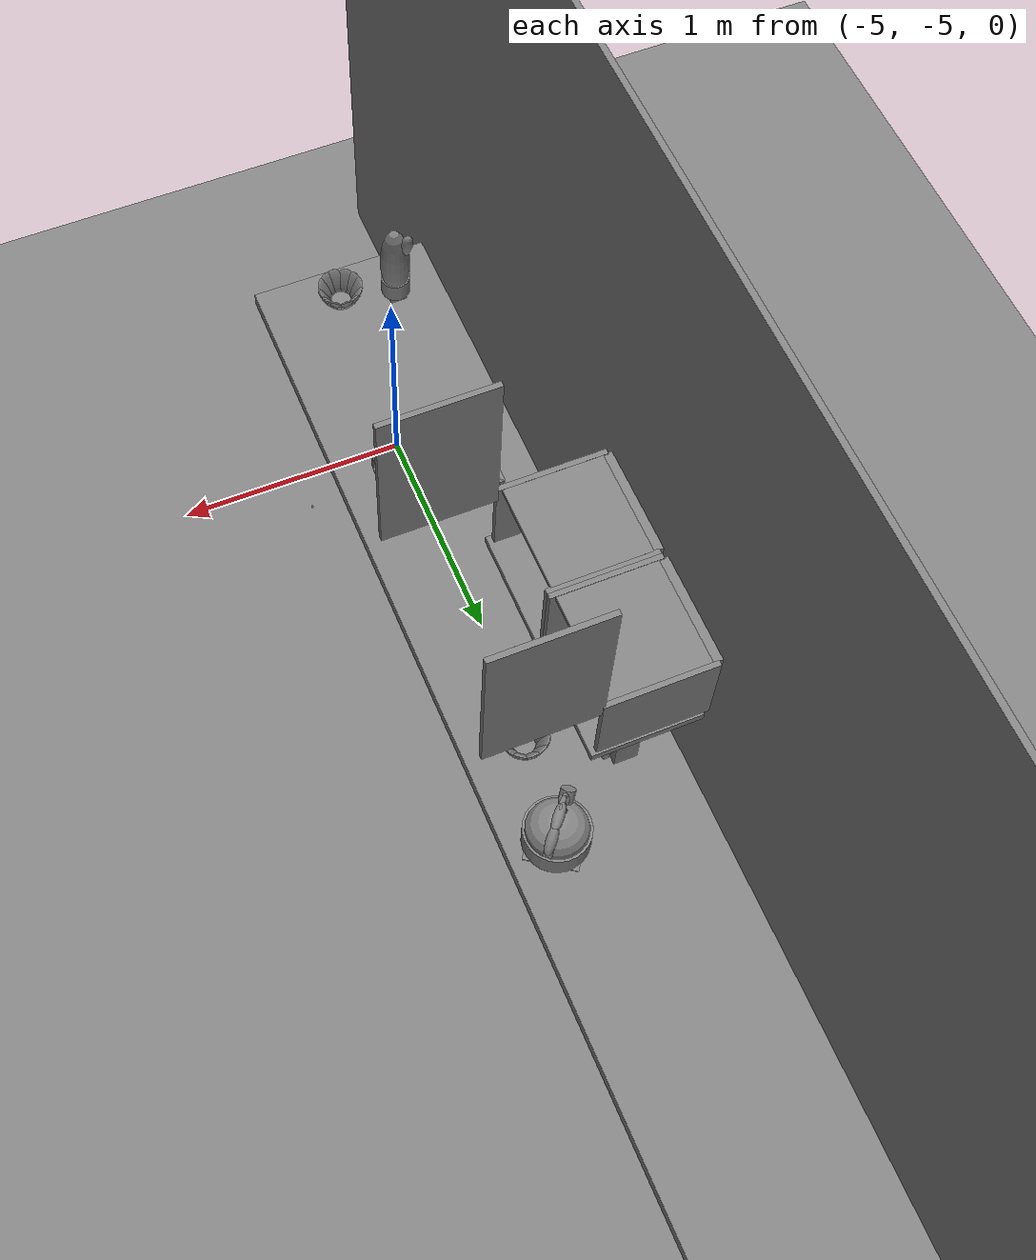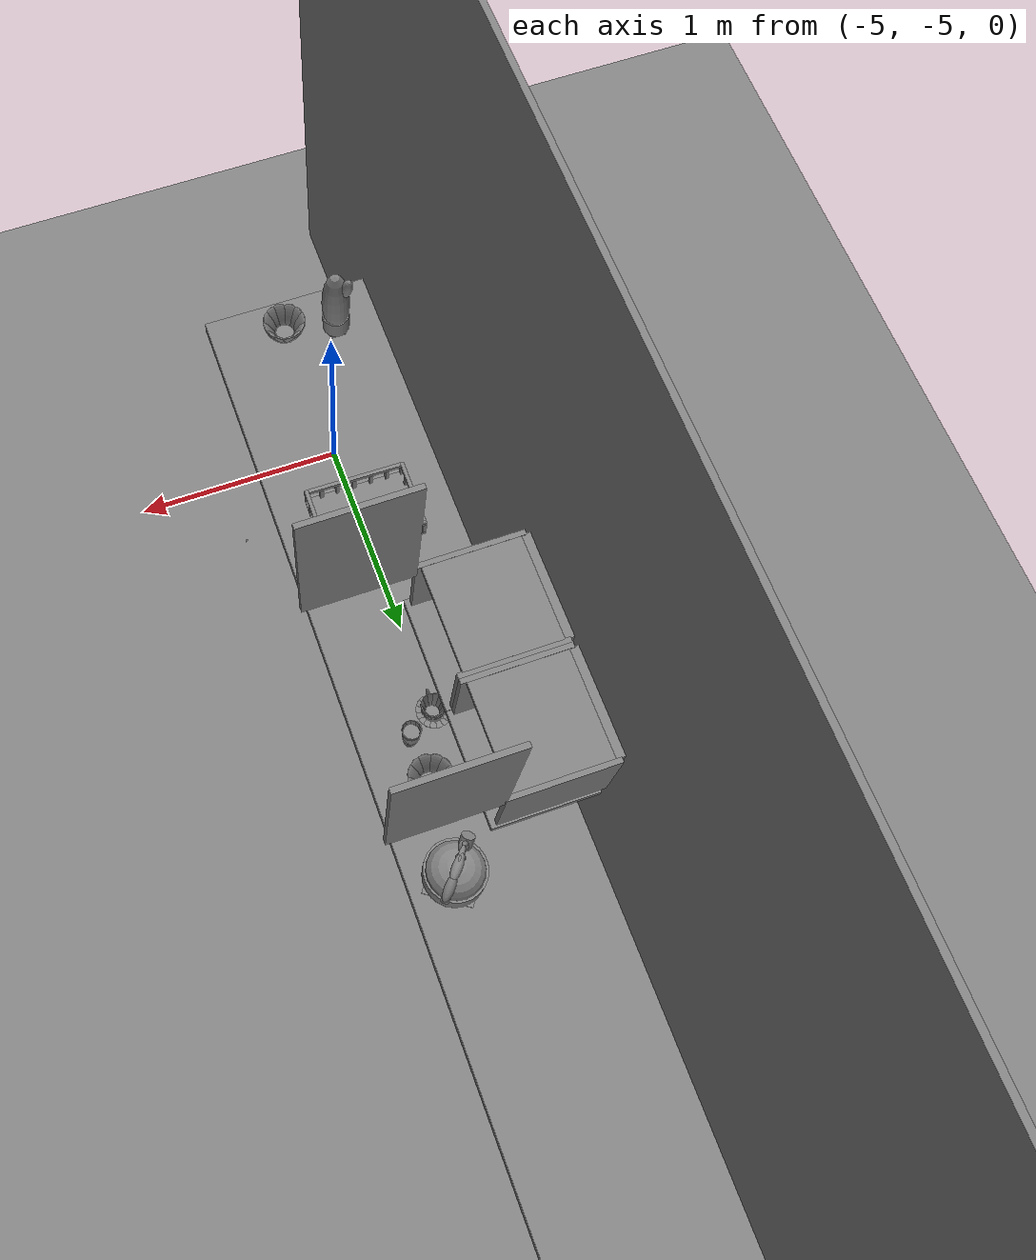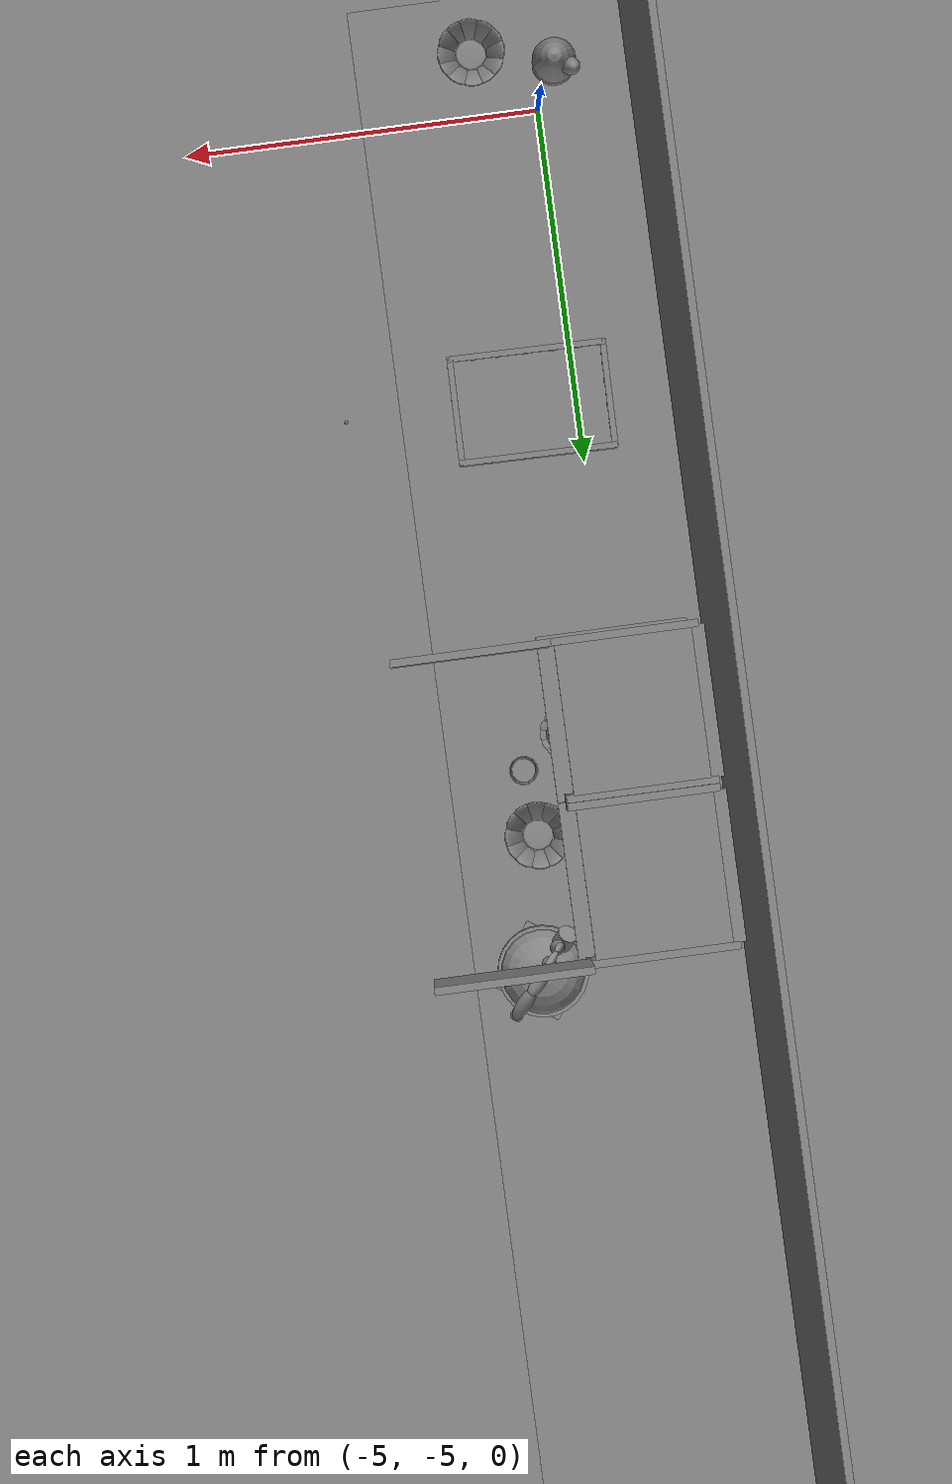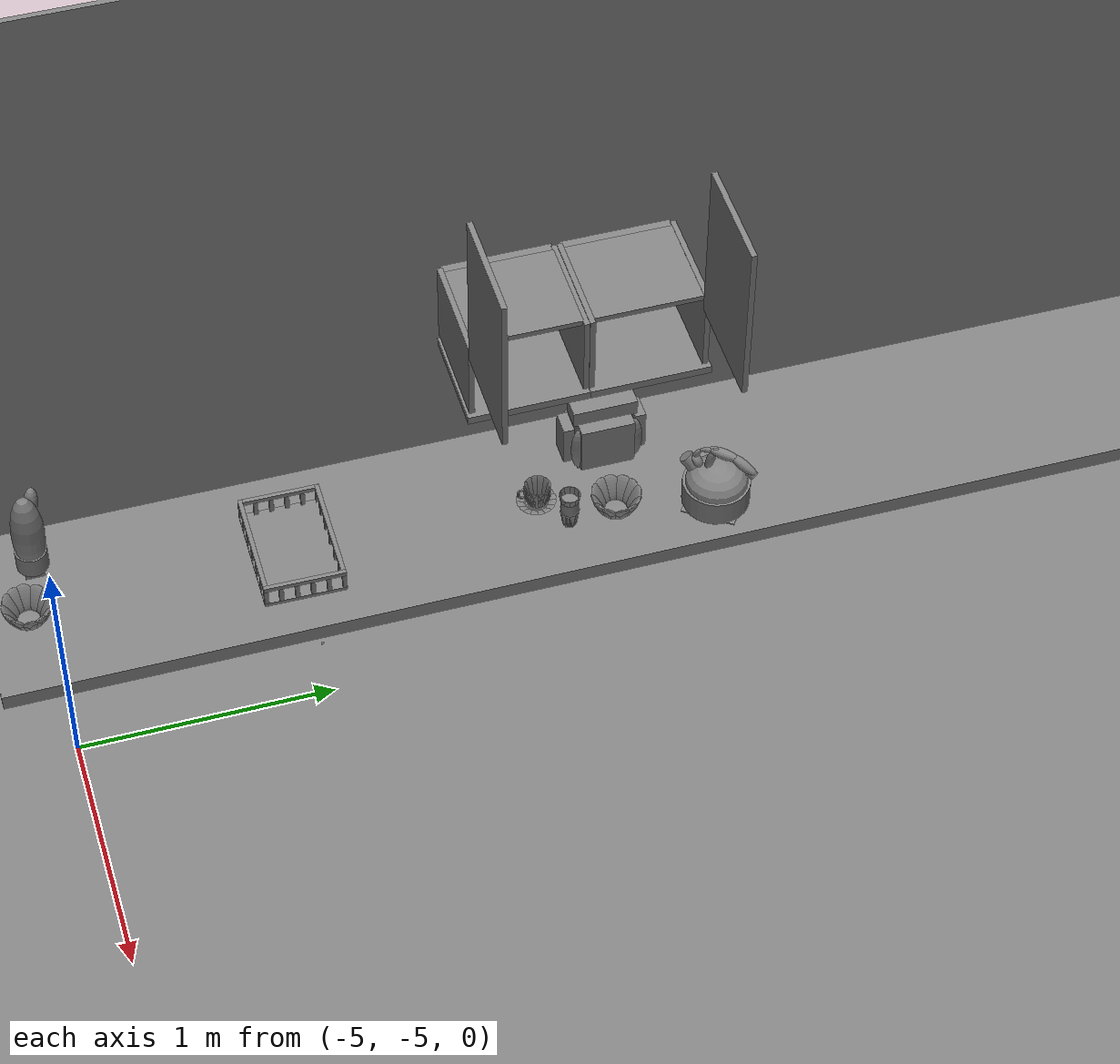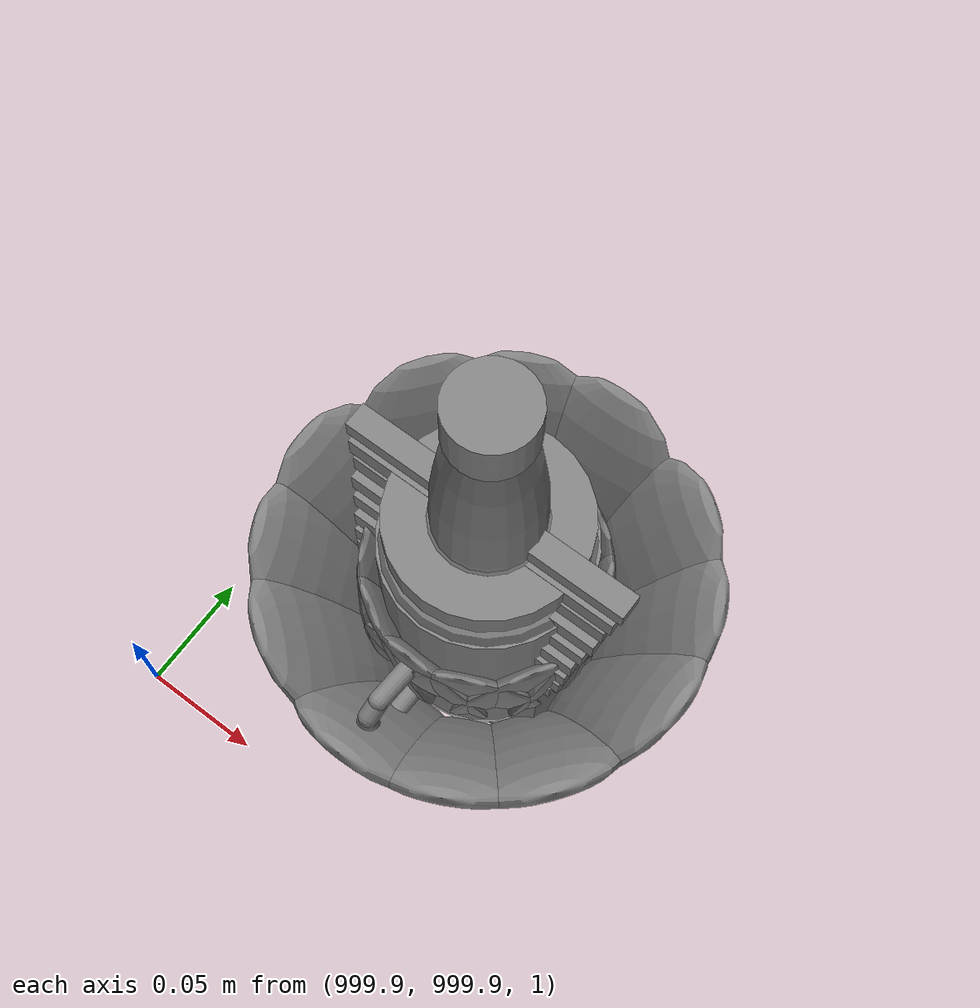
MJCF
<mujoco>
    <option gravity="0.000000000 0.000000000 -9.810000420" timestep="0.0049999999" integrator="implicitfast" density="9.8000002" viscosity="1.8000001e-05" noslip_iterations="10" iterations="100" sdf_iterations="50">
        <flag multiccd="disable"/>
    </option>
    <size memory="1000M"/>
    <compiler coordinate="local"/>
    <worldbody>
        <light cutoff="30" pos="0 1 1" dir="0 -1 -2"/>
        <light cutoff="30" pos="0 -1 1" dir="0 1 -2"/>
        <body pos="-5.046103477 -5.051773071 1.001502514" euler="0.000000000 0.000000000 0.000000000" name="Interactive Objcets_huapen">
            <geom contype="1" conaffinity="1" density="1000" type="ellipsoid" material="" rgba="0.500000000 0.500000000 0.500000000 1.000000000" solimp="0.899999976 0.949999988 0.001000000" friction="1.000000000 0.005000000 0.000100000" solref="0.020000000 1.000000000" margin="0" condim="3" group="0" pos="0.008062840 0.004346371 0.205056787" quat="1.000000000 0.000000000 0.000000000 0.000000000" size="0.059999999 0.059999999 0.180000007" name="Interactive Objcets_huapen_hua_BE8D2737_158D_4140_86EA_EF9C9B3FCC08"/>
            <geom contype="1" conaffinity="1" density="1000" type="cylinder" material="" rgba="0.500000000 0.500000000 0.500000000 1.000000000" solimp="0.899999976 0.949999988 0.001000000" friction="1.000000000 0.005000000 0.000100000" solref="0.020000000 1.000000000" margin="0" condim="3" group="0" pos="0.008062840 0.003952026 0.080107450" quat="1.000000000 0.000000000 0.000000000 0.000000000" size="0.057999998 0.039999999 1.000000000" name="Interactive Objcets_huapen_hua_7D1C60B7_56F8_41C3_A53E_3E2A55592EDE"/>
            <geom contype="1" conaffinity="1" density="1000" type="box" material="" rgba="0.500000000 0.500000000 0.500000000 1.000000000" solimp="0.899999976 0.949999988 0.001000000" friction="1.000000000 0.005000000 0.000100000" solref="0.020000000 1.000000000" margin="0" condim="3" group="0" pos="0.008062840 0.003952503 0.020566106" quat="1.000000000 0.000000000 0.000000000 0.000000000" size="0.035000000 0.035000000 0.020000000" name="Interactive Objcets_huapen_hua_D270BD7D_77D3_45DB_8ABF_2D27EE2CD94C"/>
            <geom contype="1" conaffinity="1" density="1000" type="ellipsoid" material="" rgba="0.500000000 0.500000000 0.500000000 1.000000000" solimp="0.899999976 0.949999988 0.001000000" friction="1.000000000 0.005000000 0.000100000" solref="0.020000000 1.000000000" margin="0" condim="3" group="0" pos="-0.029900074 0.033599377 0.321917295" quat="0.992658079 -0.083605267 -0.087364964 0.002748166" size="0.025000000 0.025000000 0.059999999" name="Interactive Objcets_huapen_hua_240DF250_823A_44A3_8912_ED323B249232"/>
            <freejoint name="Interactive Objcets_huapen"/>
        </body>
        <body pos="1000.000000000 1000.000000000 1.000000000" euler="0.000000000 0.000000000 0.000000000" name="openloong_gripper_2f85_fix_base_usda_salt">
            <geom contype="1" conaffinity="1" density="1000" type="box" material="" rgba="0.500000000 0.500000000 0.500000000 1.000000000" solimp="0.899999976 0.949999988 0.001000000" friction="1.000000000 0.005000000 0.000100000" solref="0.020000000 1.000000000" margin="0" condim="3" group="0" pos="0.000305176 0.000000000 0.084862232" quat="1.000000000 0.000000000 0.000000000 0.000000000" size="0.048999999 0.018999999 0.005000000" name="openloong_gripper_2f85_fix_base_usda_geom_CEC09B49_386A_4FFB_8EC7_A26F37709AC8"/>
            <geom contype="1" conaffinity="1" density="1000" type="box" material="" rgba="0.500000000 0.500000000 0.500000000 1.000000000" solimp="0.899999976 0.949999988 0.001000000" friction="1.000000000 0.005000000 0.000100000" solref="0.020000000 1.000000000" margin="0" condim="3" group="0" pos="0.000305176 0.000000000 0.104564309" quat="1.000000000 0.000000000 0.000000000 0.000000000" size="0.052000001 0.014000000 0.005000000" name="openloong_gripper_2f85_fix_base_usda_geom_8AA3C39F_B6E9_4366_A9E3_098D4E4DDB1B"/>
            <geom contype="1" conaffinity="1" density="1000" type="box" material="" rgba="0.500000000 0.500000000 0.500000000 1.000000000" solimp="0.899999976 0.949999988 0.001000000" friction="1.000000000 0.005000000 0.000100000" solref="0.020000000 1.000000000" margin="0" condim="3" group="0" pos="0.000305176 0.000000000 0.114487171" quat="1.000000000 0.000000000 0.000000000 0.000000000" size="0.054000001 0.011500000 0.005000000" name="openloong_gripper_2f85_fix_base_usda_geom_91CF71E6_C2BC_458B_8402_8A5068876770"/>
            <geom contype="1" conaffinity="1" density="1000" type="box" material="" rgba="0.500000000 0.500000000 0.500000000 1.000000000" solimp="0.899999976 0.949999988 0.001000000" friction="1.000000000 0.005000000 0.000100000" solref="0.020000000 1.000000000" margin="0" condim="3" group="0" pos="0.000305176 0.000000000 0.075103164" quat="1.000000000 0.000000000 0.000000000 0.000000000" size="0.048000000 0.020000000 0.005000000" name="openloong_gripper_2f85_fix_base_usda_geom_41E9214D_81CE_4CBB_AEF0_51195E0217EB"/>
            <geom contype="1" conaffinity="1" density="1000" type="box" material="" rgba="0.500000000 0.500000000 0.500000000 1.000000000" solimp="0.899999976 0.949999988 0.001000000" friction="1.000000000 0.005000000 0.000100000" solref="0.020000000 1.000000000" margin="0" condim="3" group="0" pos="0.000305176 0.000000000 0.134892464" quat="1.000000000 0.000000000 0.000000000 0.000000000" size="0.057000000 0.007000000 0.005000000" name="openloong_gripper_2f85_fix_base_usda_geom_50AC7866_76E3_46AC_A715_F0B174E238BC"/>
            <geom contype="1" conaffinity="1" density="1000" type="box" material="" rgba="0.500000000 0.500000000 0.500000000 1.000000000" solimp="0.899999976 0.949999988 0.001000000" friction="1.000000000 0.005000000 0.000100000" solref="0.020000000 1.000000000" margin="0" condim="3" group="0" pos="0.000305176 0.000000000 0.094920278" quat="1.000000000 0.000000000 0.000000000 0.000000000" size="0.050000001 0.017000001 0.005000000" name="openloong_gripper_2f85_fix_base_usda_geom_9AA4EF63_F457_43E0_AD23_8AA4FB5B0F25"/>
            <geom contype="1" conaffinity="1" density="1000" type="box" material="" rgba="0.500000000 0.500000000 0.500000000 1.000000000" solimp="0.899999976 0.949999988 0.001000000" friction="1.000000000 0.005000000 0.000100000" solref="0.020000000 1.000000000" margin="0" condim="3" group="0" pos="0.000305176 0.000000000 0.065204859" quat="1.000000000 0.000000000 0.000000000 0.000000000" size="0.045000002 0.021000000 0.005000000" name="openloong_gripper_2f85_fix_base_usda_geom_43B802FF_537D_424F_8300_17CAF6796126"/>
            <geom contype="1" conaffinity="1" density="1000" type="box" material="" rgba="0.500000000 0.500000000 0.500000000 1.000000000" solimp="0.899999976 0.949999988 0.001000000" friction="1.000000000 0.005000000 0.000100000" solref="0.020000000 1.000000000" margin="0" condim="3" group="0" pos="0.000305176 0.000000000 0.144135714" quat="1.000000000 0.000000000 0.000000000 0.000000000" size="0.059000000 0.005000000 0.004000000" name="openloong_gripper_2f85_fix_base_usda_geom_91FE85E0_D113_448F_8AB0_A2E6EBC0219B"/>
            <geom contype="1" conaffinity="1" density="1000" type="box" material="" rgba="0.500000000 0.500000000 0.500000000 1.000000000" solimp="0.899999976 0.949999988 0.001000000" friction="1.000000000 0.005000000 0.000100000" solref="0.020000000 1.000000000" margin="0" condim="3" group="0" pos="0.000000000 0.000000000 0.031593561" quat="1.000000000 0.000000000 0.000000000 0.000000000" size="0.041999999 0.024000000 0.029999999" name="openloong_gripper_2f85_fix_base_usda_geom_D796D5E1_323F_4847_9C35_3CACEB386F65"/>
            <geom contype="1" conaffinity="1" density="1000" type="box" material="" rgba="0.500000000 0.500000000 0.500000000 1.000000000" solimp="0.899999976 0.949999988 0.001000000" friction="1.000000000 0.005000000 0.000100000" solref="0.020000000 1.000000000" margin="0" condim="3" group="0" pos="0.000305176 0.000000000 0.124608755" quat="1.000000000 0.000000000 0.000000000 0.000000000" size="0.055000000 0.008000000 0.005000000" name="openloong_gripper_2f85_fix_base_usda_geom_5DC7595F_D0FA_4409_8FAF_E2DA7A32A6F0"/>
            <freejoint name="openloong_gripper_2f85_fix_base_usda_salt_joint"/>
            <site size="0.005000000 0.005000000 0.005000000" rgba="0.500000000 0.500000000 0.500000000 1.000000000" pos="0.000000000 0.000000000 0.000000000" quat="1.000000000 0.000000000 0.000000000 0.000000000" group="0" type="sphere" name="openloong_gripper_2f85_fix_base_usda_saltsite"/>
        </body>
        <body pos="-4.402089596 -4.028865337 1.823000431" euler="154.993652344 25.207487106 -21.516117096" mocap="true" name="spotlight3_SpotLight"/>
        <body pos="1000.000000000 1000.000000000 1.000000000" euler="0.000000000 0.000000000 0.000000000" name="openloong_gripper_2f85_fix_base_usda_bow_yellow_kps">
            <geom contype="1" conaffinity="1" density="1000" type="ellipsoid" material="" rgba="0.500000000 0.500000000 0.500000000 1.000000000" solimp="0.899999976 0.949999988 0.001000000" friction="1.000000000 0.005000000 0.000100000" solref="0.020000000 1.000000000" margin="0" condim="3" group="0" pos="-0.052185059 0.040283203 0.044118762" quat="0.919264615 -0.076883033 -0.225593656 -0.313287765" size="0.010000000 0.039999999 0.052000001" name="openloong_gripper_2f85_fix_base_usda_geom_A130DA73_D0E8_435E_8147_27270B49FDF0"/>
            <geom contype="1" conaffinity="1" density="1000" type="ellipsoid" material="" rgba="0.500000000 0.500000000 0.500000000 1.000000000" solimp="0.899999976 0.949999988 0.001000000" friction="1.000000000 0.005000000 0.000100000" solref="0.020000000 1.000000000" margin="0" condim="3" group="0" pos="-0.000061035 0.065979004 0.044118762" quat="0.687598765 -0.168314874 -0.168741167 -0.685860336" size="0.010000000 0.039999999 0.052000001" name="openloong_gripper_2f85_fix_base_usda_geom_E4AACF26_6DC7_479A_AF8B_1672207F416D"/>
            <geom contype="1" conaffinity="1" density="1000" type="box" material="" rgba="0.500000000 0.500000000 0.500000000 1.000000000" solimp="0.899999976 0.949999988 0.001000000" friction="1.000000000 0.005000000 0.000100000" solref="0.020000000 1.000000000" margin="0" condim="3" group="0" pos="0.000061035 0.000000000 -0.002001643" quat="1.000000000 0.000000000 0.000000000 0.000000000" size="0.029999999 0.029999999 0.002000000" name="openloong_gripper_2f85_fix_base_usda_geom_9B085B74_4FEB_42CF_82E1_4CCA62C2E22A"/>
            <geom contype="1" conaffinity="1" density="1000" type="ellipsoid" material="" rgba="0.500000000 0.500000000 0.500000000 1.000000000" solimp="0.899999976 0.949999988 0.001000000" friction="1.000000000 0.005000000 0.000100000" solref="0.020000000 1.000000000" margin="0" condim="3" group="0" pos="0.029418945 -0.059082031 0.044118762" quat="0.825555861 0.125530601 0.202597082 -0.511521280" size="0.010000000 0.039999999 0.052000001" name="openloong_gripper_2f85_fix_base_usda_geom_839EF29A_03DA_462F_9203_D0482F1EB94C"/>
            <geom contype="1" conaffinity="1" density="1000" type="ellipsoid" material="" rgba="0.500000000 0.500000000 0.500000000 1.000000000" solimp="0.899999976 0.949999988 0.001000000" friction="1.000000000 0.005000000 0.000100000" solref="0.020000000 1.000000000" margin="0" condim="3" group="0" pos="0.000244141 -0.065979004 0.044118762" quat="0.687598765 0.168314651 0.168741375 -0.685860336" size="0.010000000 0.039999999 0.052000001" name="openloong_gripper_2f85_fix_base_usda_geom_7C457B9C_96AB_468A_88CB_3955D1185391"/>
            <geom contype="1" conaffinity="1" density="1000" type="ellipsoid" material="" rgba="0.500000000 0.500000000 0.500000000 1.000000000" solimp="0.899999976 0.949999988 0.001000000" friction="1.000000000 0.005000000 0.000100000" solref="0.020000000 1.000000000" margin="0" condim="3" group="0" pos="0.000061035 0.000000000 0.000446677" quat="1.000000000 0.000000000 0.000000000 0.000000000" size="0.039999999 0.039999999 0.002000000" name="openloong_gripper_2f85_fix_base_usda_geom_7FFA230B_ED18_4CBC_8F60_A25067A26047"/>
            <geom contype="1" conaffinity="1" density="1000" type="ellipsoid" material="" rgba="0.500000000 0.500000000 0.500000000 1.000000000" solimp="0.899999976 0.949999988 0.001000000" friction="1.000000000 0.005000000 0.000100000" solref="0.020000000 1.000000000" margin="0" condim="3" group="0" pos="0.059082031 0.029541016 0.044118762" quat="0.223252773 -0.231952220 -0.054787423 -0.945174456" size="0.010000000 0.039999999 0.052000001" name="openloong_gripper_2f85_fix_base_usda_geom_D485E17A_A8FD_4C4A_ADD9_FB9AA0A11572"/>
            <geom contype="1" conaffinity="1" density="1000" type="ellipsoid" material="" rgba="0.500000000 0.500000000 0.500000000 1.000000000" solimp="0.899999976 0.949999988 0.001000000" friction="1.000000000 0.005000000 0.000100000" solref="0.020000000 1.000000000" margin="0" condim="3" group="0" pos="0.000061035 0.000000000 0.007335305" quat="1.000000000 0.000000000 0.000000000 0.000000000" size="0.039999999 0.039999999 0.002000000" name="openloong_gripper_2f85_fix_base_usda_geom_A2E60591_8698_450C_A0DA_4D2BD420070B"/>
            <geom contype="1" conaffinity="1" density="1000" type="ellipsoid" material="" rgba="0.500000000 0.500000000 0.500000000 1.000000000" solimp="0.899999976 0.949999988 0.001000000" friction="1.000000000 0.005000000 0.000100000" solref="0.020000000 1.000000000" margin="0" condim="3" group="0" pos="-0.029296875 0.059082031 0.044118762" quat="0.825555861 -0.125530809 -0.202596918 -0.511521280" size="0.010000000 0.039999999 0.052000001" name="openloong_gripper_2f85_fix_base_usda_geom_9EB68959_97BA_45F8_8936_7B0380044342"/>
            <geom contype="1" conaffinity="1" density="1000" type="ellipsoid" material="" rgba="0.500000000 0.500000000 0.500000000 1.000000000" solimp="0.899999976 0.949999988 0.001000000" friction="1.000000000 0.005000000 0.000100000" solref="0.020000000 1.000000000" margin="0" condim="3" group="0" pos="0.040222168 0.052368164 0.044118762" quat="0.429593176 -0.213750049 -0.105424821 -0.871002972" size="0.010000000 0.039999999 0.052000001" name="openloong_gripper_2f85_fix_base_usda_geom_A49053C4_C9A4_4C46_94CC_B45DD9522EF7"/>
            <geom contype="1" conaffinity="1" density="1000" type="ellipsoid" material="" rgba="0.500000000 0.500000000 0.500000000 1.000000000" solimp="0.899999976 0.949999988 0.001000000" friction="1.000000000 0.005000000 0.000100000" solref="0.020000000 1.000000000" margin="0" condim="3" group="0" pos="0.066040039 0.000000000 0.044118762" quat="0.971183062 -0.000000156 0.238334835 0.000000030" size="0.010000000 0.039999999 0.052000001" name="openloong_gripper_2f85_fix_base_usda_geom_4E305C30_1A0C_411D_975A_1F1DACFEFCD9"/>
            <geom contype="1" conaffinity="1" density="1000" type="ellipsoid" material="" rgba="0.500000000 0.500000000 0.500000000 1.000000000" solimp="0.899999976 0.949999988 0.001000000" friction="1.000000000 0.005000000 0.000100000" solref="0.020000000 1.000000000" margin="0" condim="3" group="0" pos="0.052307129 -0.040283203 0.044118762" quat="0.919264674 0.076882750 0.225593731 -0.313287705" size="0.010000000 0.039999999 0.052000001" name="openloong_gripper_2f85_fix_base_usda_geom_C82813D7_05A1_4DEA_AFFF_D8F70DF3A4EC"/>
            <geom contype="1" conaffinity="1" density="1000" type="ellipsoid" material="" rgba="0.500000000 0.500000000 0.500000000 1.000000000" solimp="0.899999976 0.949999988 0.001000000" friction="1.000000000 0.005000000 0.000100000" solref="0.020000000 1.000000000" margin="0" condim="3" group="0" pos="-0.065917969 0.000000000 0.044118762" quat="0.971183062 -0.000000142 -0.238334835 0.000000030" size="0.010000000 0.039999999 0.052000001" name="openloong_gripper_2f85_fix_base_usda_geom_D4059A0F_0BFB_4905_9357_4555091DEC5A"/>
            <geom contype="1" conaffinity="1" density="1000" type="ellipsoid" material="" rgba="0.500000000 0.500000000 0.500000000 1.000000000" solimp="0.899999976 0.949999988 0.001000000" friction="1.000000000 0.005000000 0.000100000" solref="0.020000000 1.000000000" margin="0" condim="3" group="0" pos="-0.058898926 -0.029541016 0.044118762" quat="0.223252758 0.231952101 0.054787733 -0.945174575" size="0.010000000 0.039999999 0.052000001" name="openloong_gripper_2f85_fix_base_usda_geom_0502CBB0_D1D1_438A_B988_9FF3584ED56E"/>
            <geom contype="1" conaffinity="1" density="1000" type="ellipsoid" material="" rgba="0.500000000 0.500000000 0.500000000 1.000000000" solimp="0.899999976 0.949999988 0.001000000" friction="1.000000000 0.005000000 0.000100000" solref="0.020000000 1.000000000" margin="0" condim="3" group="0" pos="-0.040100098 -0.052368164 0.044118762" quat="0.429593235 0.213749886 0.105425082 -0.871003032" size="0.010000000 0.039999999 0.052000001" name="openloong_gripper_2f85_fix_base_usda_geom_29634048_AE04_4509_87DF_F318A408F1BA"/>
            <freejoint name="openloong_gripper_2f85_fix_base_usda_bow_yellow_kps_joint"/>
            <site size="0.005000000 0.005000000 0.005000000" rgba="0.500000000 0.500000000 0.500000000 1.000000000" pos="0.000000000 0.000000000 0.000000000" quat="0.999961913 0.008726534 0.000000000 0.000000000" group="0" type="sphere" name="openloong_gripper_2f85_fix_base_usda_bow_yellow_kps"/>
        </body>
        <body pos="1000.000000000 1000.000000000 1.000000000" euler="0.000000000 0.000000000 0.000000000" name="openloong_gripper_2f85_fix_base_usda_bottle_red">
            <geom contype="1" conaffinity="1" density="1000" type="ellipsoid" material="" rgba="0.500000000 0.500000000 0.500000000 1.000000000" solimp="0.899999976 0.949999988 0.001000000" friction="1.000000000 0.005000000 0.000100000" solref="0.020000000 1.000000000" margin="0" condim="3" group="0" pos="0.000000000 0.000000000 0.144284487" quat="1.000000000 0.000000000 0.000000000 0.000000000" size="0.021000000 0.021000000 0.079999998" name="openloong_gripper_2f85_fix_base_usda_geom_D4003C92_2058_4FEA_B5B2_E7ED9469FEC3"/>
            <geom contype="1" conaffinity="1" density="1000" type="cylinder" material="" rgba="0.500000000 0.500000000 0.500000000 1.000000000" solimp="0.899999976 0.949999988 0.001000000" friction="1.000000000 0.005000000 0.000100000" solref="0.020000000 1.000000000" margin="0" condim="3" group="0" pos="0.000000000 0.000000000 0.220618963" quat="1.000000000 0.000000000 0.000000000 0.000000000" size="0.016000001 0.010000000 1.000000000" name="openloong_gripper_2f85_fix_base_usda_geom_E3D9241B_A816_46D0_B83D_BC11B18E99B2"/>
            <geom contype="1" conaffinity="1" density="1000" type="ellipsoid" material="" rgba="0.500000000 0.500000000 0.500000000 1.000000000" solimp="0.899999976 0.949999988 0.001000000" friction="1.000000000 0.005000000 0.000100000" solref="0.020000000 1.000000000" margin="0" condim="3" group="0" pos="0.000000000 0.000000000 0.118945479" quat="1.000000000 0.000000000 0.000000000 0.000000000" size="0.030999999 0.030999999 0.029999999" name="openloong_gripper_2f85_fix_base_usda_geom_16F9BD50_8D87_4C5A_B74F_D00A33A62C09"/>
            <geom contype="1" conaffinity="1" density="1000" type="box" material="" rgba="0.500000000 0.500000000 0.500000000 1.000000000" solimp="0.899999976 0.949999988 0.001000000" friction="1.000000000 0.005000000 0.000100000" solref="0.020000000 1.000000000" margin="0" condim="3" group="0" pos="0.000000000 0.000000000 0.002189159" quat="1.000000000 0.000000000 0.000000000 0.000000000" size="0.020000000 0.020000000 0.003000000" name="openloong_gripper_2f85_fix_base_usda_geom_0F0C6FBE_626A_4A07_86F2_9D80C7DC8736"/>
            <geom contype="1" conaffinity="1" density="1000" type="cylinder" material="" rgba="0.500000000 0.500000000 0.500000000 1.000000000" solimp="0.899999976 0.949999988 0.001000000" friction="1.000000000 0.005000000 0.000100000" solref="0.020000000 1.000000000" margin="0" condim="3" group="0" pos="0.000000000 -0.000366211 0.060884237" quat="1.000000000 0.000000000 0.000000000 0.000000000" size="0.030999999 0.057999998 1.000000000" name="openloong_gripper_2f85_fix_base_usda_geom_58C151BA_0589_4CB4_9C49_6BE53C9C5D21"/>
            <freejoint name="openloong_gripper_2f85_fix_base_usda_bottle_red_joint"/>
            <site size="0.005000000 0.005000000 0.005000000" rgba="0.500000000 0.500000000 0.500000000 1.000000000" pos="0.000000000 0.000000000 0.000000000" quat="0.999961913 0.008726535 0.000000000 0.000000000" group="0" type="sphere" name="openloong_gripper_2f85_fix_base_usda_bottle_redsite"/>
        </body>
        <body pos="-4.167570591 -3.797871351 1.745967984" euler="47.572277069 -67.611877441 -133.279708862" mocap="true" name="spotlight2_SpotLight"/>
        <body pos="-4.503353119 -3.690499783 1.793227553" euler="-144.995315552 72.137588501 143.583557129" mocap="true" name="spotlight6_SpotLight"/>
        <body pos="1000.000000000 1000.000000000 1.000000000" euler="0.000000000 0.000000000 0.000000000" name="openloong_gripper_2f85_fix_base_usda_jar_01">
            <geom contype="1" conaffinity="1" density="1000" type="box" material="" rgba="0.500000000 0.500000000 0.500000000 1.000000000" solimp="0.899999976 0.949999988 0.001000000" friction="1.000000000 0.005000000 0.000100000" solref="0.020000000 1.000000000" margin="0" condim="3" group="0" pos="0.000000000 0.000000000 0.006158113" quat="1.000000000 0.000000000 0.000000000 0.000000000" size="0.020000000 0.020000000 0.005000000" name="openloong_gripper_2f85_fix_base_usda_geom_D97EED99_0C0F_4583_A476_861B1B2C8B15"/>
            <geom contype="1" conaffinity="1" density="1000" type="cylinder" material="" rgba="0.500000000 0.500000000 0.500000000 1.000000000" solimp="0.899999976 0.949999988 0.001000000" friction="1.000000000 0.005000000 0.000100000" solref="0.020000000 1.000000000" margin="0" condim="3" group="0" pos="0.000000000 0.000000000 0.062744498" quat="1.000000000 0.000000000 0.000000000 0.000000000" size="0.041000001 0.052999999 1.000000000" name="openloong_gripper_2f85_fix_base_usda_geom_456C59CD_24A7_4B4F_A0FA_812A64D65C80"/>
            <geom contype="1" conaffinity="1" density="1000" type="ellipsoid" material="" rgba="0.500000000 0.500000000 0.500000000 1.000000000" solimp="0.899999976 0.949999988 0.001000000" friction="1.000000000 0.005000000 0.000100000" solref="0.020000000 1.000000000" margin="0" condim="3" group="0" pos="0.000000000 0.000000000 0.122252703" quat="1.000000000 0.000000000 0.000000000 0.000000000" size="0.035999998 0.035999998 0.010000000" name="openloong_gripper_2f85_fix_base_usda_geom_BC6B605B_EAC6_4013_B5E8_D3F12A8F874A"/>
            <geom contype="1" conaffinity="1" density="1000" type="cylinder" material="" rgba="0.500000000 0.500000000 0.500000000 1.000000000" solimp="0.899999976 0.949999988 0.001000000" friction="1.000000000 0.005000000 0.000100000" solref="0.020000000 1.000000000" margin="0" condim="3" group="0" pos="0.000000000 0.000000000 0.015747190" quat="1.000000000 0.000000000 0.000000000 0.000000000" size="0.035000000 0.010000000 1.000000000" name="openloong_gripper_2f85_fix_base_usda_geom_639E4DC4_A2BE_4930_A809_8C9F8CD32B71"/>
            <geom contype="1" conaffinity="1" density="1000" type="ellipsoid" material="" rgba="0.500000000 0.500000000 0.500000000 1.000000000" solimp="0.899999976 0.949999988 0.001000000" friction="1.000000000 0.005000000 0.000100000" solref="0.020000000 1.000000000" margin="0" condim="3" group="0" pos="0.000000000 0.000000000 0.115815401" quat="1.000000000 0.000000000 0.000000000 0.000000000" size="0.039999999 0.039999999 0.010000000" name="openloong_gripper_2f85_fix_base_usda_geom_ECCE1B82_175B_4BBA_AEAD_2B3266406549"/>
            <geom contype="1" conaffinity="1" density="1000" type="cylinder" material="" rgba="0.500000000 0.500000000 0.500000000 1.000000000" solimp="0.899999976 0.949999988 0.001000000" friction="1.000000000 0.005000000 0.000100000" solref="0.020000000 1.000000000" margin="0" condim="3" group="0" pos="0.000000000 0.000000000 0.133183479" quat="1.000000000 0.000000000 0.000000000 0.000000000" size="0.037999999 0.006500000 1.000000000" name="openloong_gripper_2f85_fix_base_usda_geom_2BD2B2FB_7299_4394_ABAB_30780E2D16E4"/>
            <freejoint name="openloong_gripper_2f85_fix_base_usda_jar_01_joint"/>
            <site size="0.005000000 0.005000000 0.005000000" rgba="0.500000000 0.500000000 0.500000000 1.000000000" pos="0.000000000 0.000000000 0.000000000" quat="1.000000000 0.000000000 0.000000000 0.000000000" group="0" type="sphere" name="openloong_gripper_2f85_fix_base_usda_jar_01site"/>
        </body>
        <body pos="1000.000000000 1000.000000000 1.000000000" euler="0.000000000 0.000000000 0.000000000" name="openloong_gripper_2f85_fix_base_usda_coffeecup_white_kps">
            <geom contype="1" conaffinity="1" density="1000" type="capsule" material="" rgba="0.500000000 0.500000000 0.500000000 1.000000000" solimp="0.899999976 0.949999988 0.001000000" friction="1.000000000 0.005000000 0.000100000" solref="0.020000000 1.000000000" margin="0" condim="3" group="0" pos="-0.000854492 -0.065795898 0.050029993" quat="0.343559504 -0.613204718 0.626912475 0.336047262" size="0.004000000 0.005000000 1.000000000" name="openloong_gripper_2f85_fix_base_usda_geom_930EB233_29EB_4820_8807_6984843B3F75"/>
            <geom contype="1" conaffinity="1" density="1000" type="ellipsoid" material="" rgba="0.500000000 0.500000000 0.500000000 1.000000000" solimp="0.899999976 0.949999988 0.001000000" friction="1.000000000 0.005000000 0.000100000" solref="0.020000000 1.000000000" margin="0" condim="3" group="0" pos="-0.000793457 -0.038452148 0.048040152" quat="0.711656272 0.066323131 -0.067805752 0.696095467" size="0.005000000 0.029999999 0.048999999" name="openloong_gripper_2f85_fix_base_usda_geom_101D1DD3_95DF_47B1_B2F9_7D9FBEBF5E34"/>
            <geom contype="1" conaffinity="1" density="1000" type="ellipsoid" material="" rgba="0.500000000 0.500000000 0.500000000 1.000000000" solimp="0.899999976 0.949999988 0.001000000" friction="1.000000000 0.005000000 0.000100000" solref="0.020000000 1.000000000" margin="0" condim="3" group="0" pos="0.037719727 -0.001892090 0.048040152" quat="0.995387912 0.001371633 0.094835162 -0.014391154" size="0.005000000 0.029999999 0.048999999" name="openloong_gripper_2f85_fix_base_usda_geom_A3229CFD_B4BE_4442_B91D_2F09FAA52D3E"/>
            <geom contype="1" conaffinity="1" density="1000" type="ellipsoid" material="" rgba="0.500000000 0.500000000 0.500000000 1.000000000" solimp="0.899999976 0.949999988 0.001000000" friction="1.000000000 0.005000000 0.000100000" solref="0.020000000 1.000000000" margin="0" condim="3" group="0" pos="0.033996582 0.015502930 0.048040152" quat="0.970659733 -0.021051638 0.092478797 0.220962167" size="0.005000000 0.029999999 0.048999999" name="openloong_gripper_2f85_fix_base_usda_geom_23324D5A_4947_4B9D_A45D_A2AC78825AE2"/>
            <geom contype="1" conaffinity="1" density="1000" type="box" material="" rgba="0.500000000 0.500000000 0.500000000 1.000000000" solimp="0.899999976 0.949999988 0.001000000" friction="1.000000000 0.005000000 0.000100000" solref="0.020000000 1.000000000" margin="0" condim="3" group="0" pos="0.000793457 -0.000183105 0.000156164" quat="0.714879215 0.000000000 0.000000000 0.699247897" size="0.020000000 0.020000000 0.002000000" name="openloong_gripper_2f85_fix_base_usda_geom_A8D9C7F1_2543_4238_9C6D_D3B7CEC217C1"/>
            <geom contype="1" conaffinity="1" density="1000" type="ellipsoid" material="" rgba="0.500000000 0.500000000 0.500000000 1.000000000" solimp="0.899999976 0.949999988 0.001000000" friction="1.000000000 0.005000000 0.000100000" solref="0.020000000 1.000000000" margin="0" condim="3" group="0" pos="-0.019409180 -0.033081055 0.048040152" quat="0.866879702 0.046630561 -0.082595348 0.489411235" size="0.005000000 0.029999999 0.048999999" name="openloong_gripper_2f85_fix_base_usda_geom_7B7D2307_7BF1_4BEF_AA99_9F497D102628"/>
            <geom contype="1" conaffinity="1" density="1000" type="ellipsoid" material="" rgba="0.500000000 0.500000000 0.500000000 1.000000000" solimp="0.899999976 0.949999988 0.001000000" friction="1.000000000 0.005000000 0.000100000" solref="0.020000000 1.000000000" margin="0" condim="3" group="0" pos="-0.016052246 0.033264160 0.048040152" quat="0.840792537 -0.050782297 -0.080109790 -0.532983541" size="0.005000000 0.029999999 0.048999999" name="openloong_gripper_2f85_fix_base_usda_geom_A766415A_58C4_4BAC_9817_E1FAE91E26FC"/>
            <geom contype="1" conaffinity="1" density="1000" type="capsule" material="" rgba="0.500000000 0.500000000 0.500000000 1.000000000" solimp="0.899999976 0.949999988 0.001000000" friction="1.000000000 0.005000000 0.000100000" solref="0.020000000 1.000000000" margin="0" condim="3" group="0" pos="-0.000549316 -0.053527832 0.046825886" quat="0.505496025 -0.494442940 0.505495846 0.494442940" size="0.004000000 0.005000000 1.000000000" name="openloong_gripper_2f85_fix_base_usda_geom_EC8B7C4D_A884_47FA_8643_3BA7AA485721"/>
            <geom contype="1" conaffinity="1" density="1000" type="ellipsoid" material="" rgba="0.500000000 0.500000000 0.500000000 1.000000000" solimp="0.899999976 0.949999988 0.001000000" friction="1.000000000 0.005000000 0.000100000" solref="0.020000000 1.000000000" margin="0" condim="3" group="0" pos="-0.032104492 0.018920898 0.048040152" quat="0.958129764 -0.025742561 -0.091288343 -0.270168930" size="0.005000000 0.029999999 0.048999999" name="openloong_gripper_2f85_fix_base_usda_geom_AA8D29F2_1005_4B61_9C28_68B79AF1E483"/>
            <geom contype="1" conaffinity="1" density="1000" type="ellipsoid" material="" rgba="0.500000000 0.500000000 0.500000000 1.000000000" solimp="0.899999976 0.949999988 0.001000000" friction="1.000000000 0.005000000 0.000100000" solref="0.020000000 1.000000000" margin="0" condim="3" group="0" pos="-0.037597656 0.000305176 0.048040152" quat="0.995387554 -0.001371440 -0.094839431 -0.014389008" size="0.005000000 0.029999999 0.048999999" name="openloong_gripper_2f85_fix_base_usda_geom_64B28DE9_0BDB_49DB_9646_CF876054BAF6"/>
            <geom contype="1" conaffinity="1" density="1000" type="capsule" material="" rgba="0.500000000 0.500000000 0.500000000 1.000000000" solimp="0.899999976 0.949999988 0.001000000" friction="1.000000000 0.005000000 0.000100000" solref="0.020000000 1.000000000" margin="0" condim="3" group="0" pos="-0.000366211 -0.043762207 0.044118762" quat="0.260488123 -0.651174724 0.665731549 0.254792154" size="0.004000000 0.003000000 1.000000000" name="openloong_gripper_2f85_fix_base_usda_geom_60BB0174_499C_4A65_987A_EA38D2B6033C"/>
            <geom contype="1" conaffinity="1" density="1000" type="capsule" material="" rgba="0.500000000 0.500000000 0.500000000 1.000000000" solimp="0.899999976 0.949999988 0.001000000" friction="1.000000000 0.005000000 0.000100000" solref="0.020000000 1.000000000" margin="0" condim="3" group="0" pos="-0.000915527 -0.068542480 0.082936406" quat="0.624995589 -0.339446366 0.347034454 0.611329615" size="0.004000000 0.004000000 1.000000000" name="openloong_gripper_2f85_fix_base_usda_geom_52F7D2BE_907A_482C_A864_5C95F8DC7702"/>
            <geom contype="1" conaffinity="1" density="1000" type="ellipsoid" material="" rgba="0.500000000 0.500000000 0.500000000 1.000000000" solimp="0.899999976 0.949999988 0.001000000" friction="1.000000000 0.005000000 0.000100000" solref="0.020000000 1.000000000" margin="0" condim="3" group="0" pos="0.016113281 -0.034851074 0.048040152" quat="0.840793252 0.050779939 0.080106191 -0.532983422" size="0.005000000 0.029999999 0.048999999" name="openloong_gripper_2f85_fix_base_usda_geom_8D7EEE4F_5380_4783_AFE2_BEC887FEB49E"/>
            <geom contype="1" conaffinity="1" density="1000" type="ellipsoid" material="" rgba="0.500000000 0.500000000 0.500000000 1.000000000" solimp="0.899999976 0.949999988 0.001000000" friction="1.000000000 0.005000000 0.000100000" solref="0.020000000 1.000000000" margin="0" condim="3" group="0" pos="0.000854492 0.036865234 0.048040152" quat="0.711656570 -0.066320375 0.067802906 0.696095705" size="0.005000000 0.029999999 0.048999999" name="openloong_gripper_2f85_fix_base_usda_geom_AFBDC172_BFC9_4263_A35A_D415545A345B"/>
            <geom contype="1" conaffinity="1" density="1000" type="ellipsoid" material="" rgba="0.500000000 0.500000000 0.500000000 1.000000000" solimp="0.899999976 0.949999988 0.001000000" friction="1.000000000 0.005000000 0.000100000" solref="0.020000000 1.000000000" margin="0" condim="3" group="0" pos="-0.033935547 -0.017089844 0.048040152" quat="0.970659137 0.021052625 -0.092483103 0.220962465" size="0.005000000 0.029999999 0.048999999" name="openloong_gripper_2f85_fix_base_usda_geom_40C413E0_9F56_4AA9_AE26_035F12287886"/>
            <geom contype="1" conaffinity="1" density="1000" type="ellipsoid" material="" rgba="0.500000000 0.500000000 0.500000000 1.000000000" solimp="0.899999976 0.949999988 0.001000000" friction="1.000000000 0.005000000 0.000100000" solref="0.020000000 1.000000000" margin="0" condim="3" group="0" pos="0.019531250 0.031494141 0.048040152" quat="0.866880119 -0.046628602 0.082591817 0.489411235" size="0.005000000 0.029999999 0.048999999" name="openloong_gripper_2f85_fix_base_usda_geom_B27027E1_137F_4F63_80DA_C299F7ECA750"/>
            <geom contype="1" conaffinity="1" density="1000" type="ellipsoid" material="" rgba="0.500000000 0.500000000 0.500000000 1.000000000" solimp="0.899999976 0.949999988 0.001000000" friction="1.000000000 0.005000000 0.000100000" solref="0.020000000 1.000000000" margin="0" condim="3" group="0" pos="0.032165527 -0.020507812 0.048040152" quat="0.958128154 0.025740955 0.091285400 -0.270175666" size="0.005000000 0.029999999 0.048999999" name="openloong_gripper_2f85_fix_base_usda_geom_1DE95DF3_5706_4AF6_A00E_7D670E07F82A"/>
            <geom contype="1" conaffinity="1" density="1000" type="capsule" material="" rgba="0.500000000 0.500000000 0.500000000 1.000000000" solimp="0.899999976 0.949999988 0.001000000" friction="1.000000000 0.005000000 0.000100000" solref="0.020000000 1.000000000" margin="0" condim="3" group="0" pos="-0.000610352 -0.056823730 0.083572865" quat="0.452654332 -0.541215360 0.553313971 0.442756712" size="0.004000000 0.009000000 1.000000000" name="openloong_gripper_2f85_fix_base_usda_geom_1D43CEB5_483B_4EA7_B9F1_BBA127ECF37C"/>
            <geom contype="1" conaffinity="1" density="1000" type="ellipsoid" material="" rgba="0.500000000 0.500000000 0.500000000 1.000000000" solimp="0.899999976 0.949999988 0.001000000" friction="1.000000000 0.005000000 0.000100000" solref="0.020000000 1.000000000" margin="0" condim="3" group="0" pos="0.000061035 -0.000183105 0.001848221" quat="0.714879215 0.000000000 0.000000000 0.699247897" size="0.029999999 0.029999999 0.001000000" name="openloong_gripper_2f85_fix_base_usda_geom_63C17903_BC56_4505_A5C5_DF52F22575F4"/>
            <geom contype="1" conaffinity="1" density="1000" type="capsule" material="" rgba="0.500000000 0.500000000 0.500000000 1.000000000" solimp="0.899999976 0.949999988 0.001000000" friction="1.000000000 0.005000000 0.000100000" solref="0.020000000 1.000000000" margin="0" condim="3" group="0" pos="-0.000976562 -0.071838379 0.066101432" quat="0.031849027 -0.698553741 0.714169443 0.031152546" size="0.004000000 0.012000000 1.000000000" name="openloong_gripper_2f85_fix_base_usda_geom_25EA01E6_C28D_4715_AAB5_4E2D4E4E45A2"/>
            <freejoint name="openloong_gripper_2f85_fix_base_usda_coffeecup_white_kps_joint"/>
            <site size="0.005000000 0.005000000 0.005000000" rgba="0.500000000 0.500000000 0.500000000 1.000000000" pos="0.000000000 0.000000000 0.000000000" quat="0.999961913 0.008726534 0.000000000 0.000000000" group="0" type="sphere" name="openloong_gripper_2f85_fix_base_usda_coffeecup_white_kps"/>
        </body>
        <body pos="0.000000000 0.000000000 0.000000000" euler="0.000000000 0.000000000 0.000000000" name="Static Objcets_Static Objcets">
            <geom contype="1" conaffinity="1" density="1000" type="box" material="" rgba="0.500000000 0.500000000 0.500000000 1.000000000" solimp="0.899999976 0.949999988 0.001000000" friction="1.000000000 0.005000000 0.000100000" solref="0.020000000 1.000000000" margin="0" condim="3" group="0" pos="-4.999745846 -3.497932911 1.764780521" quat="0.707107067 0.707106471 0.000000000 0.000000000" size="0.200000003 0.159999996 0.010000000" name="Static Objcets_geom_07289AF5_16D1_4CE5_B5D0_212A0505CE31"/>
            <geom contype="1" conaffinity="1" density="1000" type="box" material="" rgba="0.500000000 0.500000000 0.500000000 1.000000000" solimp="0.899999976 0.949999988 0.001000000" friction="1.000000000 0.005000000 0.000100000" solref="0.020000000 1.000000000" margin="0" condim="3" group="0" pos="-4.979488373 -3.297635794 1.591412544" quat="0.707106829 0.707106709 0.000000000 0.000000000" size="0.200000003 0.015000000 0.219999999" name="Static Objcets_geom_C88E1135_FCF0_41DC_9419_9260ED1E2180"/>
            <geom contype="1" conaffinity="1" density="1000" type="box" material="" rgba="0.500000000 0.500000000 0.500000000 1.000000000" solimp="0.899999976 0.949999988 0.001000000" friction="1.000000000 0.005000000 0.000100000" solref="0.020000000 1.000000000" margin="0" condim="3" group="0" pos="-4.999745846 -3.087441683 1.763863802" quat="0.707107067 0.707106471 0.000000000 0.000000000" size="0.200000003 0.159999996 0.010000000" name="Static Objcets_geom_2BE66958_E0A9_4C5D_A58D_4D0DDA4BB370"/>
            <geom contype="1" conaffinity="1" density="1000" type="box" material="" rgba="0.500000000 0.500000000 0.500000000 1.000000000" solimp="0.899999976 0.949999988 0.001000000" friction="1.000000000 0.005000000 0.000100000" solref="0.020000000 1.000000000" margin="0" condim="3" group="0" pos="-5.189302921 -3.293644905 1.760152459" quat="0.707107067 0.707106471 0.000000000 0.000000000" size="0.025000000 0.159999996 0.200000003" name="Static Objcets_geom_4024F7FF_8EE5_480D_82D3_F0B231D26438"/>
            <geom contype="1" conaffinity="1" density="1000" type="box" material="" rgba="0.500000000 0.500000000 0.500000000 1.000000000" solimp="0.899999976 0.949999988 0.001000000" friction="1.000000000 0.005000000 0.000100000" solref="0.020000000 1.000000000" margin="0" condim="3" group="0" pos="-5.000125408 -3.294431210 1.913951039" quat="0.707107067 0.707106471 0.000000000 0.000000000" size="0.180000007 0.010000000 0.200000003" name="Static Objcets_geom_56C8F120_2894_4C7E_8DF1_E91F0B64CD28"/>
            <geom contype="1" conaffinity="1" density="1000" type="box" material="" rgba="0.500000000 0.500000000 0.500000000 1.000000000" solimp="0.899999976 0.949999988 0.001000000" friction="1.000000000 0.005000000 0.000100000" solref="0.020000000 1.000000000" margin="0" condim="3" group="0" pos="-5.000125408 -2.861802340 1.913950682" quat="0.707107067 0.707106471 0.000000000 0.000000000" size="0.180000007 0.010000000 0.200000003" name="Static Objcets_geom_21677717_A833_4418_9A6A_7F3EE03A7B2E"/>
            <geom contype="1" conaffinity="1" density="1000" type="box" material="" rgba="0.500000000 0.500000000 0.500000000 1.000000000" solimp="0.899999976 0.949999988 0.001000000" friction="1.000000000 0.005000000 0.000100000" solref="0.020000000 1.000000000" margin="0" condim="3" group="0" pos="-4.979488373 -2.855390549 1.591412187" quat="0.707106709 0.707106769 0.000000000 0.000000000" size="0.200000003 0.015000000 0.219999999" name="Static Objcets_geom_13A331FB_688F_489E_AB65_B32907D85E69"/>
            <geom contype="1" conaffinity="1" density="1000" type="box" material="" rgba="0.500000000 0.500000000 0.500000000 1.000000000" solimp="0.899999976 0.949999988 0.001000000" friction="1.000000000 0.005000000 0.000100000" solref="0.020000000 1.000000000" margin="0" condim="3" group="0" pos="-4.999745846 -3.066934109 1.765979409" quat="0.707107067 0.707106471 0.000000000 0.000000000" size="0.200000003 0.159999996 0.010000000" name="Static Objcets_geom_22D1DB55_2861_4AD9_827C_F1980C46B6DB"/>
            <geom contype="1" conaffinity="1" density="1000" type="box" material="" rgba="0.500000000 0.500000000 0.500000000 1.000000000" solimp="0.899999976 0.949999988 0.001000000" friction="1.000000000 0.005000000 0.000100000" solref="0.020000000 1.000000000" margin="0" condim="3" group="0" pos="-4.999745846 -2.653569937 1.764779806" quat="0.707107067 0.707106471 0.000000000 0.000000000" size="0.200000003 0.159999996 0.010000000" name="Static Objcets_geom_B0250CE3_E821_4A60_A81B_14006C3B56D4"/>
            <geom contype="1" conaffinity="1" density="1000" type="box" material="" rgba="0.500000000 0.500000000 0.500000000 1.000000000" solimp="0.899999976 0.949999988 0.001000000" friction="1.000000000 0.005000000 0.000100000" solref="0.020000000 1.000000000" margin="0" condim="3" group="0" pos="-5.189302921 -2.861564636 1.760152102" quat="0.707107067 0.707106471 0.000000000 0.000000000" size="0.025000000 0.159999996 0.200000003" name="Static Objcets_geom_3B04EC7C_9DC8_4971_858A_74F63D7ADB87"/>
            <geom contype="1" conaffinity="1" density="1000" type="box" material="" rgba="0.500000000 0.500000000 0.500000000 1.000000000" solimp="0.899999976 0.949999988 0.001000000" friction="1.000000000 0.005000000 0.000100000" solref="0.020000000 1.000000000" margin="0" condim="3" group="0" pos="-4.873187065 -2.461376429 0.977675021" quat="0.707107067 0.707106471 0.000000000 0.000000000" size="0.370000005 0.029999999 2.799999952" name="Static Objcets_geom_A57AB39A_6983_4255_9FC6_0DEB9CF8BEA3"/>
            <geom contype="1" conaffinity="1" density="1000" type="box" material="" rgba="0.500000000 0.500000000 0.500000000 1.000000000" solimp="0.899999976 0.949999988 0.001000000" friction="1.000000000 0.005000000 0.000100000" solref="0.020000000 1.000000000" margin="0" condim="3" group="0" pos="-5.244853973 -2.375543594 1.820221663" quat="0.707107008 0.707106531 0.000000000 0.000000000" size="0.010000000 1.500000000 3.700000048" name="Static Objcets_geom_EF45C37E_5106_46FF_B146_E8F402864199"/>
            <geom contype="1" conaffinity="1" density="1000" type="box" material="" rgba="0.500000000 0.500000000 0.500000000 1.000000000" solimp="0.899999976 0.949999988 0.001000000" friction="1.000000000 0.005000000 0.000100000" solref="0.020000000 1.000000000" margin="0" condim="3" group="0" pos="-0.720102787 0.222944975 -1.102830648" quat="0.000000954 1.000000000 0.000000000 0.000000000" size="8.000000000 8.000000000 0.010000000" name="Static Objcets_geom_9F05223F_F158_4DBA_87F6_4CC4B2937068"/>
        </body>
        <body pos="-4.685121059 -2.618872881 1.139834642" euler="-89.999885559 -75.046211243 -179.999633789" name="Interactive Objcets_shuihu">
            <geom contype="1" conaffinity="1" density="1000" type="ellipsoid" material="" rgba="0.500000000 0.500000000 0.500000000 1.000000000" solimp="0.899999976 0.949999988 0.001000000" friction="1.000000000 0.005000000 0.000100000" solref="0.020000000 1.000000000" margin="0" condim="3" group="0" pos="0.031587839 0.066336274 0.011863232" quat="0.813834965 -0.098448642 0.568551302 0.068776846" size="0.020000000 0.059999999 0.015000000" name="Interactive Objcets_geom_CA51FB0C_641A_49DB_B7C8_6CB7B0768AC0"/>
            <geom contype="1" conaffinity="1" density="1000" type="cylinder" material="" rgba="0.500000000 0.500000000 0.500000000 1.000000000" solimp="0.899999976 0.949999988 0.001000000" friction="1.000000000 0.005000000 0.000100000" solref="0.020000000 1.000000000" margin="0" condim="3" group="0" pos="0.097564876 0.019223809 0.042538166" quat="0.757945418 -0.330064029 0.507527351 0.242883876" size="0.027000001 0.032499999 1.000000000" name="Interactive Objcets_geom_481E7538_42F5_4288_8375_637886F294FA"/>
            <geom contype="1" conaffinity="1" density="1000" type="ellipsoid" material="" rgba="0.500000000 0.500000000 0.500000000 1.000000000" solimp="0.899999976 0.949999988 0.001000000" friction="1.000000000 0.005000000 0.000100000" solref="0.020000000 1.000000000" margin="0" condim="3" group="0" pos="0.079775751 0.074323297 0.032407284" quat="0.807211578 -0.212389767 0.536951303 0.122406662" size="0.011000000 0.029999999 0.010000000" name="Interactive Objcets_geom_C59BB76A_515B_454D_A25D_3977CE51CD74"/>
            <geom contype="1" conaffinity="1" density="1000" type="cylinder" material="" rgba="0.500000000 0.500000000 0.500000000 1.000000000" solimp="0.899999976 0.949999988 0.001000000" friction="1.000000000 0.005000000 0.000100000" solref="0.020000000 1.000000000" margin="0" condim="3" group="0" pos="0.006719470 -0.083229184 -0.000185013" quat="0.579664290 -0.579662681 0.404957741 0.404956520" size="0.123000003 0.050000001 1.000000000" name="Interactive Objcets_geom_65D6114A_9CA2_4D5B_9F40_4EDCD8F4E549"/>
            <geom contype="1" conaffinity="1" density="1000" type="cylinder" material="" rgba="0.500000000 0.500000000 0.500000000 1.000000000" solimp="0.899999976 0.949999988 0.001000000" friction="1.000000000 0.005000000 0.000100000" solref="0.020000000 1.000000000" margin="0" condim="3" group="0" pos="-0.109747589 0.061178923 -0.054180622" quat="0.791120291 -0.252390862 0.522301614 0.193980843" size="0.017000001 0.015000000 1.000000000" name="Interactive Objcets_geom_96F38C9B_58F0_4D39_93B0_2BE4417F772D"/>
            <geom contype="1" conaffinity="1" density="1000" type="ellipsoid" material="" rgba="0.500000000 0.500000000 0.500000000 1.000000000" solimp="0.899999976 0.949999988 0.001000000" friction="1.000000000 0.005000000 0.000100000" solref="0.020000000 1.000000000" margin="0" condim="3" group="0" pos="-0.012925148 0.115441918 -0.008463383" quat="0.573223114 -0.617213011 0.363985062 0.397464871" size="0.020000000 0.059999999 0.017999999" name="Interactive Objcets_geom_8E2E4AA8_E73D_4E76_9989_E1AC9C54B29F"/>
            <geom contype="1" conaffinity="1" density="1000" type="ellipsoid" material="" rgba="0.500000000 0.500000000 0.500000000 1.000000000" solimp="0.899999976 0.949999988 0.001000000" friction="1.000000000 0.005000000 0.000100000" solref="0.020000000 1.000000000" margin="0" condim="3" group="0" pos="0.076839805 0.041928887 0.028444767" quat="0.777403057 0.260122687 0.543099582 -0.181723833" size="0.020000000 0.029999999 0.015000000" name="Interactive Objcets_geom_DDFC4234_259E_46E1_AB4F_D574CC0BDB80"/>
            <geom contype="1" conaffinity="1" density="1000" type="ellipsoid" material="" rgba="0.500000000 0.500000000 0.500000000 1.000000000" solimp="0.899999976 0.949999988 0.001000000" friction="1.000000000 0.005000000 0.000100000" solref="0.020000000 1.000000000" margin="0" condim="3" group="0" pos="-0.081469536 0.090929627 -0.040654182" quat="0.423473954 -0.728255510 0.250199795 0.477193654" size="0.020000000 0.059999999 0.017999999" name="Interactive Objcets_geom_BDF2E42D_FF01_4762_B22A_297A9178F9B5"/>
            <geom contype="1" conaffinity="1" density="1000" type="ellipsoid" material="" rgba="0.500000000 0.500000000 0.500000000 1.000000000" solimp="0.899999976 0.949999988 0.001000000" friction="1.000000000 0.005000000 0.000100000" solref="0.020000000 1.000000000" margin="0" condim="3" group="0" pos="0.036164403 0.116219044 0.012343884" quat="0.691036344 -0.468154669 0.465933800 0.293608427" size="0.011000000 0.039999999 0.010000000" name="Interactive Objcets_geom_761CA34F_E368_4B69_BE3D_BABCE66DD50F"/>
            <geom contype="1" conaffinity="1" density="1000" type="box" material="" rgba="0.500000000 0.500000000 0.500000000 1.000000000" solimp="0.899999976 0.949999988 0.001000000" friction="1.000000000 0.005000000 0.000100000" solref="0.020000000 1.000000000" margin="0" condim="3" group="0" pos="0.006720424 -0.132364750 -0.000183582" quat="0.579664230 -0.579662681 0.404957652 0.404956520" size="0.100000001 0.100000001 0.005000000" name="Interactive Objcets_geom_D706677D_C860_414B_9726_3B2B49932DF9"/>
            <geom contype="1" conaffinity="1" density="1000" type="ellipsoid" material="" rgba="0.500000000 0.500000000 0.500000000 1.000000000" solimp="0.899999976 0.949999988 0.001000000" friction="1.000000000 0.005000000 0.000100000" solref="0.020000000 1.000000000" margin="0" condim="3" group="0" pos="0.006307602 -0.038442492 -0.000561237" quat="0.579664290 -0.579662681 0.404957741 0.404956520" size="0.115000002 0.115000002 0.079999998" name="Interactive Objcets_geom_A0104DBE_2B5C_4762_8295_86A528AC4EB4"/>
            <freejoint name="Interactive Objcets_shuihu"/>
        </body>
        <body pos="-4.821335316 -5.105734825 1.007418752" euler="0.000000000 0.000000000 89.999946594" name="Interactive Objcets_bow_04">
            <geom contype="1" conaffinity="1" density="1000" type="ellipsoid" material="" rgba="0.500000000 0.500000000 0.500000000 1.000000000" solimp="0.899999976 0.949999988 0.001000000" friction="1.000000000 0.005000000 0.000100000" solref="0.020000000 1.000000000" margin="0" condim="3" group="0" pos="-0.000090122 0.065967083 0.044118762" quat="0.687598825 -0.168314755 -0.168741047 -0.685860395" size="0.010000000 0.039999999 0.052000001" name="Interactive Objcets_geom_6D298688_2DAD_4F2F_ACB5_3DC38D7C7360"/>
            <geom contype="1" conaffinity="1" density="1000" type="ellipsoid" material="" rgba="0.500000000 0.500000000 0.500000000 1.000000000" solimp="0.899999976 0.949999988 0.001000000" friction="1.000000000 0.005000000 0.000100000" solref="0.020000000 1.000000000" margin="0" condim="3" group="0" pos="-0.040080309 -0.052354813 0.044118762" quat="0.429593146 0.213749856 0.105425127 -0.871003032" size="0.010000000 0.039999999 0.052000001" name="Interactive Objcets_geom_1F9BDD04_BAA7_4E8B_9772_86FEB6736CBE"/>
            <geom contype="1" conaffinity="1" density="1000" type="ellipsoid" material="" rgba="0.500000000 0.500000000 0.500000000 1.000000000" solimp="0.899999976 0.949999988 0.001000000" friction="1.000000000 0.005000000 0.000100000" solref="0.020000000 1.000000000" margin="0" condim="3" group="0" pos="-0.029293537 0.059069157 0.044118762" quat="0.825556040 -0.125530839 -0.202596709 -0.511521041" size="0.010000000 0.039999999 0.052000001" name="Interactive Objcets_geom_08EDDCB4_8838_4A44_8402_AC163B450D39"/>
            <geom contype="1" conaffinity="1" density="1000" type="ellipsoid" material="" rgba="0.500000000 0.500000000 0.500000000 1.000000000" solimp="0.899999976 0.949999988 0.001000000" friction="1.000000000 0.005000000 0.000100000" solref="0.020000000 1.000000000" margin="0" condim="3" group="0" pos="-0.065898657 -0.000007629 0.044118762" quat="0.971183062 -0.000000142 -0.238334835 0.000000030" size="0.010000000 0.039999999 0.052000001" name="Interactive Objcets_geom_FE886FCD_DFC3_4BCA_890A_3D1CC4B63626"/>
            <geom contype="1" conaffinity="1" density="1000" type="ellipsoid" material="" rgba="0.500000000 0.500000000 0.500000000 1.000000000" solimp="0.899999976 0.949999988 0.001000000" friction="1.000000000 0.005000000 0.000100000" solref="0.020000000 1.000000000" margin="0" condim="3" group="0" pos="0.000082970 0.000000000 0.000446677" quat="1.000000000 0.000000000 0.000000000 0.000000000" size="0.039999999 0.039999999 0.002000000" name="Interactive Objcets_geom_DCD04CAF_AF9A_45BC_B90A_8BA44D9687C6"/>
            <geom contype="1" conaffinity="1" density="1000" type="ellipsoid" material="" rgba="0.500000000 0.500000000 0.500000000 1.000000000" solimp="0.899999976 0.949999988 0.001000000" friction="1.000000000 0.005000000 0.000100000" solref="0.020000000 1.000000000" margin="0" condim="3" group="0" pos="0.000243664 -0.065983295 0.044118762" quat="0.687598884 0.168314576 0.168741226 -0.685860336" size="0.010000000 0.039999999 0.052000001" name="Interactive Objcets_geom_DF1CB753_2AE5_4AE8_8233_CD7E9BA7AC37"/>
            <geom contype="1" conaffinity="1" density="1000" type="ellipsoid" material="" rgba="0.500000000 0.500000000 0.500000000 1.000000000" solimp="0.899999976 0.949999988 0.001000000" friction="1.000000000 0.005000000 0.000100000" solref="0.020000000 1.000000000" margin="0" condim="3" group="0" pos="0.000082970 0.000000000 0.003118873" quat="1.000000000 0.000000000 0.000000000 0.000000000" size="0.039999999 0.039999999 0.002000000" name="Interactive Objcets_geom_06BAAF52_B0FB_4D98_B3D4_922A4E5738CE"/>
            <geom contype="1" conaffinity="1" density="1000" type="ellipsoid" material="" rgba="0.500000000 0.500000000 0.500000000 1.000000000" solimp="0.899999976 0.949999988 0.001000000" friction="1.000000000 0.005000000 0.000100000" solref="0.020000000 1.000000000" margin="0" condim="3" group="0" pos="0.040234327 0.052339077 0.044118762" quat="0.429593533 -0.213750005 -0.105424747 -0.871002972" size="0.010000000 0.039999999 0.052000001" name="Interactive Objcets_geom_11809CBF_367B_4636_A009_194234BCBF17"/>
            <geom contype="1" conaffinity="1" density="1000" type="ellipsoid" material="" rgba="0.500000000 0.500000000 0.500000000 1.000000000" solimp="0.899999976 0.949999988 0.001000000" friction="1.000000000 0.005000000 0.000100000" solref="0.020000000 1.000000000" margin="0" condim="3" group="0" pos="0.066051960 -0.000007629 0.044118762" quat="0.971183062 -0.000000156 0.238334835 0.000000030" size="0.010000000 0.039999999 0.052000001" name="Interactive Objcets_geom_24D7B432_C0FA_4C20_8672_5FAB7610C0E2"/>
            <geom contype="1" conaffinity="1" density="1000" type="ellipsoid" material="" rgba="0.500000000 0.500000000 0.500000000 1.000000000" solimp="0.899999976 0.949999988 0.001000000" friction="1.000000000 0.005000000 0.000100000" solref="0.020000000 1.000000000" margin="0" condim="3" group="0" pos="-0.058925867 -0.029528618 0.044118762" quat="0.223252863 0.231952116 0.054787725 -0.945174456" size="0.010000000 0.039999999 0.052000001" name="Interactive Objcets_geom_4C097438_6BFA_4ED6_B2D7_6CB06E310E3C"/>
            <geom contype="1" conaffinity="1" density="1000" type="ellipsoid" material="" rgba="0.500000000 0.500000000 0.500000000 1.000000000" solimp="0.899999976 0.949999988 0.001000000" friction="1.000000000 0.005000000 0.000100000" solref="0.020000000 1.000000000" margin="0" condim="3" group="0" pos="0.029448032 -0.059085369 0.044118762" quat="0.825555801 0.125530601 0.202597082 -0.511521280" size="0.010000000 0.039999999 0.052000001" name="Interactive Objcets_geom_1E7E981F_2021_449A_B3AA_C28487898D69"/>
            <geom contype="1" conaffinity="1" density="1000" type="ellipsoid" material="" rgba="0.500000000 0.500000000 0.500000000 1.000000000" solimp="0.899999976 0.949999988 0.001000000" friction="1.000000000 0.005000000 0.000100000" solref="0.020000000 1.000000000" margin="0" condim="3" group="0" pos="0.059080124 0.029511929 0.044118762" quat="0.223252952 -0.231952190 -0.054787360 -0.945174456" size="0.010000000 0.039999999 0.052000001" name="Interactive Objcets_geom_6B0A04AA_5628_441A_A22F_85EAD4C32F1B"/>
            <geom contype="1" conaffinity="1" density="1000" type="ellipsoid" material="" rgba="0.500000000 0.500000000 0.500000000 1.000000000" solimp="0.899999976 0.949999988 0.001000000" friction="1.000000000 0.005000000 0.000100000" solref="0.020000000 1.000000000" margin="0" condim="3" group="0" pos="-0.052167892 0.040281773 0.044118762" quat="0.919264615 -0.076883025 -0.225593626 -0.313287735" size="0.010000000 0.039999999 0.052000001" name="Interactive Objcets_geom_8728352B_A067_41BE_AC0F_01DA73B1F31D"/>
            <geom contype="1" conaffinity="1" density="1000" type="ellipsoid" material="" rgba="0.500000000 0.500000000 0.500000000 1.000000000" solimp="0.899999976 0.949999988 0.001000000" friction="1.000000000 0.005000000 0.000100000" solref="0.020000000 1.000000000" margin="0" condim="3" group="0" pos="0.052321672 -0.040297985 0.044118762" quat="0.919264674 0.076882720 0.225593746 -0.313287675" size="0.010000000 0.039999999 0.052000001" name="Interactive Objcets_geom_86801841_65BF_4F9C_8D5C_E35E942F8EDB"/>
            <freejoint name="Interactive Objcets_bow_04"/>
        </body>
        <body pos="-4.835184574 -3.254794121 1.033557892" euler="0.000000000 0.000000000 0.000000000" name="Interactive Objcets_cupplate_01">
            <geom contype="1" conaffinity="1" density="1000" type="ellipsoid" material="" rgba="0.500000000 0.500000000 0.500000000 1.000000000" solimp="0.899999976 0.949999988 0.001000000" friction="1.000000000 0.005000000 0.000100000" solref="0.020000000 1.000000000" margin="0" condim="3" group="0" pos="0.052457333 0.022318602 0.000154614" quat="0.165263638 -0.548659503 -0.111679509 -0.811904132" size="0.002000000 0.020000000 0.017000001" name="Interactive Objcets_geom_8B7B35EF_5A48_4240_8F45_614E625EF2CA"/>
            <geom contype="1" conaffinity="1" density="1000" type="ellipsoid" material="" rgba="0.500000000 0.500000000 0.500000000 1.000000000" solimp="0.899999976 0.949999988 0.001000000" friction="1.000000000 0.005000000 0.000100000" solref="0.020000000 1.000000000" margin="0" condim="3" group="0" pos="0.000000000 0.000000000 -0.007192612" quat="1.000000000 0.000000000 0.000000000 0.000000000" size="0.039999999 0.039999999 0.001000000" name="Interactive Objcets_geom_CF05DCB0_249A_43C7_94EE_79A760FCCFFB"/>
            <geom contype="1" conaffinity="1" density="1000" type="ellipsoid" material="" rgba="0.500000000 0.500000000 0.500000000 1.000000000" solimp="0.899999976 0.949999988 0.001000000" friction="1.000000000 0.005000000 0.000100000" solref="0.020000000 1.000000000" margin="0" condim="3" group="0" pos="0.022432804 0.052464008 0.000154614" quat="0.455865860 -0.467545629 -0.308059722 -0.691871881" size="0.002000000 0.020000000 0.017000001" name="Interactive Objcets_geom_19C5B333_8545_4A5D_A568_10633D264D25"/>
            <geom contype="1" conaffinity="1" density="1000" type="ellipsoid" material="" rgba="0.500000000 0.500000000 0.500000000 1.000000000" solimp="0.899999976 0.949999988 0.001000000" friction="1.000000000 0.005000000 0.000100000" solref="0.020000000 1.000000000" margin="0" condim="3" group="0" pos="-0.052522659 0.022613287 0.000154614" quat="0.811438143 -0.113215551 -0.548344791 -0.167535841" size="0.002000000 0.020000000 0.017000001" name="Interactive Objcets_geom_9423450D_7EEA_4DD0_855D_A172135FD19A"/>
            <geom contype="1" conaffinity="1" density="1000" type="ellipsoid" material="" rgba="0.500000000 0.500000000 0.500000000 1.000000000" solimp="0.899999976 0.949999988 0.001000000" friction="1.000000000 0.005000000 0.000100000" solref="0.020000000 1.000000000" margin="0" condim="3" group="0" pos="0.057000160 0.000000477 0.000000000" quat="0.828553081 0.000000000 0.559910476 0.000000000" size="0.002000000 0.020000000 0.017000001" name="Interactive Objcets_geom_736E1F74_B6EE_491D_89C8_71FC9C788F3E"/>
            <geom contype="1" conaffinity="1" density="1000" type="ellipsoid" material="" rgba="0.500000000 0.500000000 0.500000000 1.000000000" solimp="0.899999976 0.949999988 0.001000000" friction="1.000000000 0.005000000 0.000100000" solref="0.020000000 1.000000000" margin="0" condim="3" group="0" pos="-0.039110661 0.041686535 0.000154614" quat="0.760133922 -0.222795680 -0.513674736 -0.329691947" size="0.002000000 0.020000000 0.017000001" name="Interactive Objcets_geom_BB87413E_17C5_4689_88E9_278490F6191D"/>
            <geom contype="1" conaffinity="1" density="1000" type="ellipsoid" material="" rgba="0.500000000 0.500000000 0.500000000 1.000000000" solimp="0.899999976 0.949999988 0.001000000" friction="1.000000000 0.005000000 0.000100000" solref="0.020000000 1.000000000" margin="0" condim="3" group="0" pos="-0.041719437 -0.039082766 0.000000000" quat="0.304989874 0.520597219 0.206102297 -0.770377457" size="0.002000000 0.020000000 0.017000001" name="Interactive Objcets_geom_C8D6BE11_6F51_45AD_BD9C_5FAE1739CD0D"/>
            <geom contype="1" conaffinity="1" density="1000" type="ellipsoid" material="" rgba="0.500000000 0.500000000 0.500000000 1.000000000" solimp="0.899999976 0.949999988 0.001000000" friction="1.000000000 0.005000000 0.000100000" solref="0.020000000 1.000000000" margin="0" condim="3" group="0" pos="-0.000003815 -0.057095528 0.000000000" quat="0.586347640 0.395597160 0.396235406 -0.585402966" size="0.002000000 0.020000000 0.017000001" name="Interactive Objcets_geom_2BFF1ADB_D740_4552_B905_E26BE10CEFC2"/>
            <geom contype="1" conaffinity="1" density="1000" type="ellipsoid" material="" rgba="0.500000000 0.500000000 0.500000000 1.000000000" solimp="0.899999976 0.949999988 0.001000000" friction="1.000000000 0.005000000 0.000100000" solref="0.020000000 1.000000000" margin="0" condim="3" group="0" pos="0.041527748 0.039082766 0.000154614" quat="0.304989874 -0.520597219 -0.206102297 -0.770377457" size="0.002000000 0.020000000 0.017000001" name="Interactive Objcets_geom_582DF1C1_8CC8_4CA6_A79A_7C2BAE902223"/>
            <geom contype="1" conaffinity="1" density="1000" type="ellipsoid" material="" rgba="0.500000000 0.500000000 0.500000000 1.000000000" solimp="0.899999976 0.949999988 0.001000000" friction="1.000000000 0.005000000 0.000100000" solref="0.020000000 1.000000000" margin="0" condim="3" group="0" pos="0.022139072 -0.052588940 0.000000119" quat="0.690592766 0.309367865 0.466681093 -0.457801163" size="0.002000000 0.020000000 0.017000001" name="Interactive Objcets_geom_B11FA212_1CC2_4E28_A12F_3D6DF750AFC3"/>
            <geom contype="1" conaffinity="1" density="1000" type="ellipsoid" material="" rgba="0.500000000 0.500000000 0.500000000 1.000000000" solimp="0.899999976 0.949999988 0.001000000" friction="1.000000000 0.005000000 0.000100000" solref="0.020000000 1.000000000" margin="0" condim="3" group="0" pos="-0.057191849 0.000000477 0.000154614" quat="0.828553081 0.000000000 -0.559910476 0.000000000" size="0.002000000 0.020000000 0.017000001" name="Interactive Objcets_geom_84EFE20A_C194_46E8_8C2A_5AF33A3A88E4"/>
            <geom contype="1" conaffinity="1" density="1000" type="ellipsoid" material="" rgba="0.500000000 0.500000000 0.500000000 1.000000000" solimp="0.899999976 0.949999988 0.001000000" friction="1.000000000 0.005000000 0.000100000" solref="0.020000000 1.000000000" margin="0" condim="3" group="0" pos="-0.052649021 -0.022319317 0.000000119" quat="0.165263638 0.548659503 0.111679509 -0.811904132" size="0.002000000 0.020000000 0.017000001" name="Interactive Objcets_geom_F8011341_B245_475C_992E_9AA10169E6D3"/>
            <geom contype="1" conaffinity="1" density="1000" type="ellipsoid" material="" rgba="0.500000000 0.500000000 0.500000000 1.000000000" solimp="0.899999976 0.949999988 0.001000000" friction="1.000000000 0.005000000 0.000100000" solref="0.020000000 1.000000000" margin="0" condim="3" group="0" pos="0.038919926 -0.041685820 0.000000000" quat="0.760133922 0.222795680 0.513674736 -0.329691947" size="0.002000000 0.020000000 0.017000001" name="Interactive Objcets_geom_A7542F6A_AF10_4320_90EC_517442C6B109"/>
            <geom contype="1" conaffinity="1" density="1000" type="ellipsoid" material="" rgba="0.500000000 0.500000000 0.500000000 1.000000000" solimp="0.899999976 0.949999988 0.001000000" friction="1.000000000 0.005000000 0.000100000" solref="0.020000000 1.000000000" margin="0" condim="3" group="0" pos="-0.000187874 0.057096481 0.000154614" quat="0.586347640 -0.395597160 -0.396235406 -0.585402966" size="0.002000000 0.020000000 0.017000001" name="Interactive Objcets_geom_EE0D13AC_7E11_4235_9FD8_8E6990514108"/>
            <geom contype="1" conaffinity="1" density="1000" type="ellipsoid" material="" rgba="0.500000000 0.500000000 0.500000000 1.000000000" solimp="0.899999976 0.949999988 0.001000000" friction="1.000000000 0.005000000 0.000100000" solref="0.020000000 1.000000000" margin="0" condim="3" group="0" pos="0.052331448 -0.022612572 0.000000000" quat="0.811438143 0.113215551 0.548344791 -0.167535841" size="0.002000000 0.020000000 0.017000001" name="Interactive Objcets_geom_9EFED752_C638_4353_9832_FB1F00E98AF1"/>
            <geom contype="1" conaffinity="1" density="1000" type="ellipsoid" material="" rgba="0.500000000 0.500000000 0.500000000 1.000000000" solimp="0.899999976 0.949999988 0.001000000" friction="1.000000000 0.005000000 0.000100000" solref="0.020000000 1.000000000" margin="0" condim="3" group="0" pos="0.000000000 0.000000000 -0.006308794" quat="1.000000000 0.000000000 0.000000000 0.000000000" size="0.035000000 0.035000000 0.001000000" name="Interactive Objcets_geom_C45F6243_B875_414D_8C13_A8AA7D35A8DC"/>
            <geom contype="1" conaffinity="1" density="1000" type="ellipsoid" material="" rgba="0.500000000 0.500000000 0.500000000 1.000000000" solimp="0.899999976 0.949999988 0.001000000" friction="1.000000000 0.005000000 0.000100000" solref="0.020000000 1.000000000" margin="0" condim="3" group="0" pos="-0.022624493 -0.052463770 0.000000000" quat="0.455865860 0.467545629 0.308059722 -0.691871881" size="0.002000000 0.020000000 0.017000001" name="Interactive Objcets_geom_97020F0A_8231_491F_A473_939044813837"/>
            <geom contype="1" conaffinity="1" density="1000" type="ellipsoid" material="" rgba="0.500000000 0.500000000 0.500000000 1.000000000" solimp="0.899999976 0.949999988 0.001000000" friction="1.000000000 0.005000000 0.000100000" solref="0.020000000 1.000000000" margin="0" condim="3" group="0" pos="-0.022329807 0.052588463 0.000154614" quat="0.690592766 -0.309367865 -0.466681093 -0.457801163" size="0.002000000 0.020000000 0.017000001" name="Interactive Objcets_geom_00B25F8A_F09C_4E4B_A9D5_6FDD3DE423F9"/>
            <freejoint name="Interactive Objcets_cupplate_01"/>
        </body>
        <body pos="-5.020127296 -2.953741550 1.135127425" euler="89.999946594 0.000000000 0.000000000" name="Interactive Objcets_Bread">
            <geom contype="1" conaffinity="1" density="1000" type="ellipsoid" material="" rgba="0.500000000 0.500000000 0.500000000 1.000000000" solimp="0.899999976 0.949999988 0.001000000" friction="1.000000000 0.005000000 0.000100000" solref="0.020000000 1.000000000" margin="0" condim="3" group="0" pos="-0.069190502 -0.026057363 0.101458766" quat="0.707107067 -0.707106471 0.000000021 -0.000000021" size="0.020000000 0.029999999 0.094999999" name="Interactive Objcets_geom_55DB06E4_B88C_40E1_B839_C61F038EDDD4"/>
            <geom contype="1" conaffinity="1" density="1000" type="box" material="" rgba="0.500000000 0.500000000 0.500000000 1.000000000" solimp="0.899999976 0.949999988 0.001000000" friction="1.000000000 0.005000000 0.000100000" solref="0.020000000 1.000000000" margin="0" condim="3" group="0" pos="-0.008702755 -0.017670274 -0.135069147" quat="0.707107067 -0.707106471 0.000000021 -0.000000021" size="0.045000002 0.020000000 0.079999998" name="Interactive Objcets_geom_D3B9479C_0BEB_4A0A_93F4_BDE4DA675A1C"/>
            <geom contype="1" conaffinity="1" density="1000" type="box" material="" rgba="0.500000000 0.500000000 0.500000000 1.000000000" solimp="0.899999976 0.949999988 0.001000000" friction="1.000000000 0.005000000 0.000100000" solref="0.020000000 1.000000000" margin="0" condim="3" group="0" pos="0.033925056 -0.123201847 0.086778767" quat="0.707107067 -0.707106471 0.000000021 -0.000000021" size="0.020000000 0.020000000 0.005000000" name="Interactive Objcets_geom_8F3C2A4F_3493_49FE_9175_0E636C15A284"/>
            <geom contype="1" conaffinity="1" density="1000" type="box" material="" rgba="0.500000000 0.500000000 0.500000000 1.000000000" solimp="0.899999976 0.949999988 0.001000000" friction="1.000000000 0.005000000 0.000100000" solref="0.020000000 1.000000000" margin="0" condim="3" group="0" pos="-0.008702755 0.104617000 -0.003706597" quat="0.707107067 -0.707106471 0.000000021 -0.000000021" size="0.039999999 0.119999997 0.030999999" name="Interactive Objcets_geom_E7DD6E44_9A75_4880_AE8E_A25E920B2EDD"/>
            <geom contype="1" conaffinity="1" density="1000" type="ellipsoid" material="" rgba="0.500000000 0.500000000 0.500000000 1.000000000" solimp="0.899999976 0.949999988 0.001000000" friction="1.000000000 0.005000000 0.000100000" solref="0.020000000 1.000000000" margin="0" condim="3" group="0" pos="0.052222252 -0.026057363 0.101459242" quat="0.707107067 -0.707106471 0.000000021 -0.000000021" size="0.020000000 0.029999999 0.094999999" name="Interactive Objcets_geom_FCC1DADF_9294_480C_97E9_8A3C2AE4F770"/>
            <geom contype="1" conaffinity="1" density="1000" type="ellipsoid" material="" rgba="0.500000000 0.500000000 0.500000000 1.000000000" solimp="0.899999976 0.949999988 0.001000000" friction="1.000000000 0.005000000 0.000100000" solref="0.020000000 1.000000000" margin="0" condim="3" group="0" pos="0.052222252 -0.026057243 -0.106481344" quat="0.707107067 -0.707106471 0.000000021 -0.000000021" size="0.020000000 0.029999999 0.094999999" name="Interactive Objcets_geom_DEB37711_E01E_4AA2_9565_5FC4875CF1EC"/>
            <geom contype="1" conaffinity="1" density="1000" type="box" material="" rgba="0.500000000 0.500000000 0.500000000 1.000000000" solimp="0.899999976 0.949999988 0.001000000" friction="1.000000000 0.005000000 0.000100000" solref="0.020000000 1.000000000" margin="0" condim="3" group="0" pos="-0.050020695 -0.123201847 0.086778767" quat="0.707107067 -0.707106471 0.000000021 -0.000000021" size="0.020000000 0.020000000 0.005000000" name="Interactive Objcets_geom_20C72E2B_46BD_4D81_89B9_E4AC02A4CFC1"/>
            <geom contype="1" conaffinity="1" density="1000" type="box" material="" rgba="0.500000000 0.500000000 0.500000000 1.000000000" solimp="0.899999976 0.949999988 0.001000000" friction="1.000000000 0.005000000 0.000100000" solref="0.020000000 1.000000000" margin="0" condim="3" group="0" pos="0.033925056 -0.123201728 -0.092369899" quat="0.707107067 -0.707106471 0.000000021 -0.000000021" size="0.020000000 0.020000000 0.005000000" name="Interactive Objcets_geom_96BBDE3F_1C34_4CDC_8C91_775D050EF27F"/>
            <geom contype="1" conaffinity="1" density="1000" type="box" material="" rgba="0.500000000 0.500000000 0.500000000 1.000000000" solimp="0.899999976 0.949999988 0.001000000" friction="1.000000000 0.005000000 0.000100000" solref="0.020000000 1.000000000" margin="0" condim="3" group="0" pos="-0.050020695 -0.123201728 -0.092370376" quat="0.707107067 -0.707106471 0.000000021 -0.000000021" size="0.020000000 0.020000000 0.005000000" name="Interactive Objcets_geom_6109E38E_04B5_47C5_A175_01CA7B2E15BB"/>
            <geom contype="1" conaffinity="1" density="1000" type="box" material="" rgba="0.500000000 0.500000000 0.500000000 1.000000000" solimp="0.899999976 0.949999988 0.001000000" friction="1.000000000 0.005000000 0.000100000" solref="0.020000000 1.000000000" margin="0" condim="3" group="0" pos="-0.008702755 -0.017670155 0.134585604" quat="0.707107067 -0.707106471 0.000000021 -0.000000021" size="0.045000002 0.020000000 0.079999998" name="Interactive Objcets_geom_FA54B226_B15A_4586_BE8A_56AA19B602B0"/>
            <geom contype="1" conaffinity="1" density="1000" type="box" material="" rgba="0.500000000 0.500000000 0.500000000 1.000000000" solimp="0.899999976 0.949999988 0.001000000" friction="1.000000000 0.005000000 0.000100000" solref="0.020000000 1.000000000" margin="0" condim="3" group="0" pos="-0.008702755 -0.016588926 0.000174277" quat="0.707107067 -0.707106471 0.000000021 -0.000000021" size="0.090000004 0.100000001 0.094999999" name="Interactive Objcets_geom_81BC0E68_D136_4F10_AAB8_933513A0458A"/>
            <geom contype="1" conaffinity="1" density="1000" type="ellipsoid" material="" rgba="0.500000000 0.500000000 0.500000000 1.000000000" solimp="0.899999976 0.949999988 0.001000000" friction="1.000000000 0.005000000 0.000100000" solref="0.020000000 1.000000000" margin="0" condim="3" group="0" pos="-0.067312241 -0.026057482 -0.101716787" quat="0.707107067 -0.707106471 0.000000021 -0.000000021" size="0.020000000 0.029999999 0.094999999" name="Interactive Objcets_geom_D23421CF_6206_4BB4_BB6F_7131083BC941"/>
            <freejoint name="Interactive Objcets_Bread"/>
        </body>
        <body pos="-4.705342293 -3.169416904 1.103703976" euler="0.000000000 0.000000000 0.000000000" name="Interactive Objcets_cup_02">
            <geom contype="1" conaffinity="1" density="1000" type="box" material="" rgba="0.500000000 0.500000000 0.500000000 1.000000000" solimp="0.899999976 0.949999988 0.001000000" friction="1.000000000 0.005000000 0.000100000" solref="0.020000000 1.000000000" margin="0" condim="3" group="0" pos="-0.016875744 0.022189617 -0.037281752" quat="0.944716334 -0.074092269 -0.024973858 0.318430305" size="0.010000000 0.001000000 0.035000000" name="Interactive Objcets_geom_4678E504_479C_434F_8156_68AEBE134E10"/>
            <geom contype="1" conaffinity="1" density="1000" type="box" material="" rgba="0.500000000 0.500000000 0.500000000 1.000000000" solimp="0.899999976 0.949999988 0.001000000" friction="1.000000000 0.005000000 0.000100000" solref="0.020000000 1.000000000" margin="0" condim="3" group="0" pos="0.029378891 -0.018181801 0.062637210" quat="0.870895982 0.068302706 0.038053915 0.485208035" size="0.010000000 0.001000000 0.015000000" name="Interactive Objcets_geom_DF64302B_F373_4213_924D_6144E7E45B34"/>
            <geom contype="1" conaffinity="1" density="1000" type="box" material="" rgba="0.500000000 0.500000000 0.500000000 1.000000000" solimp="0.899999976 0.949999988 0.001000000" friction="1.000000000 0.005000000 0.000100000" solref="0.020000000 1.000000000" margin="0" condim="3" group="0" pos="0.027999878 0.000000000 -0.037281752" quat="0.704941988 -0.055288255 0.055288251 -0.704942048" size="0.010000000 0.001000000 0.035000000" name="Interactive Objcets_geom_E941D412_1270_44E2_B634_A02D7B4E3EFB"/>
            <geom contype="1" conaffinity="1" density="1000" type="box" material="" rgba="0.500000000 0.500000000 0.500000000 1.000000000" solimp="0.899999976 0.949999988 0.001000000" friction="1.000000000 0.005000000 0.000100000" solref="0.020000000 1.000000000" margin="0" condim="3" group="0" pos="0.022285938 0.016949892 -0.037281752" quat="0.893179297 -0.070051625 0.034732576 -0.442851186" size="0.010000000 0.001000000 0.035000000" name="Interactive Objcets_geom_94D3D7C0_104D_4DD1_A969_8DEE72F41A47"/>
            <geom contype="1" conaffinity="1" density="1000" type="cylinder" material="" rgba="0.500000000 0.500000000 0.500000000 1.000000000" solimp="0.899999976 0.949999988 0.001000000" friction="1.000000000 0.005000000 0.000100000" solref="0.020000000 1.000000000" margin="0" condim="3" group="0" pos="0.000000000 0.000000000 0.022491097" quat="1.000000000 0.000000030 0.000000000 0.000000000" size="0.033000000 0.025000000 1.000000000" name="Interactive Objcets_geom_E093DD5A_84E5_4351_BCF5_583CFD17865A"/>
            <geom contype="1" conaffinity="1" density="1000" type="box" material="" rgba="0.500000000 0.500000000 0.500000000 1.000000000" solimp="0.899999976 0.949999988 0.001000000" friction="1.000000000 0.005000000 0.000100000" solref="0.020000000 1.000000000" margin="0" condim="3" group="0" pos="0.000000000 0.034549713 0.062637210" quat="0.996938646 -0.078187965 0.000000000 0.000000000" size="0.010000000 0.001000000 0.015000000" name="Interactive Objcets_geom_45A09F90_995E_4DD9_8F3D_77411AF6B502"/>
            <geom contype="1" conaffinity="1" density="1000" type="box" material="" rgba="0.500000000 0.500000000 0.500000000 1.000000000" solimp="0.899999976 0.949999988 0.001000000" friction="1.000000000 0.005000000 0.000100000" solref="0.020000000 1.000000000" margin="0" condim="3" group="0" pos="-0.018181324 -0.029377937 0.062637210" quat="0.958910167 0.075206861 -0.021389510 -0.272722572" size="0.010000000 0.001000000 0.015000000" name="Interactive Objcets_geom_4D31B5A3_42FB_47B1_AA5A_4F93756CA02A"/>
            <geom contype="1" conaffinity="1" density="1000" type="box" material="" rgba="0.500000000 0.500000000 0.500000000 1.000000000" solimp="0.899999976 0.949999988 0.001000000" friction="1.000000000 0.005000000 0.000100000" solref="0.020000000 1.000000000" margin="0" condim="3" group="0" pos="-0.034549713 0.000000000 0.062637210" quat="0.704941988 0.055288255 -0.055288251 -0.704942048" size="0.010000000 0.001000000 0.015000000" name="Interactive Objcets_geom_D94A2955_040D_43B1_80AE_715B95B32DB0"/>
            <geom contype="1" conaffinity="1" density="1000" type="box" material="" rgba="0.500000000 0.500000000 0.500000000 1.000000000" solimp="0.899999976 0.949999988 0.001000000" friction="1.000000000 0.005000000 0.000100000" solref="0.020000000 1.000000000" margin="0" condim="3" group="0" pos="0.011943817 0.025323629 -0.037281752" quat="0.972834349 -0.076298930 0.017089661 -0.217898533" size="0.010000000 0.001000000 0.035000000" name="Interactive Objcets_geom_3A7153E0_47F5_4562_AF96_0213D2DA4AA8"/>
            <geom contype="1" conaffinity="1" density="1000" type="box" material="" rgba="0.500000000 0.500000000 0.500000000 1.000000000" solimp="0.899999976 0.949999988 0.001000000" friction="1.000000000 0.005000000 0.000100000" solref="0.020000000 1.000000000" margin="0" condim="3" group="0" pos="0.017436981 -0.029826880 0.062637210" quat="0.962265730 0.075468659 0.020441191 0.260636479" size="0.010000000 0.001000000 0.015000000" name="Interactive Objcets_geom_418C45C4_D432_479C_8DBE_FF84AC35A278"/>
            <geom contype="1" conaffinity="1" density="1000" type="box" material="" rgba="0.500000000 0.500000000 0.500000000 1.000000000" solimp="0.899999976 0.949999988 0.001000000" friction="1.000000000 0.005000000 0.000100000" solref="0.020000000 1.000000000" margin="0" condim="3" group="0" pos="0.000000000 -0.034549713 0.062637210" quat="0.996938646 0.078187965 0.000000000 0.000000000" size="0.010000000 0.001000000 0.015000000" name="Interactive Objcets_geom_69F861D8_54ED_417F_BDA1_7D53D4F31A64"/>
            <geom contype="1" conaffinity="1" density="1000" type="box" material="" rgba="0.500000000 0.500000000 0.500000000 1.000000000" solimp="0.899999976 0.949999988 0.001000000" friction="1.000000000 0.005000000 0.000100000" solref="0.020000000 1.000000000" margin="0" condim="3" group="0" pos="0.016875744 -0.022189379 -0.037281752" quat="0.944716334 0.074092269 0.024973858 0.318430305" size="0.010000000 0.001000000 0.035000000" name="Interactive Objcets_geom_E4F8E27F_C213_45FC_8000_F9C5F3F4D018"/>
            <geom contype="1" conaffinity="1" density="1000" type="box" material="" rgba="0.500000000 0.500000000 0.500000000 1.000000000" solimp="0.899999976 0.949999988 0.001000000" friction="1.000000000 0.005000000 0.000100000" solref="0.020000000 1.000000000" margin="0" condim="3" group="0" pos="-0.025214195 0.011891127 -0.037281752" quat="0.841975451 -0.066034243 -0.041866414 0.533820212" size="0.010000000 0.001000000 0.035000000" name="Interactive Objcets_geom_13321521_69C0_4373_B680_BCEBC157DA13"/>
            <geom contype="1" conaffinity="1" density="1000" type="box" material="" rgba="0.500000000 0.500000000 0.500000000 1.000000000" solimp="0.899999976 0.949999988 0.001000000" friction="1.000000000 0.005000000 0.000100000" solref="0.020000000 1.000000000" margin="0" condim="3" group="0" pos="0.000000000 0.027877331 -0.037281752" quat="0.996938646 -0.078187965 0.000000000 0.000000000" size="0.010000000 0.001000000 0.035000000" name="Interactive Objcets_geom_A9F5CB36_49EE_4440_BEE8_A8A9ED14B98D"/>
            <geom contype="1" conaffinity="1" density="1000" type="box" material="" rgba="0.500000000 0.500000000 0.500000000 1.000000000" solimp="0.899999976 0.949999988 0.001000000" friction="1.000000000 0.005000000 0.000100000" solref="0.020000000 1.000000000" margin="0" condim="3" group="0" pos="0.000000000 0.000000000 -0.075536966" quat="1.000000000 0.000000000 0.000000000 0.000000000" size="0.015000000 0.015000000 0.002000000" name="Interactive Objcets_geom_F1FFDEA3_209A_4070_B956_1972BBC2C7C2"/>
            <geom contype="1" conaffinity="1" density="1000" type="box" material="" rgba="0.500000000 0.500000000 0.500000000 1.000000000" solimp="0.899999976 0.949999988 0.001000000" friction="1.000000000 0.005000000 0.000100000" solref="0.020000000 1.000000000" margin="0" condim="3" group="0" pos="-0.022286415 -0.016949654 -0.037281752" quat="0.893179297 0.070051625 -0.034732576 -0.442851186" size="0.010000000 0.001000000 0.035000000" name="Interactive Objcets_geom_3CE5C696_FDB2_49D7_AE46_F30E00296DCA"/>
            <geom contype="1" conaffinity="1" density="1000" type="box" material="" rgba="0.500000000 0.500000000 0.500000000 1.000000000" solimp="0.899999976 0.949999988 0.001000000" friction="1.000000000 0.005000000 0.000100000" solref="0.020000000 1.000000000" margin="0" condim="3" group="0" pos="-0.017436504 0.029826880 0.062637210" quat="0.962265730 -0.075468659 -0.020441191 0.260636479" size="0.010000000 0.001000000 0.015000000" name="Interactive Objcets_geom_5C65F3DE_C976_4DBF_BE8B_548EA92661EE"/>
            <geom contype="1" conaffinity="1" density="1000" type="box" material="" rgba="0.500000000 0.500000000 0.500000000 1.000000000" solimp="0.899999976 0.949999988 0.001000000" friction="1.000000000 0.005000000 0.000100000" solref="0.020000000 1.000000000" margin="0" condim="3" group="0" pos="0.034549713 0.000000000 0.062637210" quat="0.704941988 -0.055288255 0.055288251 -0.704942048" size="0.010000000 0.001000000 0.015000000" name="Interactive Objcets_geom_DA4C755D_CE78_4E94_8D13_F6A59F601B3D"/>
            <geom contype="1" conaffinity="1" density="1000" type="box" material="" rgba="0.500000000 0.500000000 0.500000000 1.000000000" solimp="0.899999976 0.949999988 0.001000000" friction="1.000000000 0.005000000 0.000100000" solref="0.020000000 1.000000000" margin="0" condim="3" group="0" pos="0.029827118 0.017437220 0.062637210" quat="0.864722252 -0.067819774 0.038910985 -0.496126890" size="0.010000000 0.001000000 0.015000000" name="Interactive Objcets_geom_CEBB3041_957A_4B90_A94C_30533B2C3354"/>
            <geom contype="1" conaffinity="1" density="1000" type="box" material="" rgba="0.500000000 0.500000000 0.500000000 1.000000000" solimp="0.899999976 0.949999988 0.001000000" friction="1.000000000 0.005000000 0.000100000" solref="0.020000000 1.000000000" margin="0" condim="3" group="0" pos="0.018182278 0.029379368 0.062637210" quat="0.958910167 -0.075206861 0.021389510 -0.272722572" size="0.010000000 0.001000000 0.015000000" name="Interactive Objcets_geom_1F527D9C_4BE8_4E45_811F_695FD026A4B0"/>
            <geom contype="1" conaffinity="1" density="1000" type="box" material="" rgba="0.500000000 0.500000000 0.500000000 1.000000000" solimp="0.899999976 0.949999988 0.001000000" friction="1.000000000 0.005000000 0.000100000" solref="0.020000000 1.000000000" margin="0" condim="3" group="0" pos="-0.027999878 0.000000000 -0.037281752" quat="0.704941988 0.055288255 -0.055288251 -0.704942048" size="0.010000000 0.001000000 0.035000000" name="Interactive Objcets_geom_4F9932A4_3C12_4A88_A6A8_16287B276F11"/>
            <geom contype="1" conaffinity="1" density="1000" type="box" material="" rgba="0.500000000 0.500000000 0.500000000 1.000000000" solimp="0.899999976 0.949999988 0.001000000" friction="1.000000000 0.005000000 0.000100000" solref="0.020000000 1.000000000" margin="0" condim="3" group="0" pos="0.000000000 -0.027877331 -0.037281752" quat="0.996938646 0.078187965 0.000000000 0.000000000" size="0.010000000 0.001000000 0.035000000" name="Interactive Objcets_geom_1CA15C14_CBA5_40F9_8A3F_B8FC2E3E17FE"/>
            <geom contype="1" conaffinity="1" density="1000" type="box" material="" rgba="0.500000000 0.500000000 0.500000000 1.000000000" solimp="0.899999976 0.949999988 0.001000000" friction="1.000000000 0.005000000 0.000100000" solref="0.020000000 1.000000000" margin="0" condim="3" group="0" pos="-0.029377937 0.018182278 0.062637210" quat="0.870895982 -0.068302706 -0.038053915 0.485208035" size="0.010000000 0.001000000 0.015000000" name="Interactive Objcets_geom_7189553D_8B65_412E_9BCD_C00769C2B351"/>
            <geom contype="1" conaffinity="1" density="1000" type="box" material="" rgba="0.500000000 0.500000000 0.500000000 1.000000000" solimp="0.899999976 0.949999988 0.001000000" friction="1.000000000 0.005000000 0.000100000" solref="0.020000000 1.000000000" margin="0" condim="3" group="0" pos="0.025214195 -0.011892319 -0.037281752" quat="0.841975451 0.066034243 0.041866414 0.533820212" size="0.010000000 0.001000000 0.035000000" name="Interactive Objcets_geom_22E5A2BD_23BB_44D2_93A2_066DED69AF0B"/>
            <geom contype="1" conaffinity="1" density="1000" type="box" material="" rgba="0.500000000 0.500000000 0.500000000 1.000000000" solimp="0.899999976 0.949999988 0.001000000" friction="1.000000000 0.005000000 0.000100000" solref="0.020000000 1.000000000" margin="0" condim="3" group="0" pos="-0.029826641 -0.017436504 0.062637210" quat="0.864722252 0.067819774 -0.038910985 -0.496126890" size="0.010000000 0.001000000 0.015000000" name="Interactive Objcets_geom_95BCC571_A3A0_4840_9C3F_CB09100F6014"/>
            <freejoint name="Interactive Objcets_cup_02"/>
        </body>
        <body pos="-4.805274963 -2.665403366 1.876015186" euler="89.999877930 89.999969482 0.000000000" name="Interactive Objcets_guimen_02">
            <geom contype="1" conaffinity="1" density="1000" type="box" material="" rgba="0.500000000 0.500000000 0.500000000 1.000000000" solimp="0.899999976 0.949999988 0.001000000" friction="1.000000000 0.005000000 0.000100000" solref="0.020000000 1.000000000" margin="0" condim="3" group="0" pos="0.006727815 0.314709663 0.203009367" quat="0.999999940 0.000000000 0.000000000 0.000000000" size="0.010000000 0.317999989 0.204999998" name="Interactive Objcets_geom_A5EDB45E_5209_49E9_951D_306CCC022406"/>
            <joint armature="0" stiffness="0" damping="1" axis="0.000000 1.000000 0.000000" type="hinge" name="Interactive Objcets_guimen_02"/>
        </body>
        <body pos="-4.827295780 -3.287638187 1.074643731" euler="0.000000000 0.000000000 89.999992371" name="Interactive Objcets_coffeecup_01">
            <geom contype="1" conaffinity="1" density="1000" type="ellipsoid" material="" rgba="0.500000000 0.500000000 0.500000000 1.000000000" solimp="0.899999976 0.949999988 0.001000000" friction="1.000000000 0.005000000 0.000100000" solref="0.020000000 1.000000000" margin="0" condim="3" group="0" pos="0.053700209 0.033117294 0.002976775" quat="0.496025741 -0.082236379 -0.047260769 -0.863111615" size="0.005000000 0.029999999 0.048999999" name="Interactive Objcets_geom_72184D3D_B4A1_497A_A461_CAFDC7957111"/>
            <geom contype="1" conaffinity="1" density="1000" type="ellipsoid" material="" rgba="0.500000000 0.500000000 0.500000000 1.000000000" solimp="0.899999976 0.949999988 0.001000000" friction="1.000000000 0.005000000 0.000100000" solref="0.020000000 1.000000000" margin="0" condim="3" group="0" pos="0.068445444 0.017385960 0.002976775" quat="0.228377223 -0.092319682 -0.021759447 -0.968941331" size="0.005000000 0.029999999 0.048999999" name="Interactive Objcets_geom_6C91A9EA_5C06_425D_AEA0_572C02A48A1E"/>
            <geom contype="1" conaffinity="1" density="1000" type="capsule" material="" rgba="0.500000000 0.500000000 0.500000000 1.000000000" solimp="0.899999976 0.949999988 0.001000000" friction="1.000000000 0.005000000 0.000100000" solref="0.020000000 1.000000000" margin="0" condim="3" group="0" pos="-0.030251026 0.000000000 0.004966617" quat="0.480583906 -0.000000000 0.876948774 -0.000000126" size="0.004000000 0.005000000 1.000000000" name="Interactive Objcets_geom_761B22E1_34B4_460C_B0EE_543576ECF254"/>
            <geom contype="1" conaffinity="1" density="1000" type="ellipsoid" material="" rgba="0.500000000 0.500000000 0.500000000 1.000000000" solimp="0.899999976 0.949999988 0.001000000" friction="1.000000000 0.005000000 0.000100000" solref="0.020000000 1.000000000" margin="0" condim="3" group="0" pos="0.034471050 -0.037125111 0.002976775" quat="0.701517045 0.067293778 0.066836871 -0.706313014" size="0.005000000 0.029999999 0.048999999" name="Interactive Objcets_geom_3A3349E6_61A3_4EAC_B406_E6AF9A78BE41"/>
            <geom contype="1" conaffinity="1" density="1000" type="ellipsoid" material="" rgba="0.500000000 0.500000000 0.500000000 1.000000000" solimp="0.899999976 0.949999988 0.001000000" friction="1.000000000 0.005000000 0.000100000" solref="0.020000000 1.000000000" margin="0" condim="3" group="0" pos="0.035336256 0.000558376 -0.045152068" quat="0.999999881 0.000000000 0.000000000 0.000000000" size="0.029999999 0.029999999 0.001000000" name="Interactive Objcets_geom_A95CD538_4830_46D3_9161_6F678052DE77"/>
            <geom contype="1" conaffinity="1" density="1000" type="capsule" material="" rgba="0.500000000 0.500000000 0.500000000 1.000000000" solimp="0.899999976 0.949999988 0.001000000" friction="1.000000000 0.005000000 0.000100000" solref="0.020000000 1.000000000" margin="0" condim="3" group="0" pos="-0.021276474 0.000000000 0.038509369" quat="0.633189917 0.000000000 0.773996413 0.000000000" size="0.004000000 0.009000000 1.000000000" name="Interactive Objcets_geom_55B6B9B1_DAC8_4292_BDB7_00C237A1E1EA"/>
            <geom contype="1" conaffinity="1" density="1000" type="capsule" material="" rgba="0.500000000 0.500000000 0.500000000 1.000000000" solimp="0.899999976 0.949999988 0.001000000" friction="1.000000000 0.005000000 0.000100000" solref="0.020000000 1.000000000" margin="0" condim="3" group="0" pos="-0.018014431 0.000000000 0.001762271" quat="0.707106769 -0.000000004 0.707106709 -0.000000088" size="0.004000000 0.005000000 1.000000000" name="Interactive Objcets_geom_44DA3A43_A7FF_4C06_A3A4_F092AED150D6"/>
            <geom contype="1" conaffinity="1" density="1000" type="ellipsoid" material="" rgba="0.500000000 0.500000000 0.500000000 1.000000000" solimp="0.899999976 0.949999988 0.001000000" friction="1.000000000 0.005000000 0.000100000" solref="0.020000000 1.000000000" margin="0" condim="3" group="0" pos="0.001010895 -0.016271591 0.002976775" quat="0.228377163 0.092315644 0.021758538 -0.968941689" size="0.005000000 0.029999999 0.048999999" name="Interactive Objcets_geom_1A74D8EF_817A_4656_9500_A22245DBCC86"/>
            <geom contype="1" conaffinity="1" density="1000" type="capsule" material="" rgba="0.500000000 0.500000000 0.500000000 1.000000000" solimp="0.899999976 0.949999988 0.001000000" friction="1.000000000 0.005000000 0.000100000" solref="0.020000000 1.000000000" margin="0" condim="3" group="0" pos="-0.008219719 0.000000000 -0.000944734" quat="0.364379913 0.000000063 0.931250274 -0.000000063" size="0.004000000 0.003000000 1.000000000" name="Interactive Objcets_geom_EDF895E0_A844_4377_A13F_5A742BB6207A"/>
            <geom contype="1" conaffinity="1" density="1000" type="ellipsoid" material="" rgba="0.500000000 0.500000000 0.500000000 1.000000000" solimp="0.899999976 0.949999988 0.001000000" friction="1.000000000 0.005000000 0.000100000" solref="0.020000000 1.000000000" margin="0" condim="3" group="0" pos="0.002039194 0.019308567 0.002976775" quat="0.961933970 -0.024419386 -0.091652036 -0.256293654" size="0.005000000 0.029999999 0.048999999" name="Interactive Objcets_geom_3116960E_F8E5_4690_BCF4_0FF1F01B3924"/>
            <geom contype="1" conaffinity="1" density="1000" type="capsule" material="" rgba="0.500000000 0.500000000 0.500000000 1.000000000" solimp="0.899999976 0.949999988 0.001000000" friction="1.000000000 0.005000000 0.000100000" solref="0.020000000 1.000000000" margin="0" condim="3" group="0" pos="-0.033022881 0.000000000 0.037873149" quat="0.874267220 0.000000042 0.485444903 -0.000000084" size="0.004000000 0.004000000 1.000000000" name="Interactive Objcets_geom_2833F2EE_DA0A_4A8C_B268_65B8BAD17FEB"/>
            <geom contype="1" conaffinity="1" density="1000" type="ellipsoid" material="" rgba="0.500000000 0.500000000 0.500000000 1.000000000" solimp="0.899999976 0.949999988 0.001000000" friction="1.000000000 0.005000000 0.000100000" solref="0.020000000 1.000000000" margin="0" condim="3" group="0" pos="0.034984604 0.038240910 0.002976775" quat="0.701516926 -0.067296736 -0.066839755 -0.706312656" size="0.005000000 0.029999999 0.048999999" name="Interactive Objcets_geom_7EB2FDB8_DB8E_4624_94C0_8C7E0A7A906C"/>
            <geom contype="1" conaffinity="1" density="1000" type="ellipsoid" material="" rgba="0.500000000 0.500000000 0.500000000 1.000000000" solimp="0.899999976 0.949999988 0.001000000" friction="1.000000000 0.005000000 0.000100000" solref="0.020000000 1.000000000" margin="0" condim="3" group="0" pos="-0.002956629 0.000558376 0.002976775" quat="0.995491505 0.000000004 -0.094849378 -0.000000089" size="0.005000000 0.029999999 0.048999999" name="Interactive Objcets_geom_C252A7EE_DAFA_45D4_BAAD_F9672FA0D0AF"/>
            <geom contype="1" conaffinity="1" density="1000" type="ellipsoid" material="" rgba="0.500000000 0.500000000 0.500000000 1.000000000" solimp="0.899999976 0.949999988 0.001000000" friction="1.000000000 0.005000000 0.000100000" solref="0.020000000 1.000000000" margin="0" condim="3" group="0" pos="0.017669693 0.034160614 0.002976775" quat="0.848410904 -0.049618516 -0.080835648 -0.520770907" size="0.005000000 0.029999999 0.048999999" name="Interactive Objcets_geom_D781D9F5_141F_4104_A27C_8CFBD9ED313A"/>
            <geom contype="1" conaffinity="1" density="1000" type="ellipsoid" material="" rgba="0.500000000 0.500000000 0.500000000 1.000000000" solimp="0.899999976 0.949999988 0.001000000" friction="1.000000000 0.005000000 0.000100000" solref="0.020000000 1.000000000" margin="0" condim="3" group="0" pos="0.051787138 -0.033043861 0.002976775" quat="0.848411202 0.049616337 0.080832161 -0.520771146" size="0.005000000 0.029999999 0.048999999" name="Interactive Objcets_geom_2390E5E9_D63A_4189_9D19_F44EEA5799BD"/>
            <geom contype="1" conaffinity="1" density="1000" type="ellipsoid" material="" rgba="0.500000000 0.500000000 0.500000000 1.000000000" solimp="0.899999976 0.949999988 0.001000000" friction="1.000000000 0.005000000 0.000100000" solref="0.020000000 1.000000000" margin="0" condim="3" group="0" pos="0.035336256 0.000558376 -0.043215394" quat="0.999999881 0.000000000 0.000000000 0.000000000" size="0.029999999 0.029999999 0.001000000" name="Interactive Objcets_geom_FCE6ED52_F12B_4034_8F66_C885EB7C1009"/>
            <geom contype="1" conaffinity="1" density="1000" type="capsule" material="" rgba="0.500000000 0.500000000 0.500000000 1.000000000" solimp="0.899999976 0.949999988 0.001000000" friction="1.000000000 0.005000000 0.000100000" solref="0.020000000 1.000000000" margin="0" condim="3" group="0" pos="-0.036300898 0.000000000 0.021037936" quat="0.044551343 -0.000000000 0.999007046 -0.000000126" size="0.004000000 0.012000000 1.000000000" name="Interactive Objcets_geom_577EEFE4_2715_4EBF_94F2_107330D2B0FE"/>
            <geom contype="1" conaffinity="1" density="1000" type="ellipsoid" material="" rgba="0.500000000 0.500000000 0.500000000 1.000000000" solimp="0.899999976 0.949999988 0.001000000" friction="1.000000000 0.005000000 0.000100000" solref="0.020000000 1.000000000" margin="0" condim="3" group="0" pos="0.067416430 -0.018191338 0.002976775" quat="0.961934388 0.024418317 0.091648072 -0.256293803" size="0.005000000 0.029999999 0.048999999" name="Interactive Objcets_geom_B22B73E1_862E_4AB6_A467_5847685BF864"/>
            <geom contype="1" conaffinity="1" density="1000" type="ellipsoid" material="" rgba="0.500000000 0.500000000 0.500000000 1.000000000" solimp="0.899999976 0.949999988 0.001000000" friction="1.000000000 0.005000000 0.000100000" solref="0.020000000 1.000000000" margin="0" condim="3" group="0" pos="0.015755907 -0.032001972 0.002976775" quat="0.496025920 0.082232773 0.047258731 -0.863112032" size="0.005000000 0.029999999 0.048999999" name="Interactive Objcets_geom_D37064A6_13BE_4493_8B38_442A349372A5"/>
            <geom contype="1" conaffinity="1" density="1000" type="ellipsoid" material="" rgba="0.500000000 0.500000000 0.500000000 1.000000000" solimp="0.899999976 0.949999988 0.001000000" friction="1.000000000 0.005000000 0.000100000" solref="0.020000000 1.000000000" margin="0" condim="3" group="0" pos="0.072411790 0.000558376 0.002976775" quat="0.995491922 -0.000000019 0.094845265 -0.000000089" size="0.005000000 0.029999999 0.048999999" name="Interactive Objcets_geom_FE92CE2D_150D_4C65_BAC2_A01232D310B9"/>
            <freejoint name="Interactive Objcets_coffeecup_01"/>
        </body>
        <body pos="-4.802892208 -3.488179445 1.876015186" euler="89.999992371 -89.999946594 0.000000000" name="Interactive Objcets_guimen_01">
            <geom contype="1" conaffinity="1" density="1000" type="box" material="" rgba="0.500000000 0.500000000 0.500000000 1.000000000" solimp="0.899999976 0.949999988 0.001000000" friction="1.000000000 0.005000000 0.000100000" solref="0.020000000 1.000000000" margin="0" condim="3" group="0" pos="0.006727934 0.314709902 -0.203009605" quat="1.000000000 0.000000119 -0.000000119 0.000000000" size="0.010000000 0.317999989 0.204999998" name="Interactive Objcets_geom_AA7F64BF_CCF5_4043_AA04_2C515DC0248E"/>
            <joint armature="0" stiffness="0" damping="1" axis="0.000000 1.000000 0.000000" type="hinge" name="Interactive Objcets_guimen_01"/>
        </body>
        <body pos="-4.721817970 -2.990536690 1.027358174" euler="0.000000000 0.000000000 89.999946594" name="Interactive Objcets_bow_02">
            <geom contype="1" conaffinity="1" density="1000" type="ellipsoid" material="" rgba="0.500000000 0.500000000 0.500000000 1.000000000" solimp="0.899999976 0.949999988 0.001000000" friction="1.000000000 0.005000000 0.000100000" solref="0.020000000 1.000000000" margin="0" condim="3" group="0" pos="-0.058925860 -0.029528141 0.044118762" quat="0.223252773 0.231952101 0.054787740 -0.945174515" size="0.010000000 0.039999999 0.052000001" name="Interactive Objcets_geom_9B925AC3_7653_490D_ACCE_6CD1C6621E26"/>
            <geom contype="1" conaffinity="1" density="1000" type="ellipsoid" material="" rgba="0.500000000 0.500000000 0.500000000 1.000000000" solimp="0.899999976 0.949999988 0.001000000" friction="1.000000000 0.005000000 0.000100000" solref="0.020000000 1.000000000" margin="0" condim="3" group="0" pos="0.000082973 0.000000000 0.000446677" quat="1.000000000 0.000000000 0.000000000 0.000000000" size="0.039999999 0.039999999 0.002000000" name="Interactive Objcets_geom_7D4EA31D_345D_4021_891B_CD05127D3AEC"/>
            <geom contype="1" conaffinity="1" density="1000" type="ellipsoid" material="" rgba="0.500000000 0.500000000 0.500000000 1.000000000" solimp="0.899999976 0.949999988 0.001000000" friction="1.000000000 0.005000000 0.000100000" solref="0.020000000 1.000000000" margin="0" condim="3" group="0" pos="0.029448029 -0.059084892 0.044118762" quat="0.825555801 0.125530601 0.202597082 -0.511521280" size="0.010000000 0.039999999 0.052000001" name="Interactive Objcets_geom_E4C6C6DB_72BE_4A01_8A1C_62CF38A750F8"/>
            <geom contype="1" conaffinity="1" density="1000" type="ellipsoid" material="" rgba="0.500000000 0.500000000 0.500000000 1.000000000" solimp="0.899999976 0.949999988 0.001000000" friction="1.000000000 0.005000000 0.000100000" solref="0.020000000 1.000000000" margin="0" condim="3" group="0" pos="0.000082973 0.000000000 0.005656481" quat="1.000000000 0.000000000 0.000000000 0.000000000" size="0.039999999 0.039999999 0.002000000" name="Interactive Objcets_geom_B455A9FF_3DE6_44FD_BB38_7019DA72569D"/>
            <geom contype="1" conaffinity="1" density="1000" type="ellipsoid" material="" rgba="0.500000000 0.500000000 0.500000000 1.000000000" solimp="0.899999976 0.949999988 0.001000000" friction="1.000000000 0.005000000 0.000100000" solref="0.020000000 1.000000000" margin="0" condim="3" group="0" pos="-0.040080305 -0.052354336 0.044118762" quat="0.429593205 0.213749886 0.105425082 -0.871003032" size="0.010000000 0.039999999 0.052000001" name="Interactive Objcets_geom_C25CC3B3_7CA6_4FD8_8C30_4F324F78EB12"/>
            <geom contype="1" conaffinity="1" density="1000" type="ellipsoid" material="" rgba="0.500000000 0.500000000 0.500000000 1.000000000" solimp="0.899999976 0.949999988 0.001000000" friction="1.000000000 0.005000000 0.000100000" solref="0.020000000 1.000000000" margin="0" condim="3" group="0" pos="-0.065898418 -0.000007629 0.044118762" quat="0.971183062 -0.000000142 -0.238334835 0.000000030" size="0.010000000 0.039999999 0.052000001" name="Interactive Objcets_geom_0DF19322_A365_429E_BBBF_6618A682A9C4"/>
            <geom contype="1" conaffinity="1" density="1000" type="ellipsoid" material="" rgba="0.500000000 0.500000000 0.500000000 1.000000000" solimp="0.899999976 0.949999988 0.001000000" friction="1.000000000 0.005000000 0.000100000" solref="0.020000000 1.000000000" margin="0" condim="3" group="0" pos="0.059080135 0.029512405 0.044118762" quat="0.223252743 -0.231952220 -0.054787420 -0.945174456" size="0.010000000 0.039999999 0.052000001" name="Interactive Objcets_geom_36ACAF7C_A984_40ED_96D6_F39F0601CB42"/>
            <geom contype="1" conaffinity="1" density="1000" type="ellipsoid" material="" rgba="0.500000000 0.500000000 0.500000000 1.000000000" solimp="0.899999976 0.949999988 0.001000000" friction="1.000000000 0.005000000 0.000100000" solref="0.020000000 1.000000000" margin="0" condim="3" group="0" pos="0.066052437 -0.000007629 0.044118762" quat="0.971183062 -0.000000156 0.238334835 0.000000030" size="0.010000000 0.039999999 0.052000001" name="Interactive Objcets_geom_77C47186_230B_48C5_BCA0_56EF3A902FB2"/>
            <geom contype="1" conaffinity="1" density="1000" type="ellipsoid" material="" rgba="0.500000000 0.500000000 0.500000000 1.000000000" solimp="0.899999976 0.949999988 0.001000000" friction="1.000000000 0.005000000 0.000100000" solref="0.020000000 1.000000000" margin="0" condim="3" group="0" pos="0.000243668 -0.065982819 0.044118762" quat="0.687598705 0.168314636 0.168741375 -0.685860336" size="0.010000000 0.039999999 0.052000001" name="Interactive Objcets_geom_3D236BC3_F150_4993_A2C1_66EB4D1F2EFB"/>
            <geom contype="1" conaffinity="1" density="1000" type="ellipsoid" material="" rgba="0.500000000 0.500000000 0.500000000 1.000000000" solimp="0.899999976 0.949999988 0.001000000" friction="1.000000000 0.005000000 0.000100000" solref="0.020000000 1.000000000" margin="0" condim="3" group="0" pos="-0.000090118 0.065967560 0.044118762" quat="0.687598705 -0.168314859 -0.168741152 -0.685860336" size="0.010000000 0.039999999 0.052000001" name="Interactive Objcets_geom_5D9156A7_C19A_4033_B7C6_4BD444B57536"/>
            <geom contype="1" conaffinity="1" density="1000" type="ellipsoid" material="" rgba="0.500000000 0.500000000 0.500000000 1.000000000" solimp="0.899999976 0.949999988 0.001000000" friction="1.000000000 0.005000000 0.000100000" solref="0.020000000 1.000000000" margin="0" condim="3" group="0" pos="0.052321676 -0.040297508 0.044118762" quat="0.919264674 0.076882742 0.225593731 -0.313287675" size="0.010000000 0.039999999 0.052000001" name="Interactive Objcets_geom_A30B9C1A_75E1_4A5C_8AE1_6E5F8BA67DE8"/>
            <geom contype="1" conaffinity="1" density="1000" type="ellipsoid" material="" rgba="0.500000000 0.500000000 0.500000000 1.000000000" solimp="0.899999976 0.949999988 0.001000000" friction="1.000000000 0.005000000 0.000100000" solref="0.020000000 1.000000000" margin="0" condim="3" group="0" pos="0.040234569 0.052338600 0.044118762" quat="0.429593176 -0.213750035 -0.105424814 -0.871002913" size="0.010000000 0.039999999 0.052000001" name="Interactive Objcets_geom_C454D8D0_3DBF_4FF4_8947_7D6E14C60FB1"/>
            <geom contype="1" conaffinity="1" density="1000" type="ellipsoid" material="" rgba="0.500000000 0.500000000 0.500000000 1.000000000" solimp="0.899999976 0.949999988 0.001000000" friction="1.000000000 0.005000000 0.000100000" solref="0.020000000 1.000000000" margin="0" condim="3" group="0" pos="-0.052167647 0.040282249 0.044118762" quat="0.919264615 -0.076883025 -0.225593641 -0.313287735" size="0.010000000 0.039999999 0.052000001" name="Interactive Objcets_geom_89A545CB_1D59_4B20_8F14_E84C1F2C323D"/>
            <geom contype="1" conaffinity="1" density="1000" type="ellipsoid" material="" rgba="0.500000000 0.500000000 0.500000000 1.000000000" solimp="0.899999976 0.949999988 0.001000000" friction="1.000000000 0.005000000 0.000100000" solref="0.020000000 1.000000000" margin="0" condim="3" group="0" pos="-0.029293532 0.059069633 0.044118762" quat="0.825555801 -0.125530809 -0.202596903 -0.511521280" size="0.010000000 0.039999999 0.052000001" name="Interactive Objcets_geom_F972907A_5726_4AF0_8AC0_2359A33A9401"/>
            <freejoint name="Interactive Objcets_bow_02"/>
        </body>
        <body pos="-4.860558033 -4.149443150 1.004824400" euler="0.000000000 0.000000000 -90.691085815" name="openloong_gripper_2f85_fix_base_usda_Basket_Kitchen_01">
            <geom contype="1" conaffinity="1" density="1000" type="box" material="" rgba="0.500000000 0.500000000 0.500000000 1.000000000" solimp="0.899999976 0.949999988 0.001000000" friction="1.000000000 0.005000000 0.000100000" solref="0.020000000 1.000000000" margin="0" condim="3" group="0" pos="0.086542420 0.207580194 0.047888089" quat="0.707106888 0.000000000 0.000000000 0.707106292" size="0.007600000 0.007600000 0.032000002" name="openloong_gripper_2f85_fix_base_usda_geom_CF89A23D_A645_439E_8877_4292B1437396"/>
            <geom contype="1" conaffinity="1" density="1000" type="box" material="" rgba="0.500000000 0.500000000 0.500000000 1.000000000" solimp="0.899999976 0.949999988 0.001000000" friction="1.000000000 0.005000000 0.000100000" solref="0.020000000 1.000000000" margin="0" condim="3" group="0" pos="-0.140816495 0.143604279 0.047889519" quat="0.707106888 0.000000000 0.000000000 0.707106292" size="0.007600000 0.007600000 0.032000002" name="openloong_gripper_2f85_fix_base_usda_geom_E913C904_65BD_420A_BAFB_8FE0773D6890"/>
            <geom contype="1" conaffinity="1" density="1000" type="box" material="" rgba="0.500000000 0.500000000 0.500000000 1.000000000" solimp="0.899999976 0.949999988 0.001000000" friction="1.000000000 0.005000000 0.000100000" solref="0.020000000 1.000000000" margin="0" condim="3" group="0" pos="-0.140816122 -0.070957564 0.047889043" quat="0.707106888 0.000000000 0.000000000 0.707106292" size="0.007600000 0.007600000 0.032000002" name="openloong_gripper_2f85_fix_base_usda_geom_EA42B07D_7857_4659_9810_15F7C2F6C829"/>
            <geom contype="1" conaffinity="1" density="1000" type="box" material="" rgba="0.500000000 0.500000000 0.500000000 1.000000000" solimp="0.899999976 0.949999988 0.001000000" friction="1.000000000 0.005000000 0.000100000" solref="0.020000000 1.000000000" margin="0" condim="3" group="0" pos="0.140802577 0.207579806 0.047887992" quat="0.707106888 0.000000000 0.000000000 0.707106292" size="0.007600000 0.007600000 0.032000002" name="openloong_gripper_2f85_fix_base_usda_geom_0D04A055_CA68_4674_B19B_B7152C369E16"/>
            <geom contype="1" conaffinity="1" density="1000" type="box" material="" rgba="0.500000000 0.500000000 0.500000000 1.000000000" solimp="0.899999976 0.949999988 0.001000000" friction="1.000000000 0.005000000 0.000100000" solref="0.020000000 1.000000000" margin="0" condim="3" group="0" pos="0.086541556 -0.207637027 0.047888376" quat="0.707106888 0.000000000 0.000000000 0.707106292" size="0.007600000 0.007600000 0.032000002" name="openloong_gripper_2f85_fix_base_usda_geom_177A8CE1_689E_4412_9E34_AEBFC1CB7C82"/>
            <geom contype="1" conaffinity="1" density="1000" type="box" material="" rgba="0.500000000 0.500000000 0.500000000 1.000000000" solimp="0.899999976 0.949999988 0.001000000" friction="1.000000000 0.005000000 0.000100000" solref="0.020000000 1.000000000" margin="0" condim="3" group="0" pos="0.140633583 -0.000002289 0.087263778" quat="0.707106888 0.000000000 0.000000000 0.707106292" size="0.215199992 0.008000000 0.008400000" name="openloong_gripper_2f85_fix_base_usda_geom_BAE5D4BB_62E1_4489_9BFE_F9E468722D03"/>
            <geom contype="1" conaffinity="1" density="1000" type="box" material="" rgba="0.500000000 0.500000000 0.500000000 1.000000000" solimp="0.899999976 0.949999988 0.001000000" friction="1.000000000 0.005000000 0.000100000" solref="0.020000000 1.000000000" margin="0" condim="3" group="0" pos="-0.027960682 -0.207637414 0.047888566" quat="0.707106888 0.000000000 0.000000000 0.707106292" size="0.007600000 0.007600000 0.032000002" name="openloong_gripper_2f85_fix_base_usda_geom_578E74B7_D877_4A1C_8B6E_4C733686093B"/>
            <geom contype="1" conaffinity="1" density="1000" type="box" material="" rgba="0.500000000 0.500000000 0.500000000 1.000000000" solimp="0.899999976 0.949999988 0.001000000" friction="1.000000000 0.005000000 0.000100000" solref="0.020000000 1.000000000" margin="0" condim="3" group="0" pos="-0.140816122 -0.141625986 0.047889043" quat="0.707106888 0.000000000 0.000000000 0.707106292" size="0.007600000 0.007600000 0.032000002" name="openloong_gripper_2f85_fix_base_usda_geom_C05B47DA_934E_403C_91FD_A83E74D6D052"/>
            <geom contype="1" conaffinity="1" density="1000" type="box" material="" rgba="0.500000000 0.500000000 0.500000000 1.000000000" solimp="0.899999976 0.949999988 0.001000000" friction="1.000000000 0.005000000 0.000100000" solref="0.020000000 1.000000000" margin="0" condim="3" group="0" pos="-0.140816122 0.207579806 0.047888756" quat="0.707106888 0.000000000 0.000000000 0.707106292" size="0.007600000 0.007600000 0.032000002" name="openloong_gripper_2f85_fix_base_usda_geom_5CABB679_ED12_4A57_9346_AD20848F0E33"/>
            <geom contype="1" conaffinity="1" density="1000" type="box" material="" rgba="0.500000000 0.500000000 0.500000000 1.000000000" solimp="0.899999976 0.949999988 0.001000000" friction="1.000000000 0.005000000 0.000100000" solref="0.020000000 1.000000000" margin="0" condim="3" group="0" pos="0.140800670 -0.070957184 0.047888566" quat="0.707106888 0.000000000 0.000000000 0.707106292" size="0.007600000 0.007600000 0.032000002" name="openloong_gripper_2f85_fix_base_usda_geom_BE18095F_46C5_42EC_ABC4_564BCFE0D72D"/>
            <geom contype="1" conaffinity="1" density="1000" type="box" material="" rgba="0.500000000 0.500000000 0.500000000 1.000000000" solimp="0.899999976 0.949999988 0.001000000" friction="1.000000000 0.005000000 0.000100000" solref="0.020000000 1.000000000" margin="0" condim="3" group="0" pos="0.140800476 0.002392578 0.047888566" quat="0.707106888 0.000000000 0.000000000 0.707106292" size="0.007600000 0.007600000 0.032000002" name="openloong_gripper_2f85_fix_base_usda_geom_3EB8E998_D018_4320_A795_7D995466DA3B"/>
            <geom contype="1" conaffinity="1" density="1000" type="box" material="" rgba="0.500000000 0.500000000 0.500000000 1.000000000" solimp="0.899999976 0.949999988 0.001000000" friction="1.000000000 0.005000000 0.000100000" solref="0.020000000 1.000000000" margin="0" condim="3" group="0" pos="-0.140543744 -0.000001907 0.087263875" quat="0.707106888 0.000000000 0.000000000 0.707106292" size="0.215199992 0.008000000 0.008400000" name="openloong_gripper_2f85_fix_base_usda_geom_52ACA490_AE34_4712_95AC_65FE9D21BD4F"/>
            <geom contype="1" conaffinity="1" density="1000" type="box" material="" rgba="0.500000000 0.500000000 0.500000000 1.000000000" solimp="0.899999976 0.949999988 0.001000000" friction="1.000000000 0.005000000 0.000100000" solref="0.020000000 1.000000000" margin="0" condim="3" group="0" pos="-0.140816122 0.075379945 0.047889329" quat="0.707106888 0.000000000 0.000000000 0.707106292" size="0.007600000 0.007600000 0.032000002" name="openloong_gripper_2f85_fix_base_usda_geom_F3549045_47FF_42D1_9FCF_D5307FF17E88"/>
            <geom contype="1" conaffinity="1" density="1000" type="box" material="" rgba="0.500000000 0.500000000 0.500000000 1.000000000" solimp="0.899999976 0.949999988 0.001000000" friction="1.000000000 0.005000000 0.000100000" solref="0.020000000 1.000000000" margin="0" condim="3" group="0" pos="0.140801057 -0.141625986 0.047888376" quat="0.707106888 0.000000000 0.000000000 0.707106292" size="0.007600000 0.007600000 0.032000002" name="openloong_gripper_2f85_fix_base_usda_geom_B95966E6_11E7_417F_9B60_7CBA18F99C1F"/>
            <geom contype="1" conaffinity="1" density="1000" type="box" material="" rgba="0.500000000 0.500000000 0.500000000 1.000000000" solimp="0.899999976 0.949999988 0.001000000" friction="1.000000000 0.005000000 0.000100000" solref="0.020000000 1.000000000" margin="0" condim="3" group="0" pos="-0.000000095 -0.207718655 0.087264061" quat="0.707106888 0.000000000 0.000000000 0.707106292" size="0.008000000 0.148000002 0.008400000" name="openloong_gripper_2f85_fix_base_usda_geom_0CAA5C10_1F4E_444E_BF59_3460F3BEF692"/>
            <geom contype="1" conaffinity="1" density="1000" type="box" material="" rgba="0.500000000 0.500000000 0.500000000 1.000000000" solimp="0.899999976 0.949999988 0.001000000" friction="1.000000000 0.005000000 0.000100000" solref="0.020000000 1.000000000" margin="0" condim="3" group="0" pos="0.029044246 -0.207636639 0.047888566" quat="0.707106888 0.000000000 0.000000000 0.707106292" size="0.007600000 0.007600000 0.032000002" name="openloong_gripper_2f85_fix_base_usda_geom_15DC6E62_C78B_4FF9_83CA_08A2DE21D99C"/>
            <geom contype="1" conaffinity="1" density="1000" type="box" material="" rgba="0.500000000 0.500000000 0.500000000 1.000000000" solimp="0.899999976 0.949999988 0.001000000" friction="1.000000000 0.005000000 0.000100000" solref="0.020000000 1.000000000" margin="0" condim="3" group="0" pos="0.140800387 0.075379185 0.047888566" quat="0.707106888 0.000000000 0.000000000 0.707106292" size="0.007600000 0.007600000 0.032000002" name="openloong_gripper_2f85_fix_base_usda_geom_AAA4670B_E93D_4252_986F_ED90525D08CB"/>
            <geom contype="1" conaffinity="1" density="1000" type="box" material="" rgba="0.500000000 0.500000000 0.500000000 1.000000000" solimp="0.899999976 0.949999988 0.001000000" friction="1.000000000 0.005000000 0.000100000" solref="0.020000000 1.000000000" margin="0" condim="3" group="0" pos="-0.027959539 0.207579806 0.047888566" quat="0.707106888 0.000000000 0.000000000 0.707106292" size="0.007600000 0.007600000 0.032000002" name="openloong_gripper_2f85_fix_base_usda_geom_3A796420_21CC_492B_B0A2_56B18913754A"/>
            <geom contype="1" conaffinity="1" density="1000" type="box" material="" rgba="0.500000000 0.500000000 0.500000000 1.000000000" solimp="0.899999976 0.949999988 0.001000000" friction="1.000000000 0.005000000 0.000100000" solref="0.020000000 1.000000000" margin="0" condim="3" group="0" pos="0.140799999 0.143603906 0.047888756" quat="0.707106888 0.000000000 0.000000000 0.707106292" size="0.007600000 0.007600000 0.032000002" name="openloong_gripper_2f85_fix_base_usda_geom_247BC361_921D_4CAC_B361_6A133A0E533B"/>
            <geom contype="1" conaffinity="1" density="1000" type="box" material="" rgba="0.500000000 0.500000000 0.500000000 1.000000000" solimp="0.899999976 0.949999988 0.001000000" friction="1.000000000 0.005000000 0.000100000" solref="0.020000000 1.000000000" margin="0" condim="3" group="0" pos="-0.140816122 0.002392960 0.047889233" quat="0.707106888 0.000000000 0.000000000 0.707106292" size="0.007600000 0.007600000 0.032000002" name="openloong_gripper_2f85_fix_base_usda_geom_727B376C_CE18_4C42_8E9A_2B78D4C8F912"/>
            <geom contype="1" conaffinity="1" density="1000" type="box" material="" rgba="0.500000000 0.500000000 0.500000000 1.000000000" solimp="0.899999976 0.949999988 0.001000000" friction="1.000000000 0.005000000 0.000100000" solref="0.020000000 1.000000000" margin="0" condim="3" group="0" pos="-0.085476778 0.207579806 0.047888566" quat="0.707106888 0.000000000 0.000000000 0.707106292" size="0.007600000 0.007600000 0.032000002" name="openloong_gripper_2f85_fix_base_usda_geom_86BACDCC_FA91_4FA1_B89A_BF93839E014C"/>
            <geom contype="1" conaffinity="1" density="1000" type="box" material="" rgba="0.500000000 0.500000000 0.500000000 1.000000000" solimp="0.899999976 0.949999988 0.001000000" friction="1.000000000 0.005000000 0.000100000" solref="0.020000000 1.000000000" margin="0" condim="3" group="0" pos="-0.000000191 0.207717896 0.087264061" quat="0.707106888 0.000000000 0.000000000 0.707106292" size="0.008000000 0.148000002 0.008400000" name="openloong_gripper_2f85_fix_base_usda_geom_5B07A0D7_6C81_468A_BE6A_BDE2CA445384"/>
            <geom contype="1" conaffinity="1" density="1000" type="box" material="" rgba="0.500000000 0.500000000 0.500000000 1.000000000" solimp="0.899999976 0.949999988 0.001000000" friction="1.000000000 0.005000000 0.000100000" solref="0.020000000 1.000000000" margin="0" condim="3" group="0" pos="0.029045487 0.207580194 0.047888376" quat="0.707106888 0.000000000 0.000000000 0.707106292" size="0.007600000 0.007600000 0.032000002" name="openloong_gripper_2f85_fix_base_usda_geom_D877EC21_344A_4161_BA2D_6B73F41030E4"/>
            <geom contype="1" conaffinity="1" density="1000" type="box" material="" rgba="0.500000000 0.500000000 0.500000000 1.000000000" solimp="0.899999976 0.949999988 0.001000000" friction="1.000000000 0.005000000 0.000100000" solref="0.020000000 1.000000000" margin="0" condim="3" group="0" pos="-0.140816122 -0.207637027 0.047889043" quat="0.707106888 0.000000000 0.000000000 0.707106292" size="0.007600000 0.007600000 0.032000002" name="openloong_gripper_2f85_fix_base_usda_geom_38A11C1D_B969_4C2A_BB19_7B64E3F0B891"/>
            <geom contype="1" conaffinity="1" density="1000" type="box" material="" rgba="0.500000000 0.500000000 0.500000000 1.000000000" solimp="0.899999976 0.949999988 0.001000000" friction="1.000000000 0.005000000 0.000100000" solref="0.020000000 1.000000000" margin="0" condim="3" group="0" pos="-0.085477069 -0.207637414 0.047888853" quat="0.707106888 0.000000000 0.000000000 0.707106292" size="0.007600000 0.007600000 0.032000002" name="openloong_gripper_2f85_fix_base_usda_geom_08CA5ACB_43B3_4AC5_95AA_D38AF9A6754C"/>
            <geom contype="1" conaffinity="1" density="1000" type="box" material="" rgba="0.500000000 0.500000000 0.500000000 1.000000000" solimp="0.899999976 0.949999988 0.001000000" friction="1.000000000 0.005000000 0.000100000" solref="0.020000000 1.000000000" margin="0" condim="3" group="0" pos="-0.000012207 -0.000000381 0.008534431" quat="0.707106888 0.000000000 0.000000000 0.707106292" size="0.215199992 0.148800001 0.008400000" name="openloong_gripper_2f85_fix_base_usda_geom_B4EC81EB_9A78_47B6_AE53_28C470FA3D1A"/>
            <geom contype="1" conaffinity="1" density="1000" type="box" material="" rgba="0.500000000 0.500000000 0.500000000 1.000000000" solimp="0.899999976 0.949999988 0.001000000" friction="1.000000000 0.005000000 0.000100000" solref="0.020000000 1.000000000" margin="0" condim="3" group="0" pos="0.140801430 -0.207637027 0.047888186" quat="0.707106888 0.000000000 0.000000000 0.707106292" size="0.007600000 0.007600000 0.032000002" name="openloong_gripper_2f85_fix_base_usda_geom_1B00FF16_87B9_4F65_AF06_DBD4A52C8F0E"/>
            <freejoint name="openloong_gripper_2f85_fix_base_usda_Basket_Kitchen_01_joint"/>
            <site size="0.005000000 0.005000000 0.005000000" rgba="0.500000000 0.500000000 0.500000000 1.000000000" pos="0.000000000 0.000000000 0.000000000" quat="1.000000000 0.000000000 0.000000000 0.000000000" group="0" type="sphere" name="openloong_gripper_2f85_fix_base_usda_Basket_Kitchen_01site"/>
        </body>
        <body pos="-4.356668472 -4.161190033 -0.097664952" euler="0.000000000 0.000000000 180.000000000" mocap="true" name="openloong_gripper_2f85_fix_base_usda_leftHandMocap"/>
        <body pos="-4.356668472 -4.161190033 -0.097664952" euler="0.000000000 0.000000000 180.000000000" mocap="true" name="openloong_gripper_2f85_fix_base_usda_rightHandMocap"/>
        <body pos="-4.356668472 -4.161190033 1.102335095" euler="0.000000000 0.000000000 180.000000000" name="openloong_gripper_2f85_fix_base_usda_base_link">
            <geom contype="1" conaffinity="1" density="1000" type="mesh" material="" rgba="0.783999979 0.783999979 0.783999979 1.000000000" solimp="0.899999976 0.949999988 0.001000000" friction="1.000000000 0.005000000 0.000100000" solref="0.020000000 1.000000000" margin="0" condim="3" group="3" mesh="base_link" pos="0.000000000 0.000000000 0.000000000" quat="1.000000000 0.000000000 0.000000000 0.000000000" size="1.000000000 1.000000000 1.000000000" name="openloong_gripper_2f85_fix_base_usda__geom_7_4E68EC5A_7831_4966_9A22_2077DC0C0FFD"/>
            <site size="0.005000000 0.005000000 0.005000000" rgba="0.500000000 0.500000000 0.500000000 1.000000000" pos="0.000000000 0.000000000 0.000000000" quat="1.000000000 0.000000000 0.000000000 0.000000000" group="0" type="sphere" name="openloong_gripper_2f85_fix_base_usda_imu"/>
            <inertial mass="22.447001" pos="-0.005664100 -0.001336700 0.238289997" diaginertia="0.374352545 0.277180195 0.220617250" quat="0.999247074 0.035235517 -0.015086859 0.006023135"/>
            <body pos="0.000000000 0.000000000 0.300000072" euler="0.000000000 0.000000000 0.000000000" name="openloong_gripper_2f85_fix_base_usda_dummy_body">
                <geom contype="1" conaffinity="1" density="1000" type="sphere" material="" rgba="0.783999979 0.783999979 0.783999979 1.000000000" solimp="0.899999976 0.949999988 0.001000000" friction="1.000000000 0.005000000 0.000100000" solref="0.020000000 1.000000000" margin="0" condim="3" group="3" pos="0.000000000 0.000000000 0.000000000" quat="1.000000000 0.000000000 0.000000000 0.000000000" size="0.010000000 0.000000000 0.000000000" name="openloong_gripper_2f85_fix_base_usda__geom_8_FAE053AC_6D86_4529_9552_2C536755BA3B"/>
                <joint armature="0.0099999998" stiffness="0" damping="0.1" axis="0.000000 0.000000 1.000000" type="hinge" name="openloong_gripper_2f85_fix_base_usda_dummy_joint"/>
                <site size="0.010000000 0.005000000 0.005000000" rgba="0.500000000 0.500000000 0.500000000 1.000000000" pos="0.000000000 0.000000000 0.000000000" quat="1.000000000 0.000000000 0.000000000 0.000000000" group="3" type="sphere" name="openloong_gripper_2f85_fix_base_usda_dummy_site"/>
            </body>
            <body pos="0.009000063 0.000000000 0.406399965" euler="0.000000000 0.000000000 0.000000000" name="openloong_gripper_2f85_fix_base_usda_Link_head_yaw">
                <geom contype="1" conaffinity="1" density="1000" type="mesh" material="" rgba="0.783999979 0.783999979 0.783999979 1.000000000" solimp="0.899999976 0.949999988 0.001000000" friction="1.000000000 0.005000000 0.000100000" solref="0.020000000 1.000000000" margin="0" condim="3" group="3" mesh="Link_head_yaw" pos="0.000000000 0.000000000 0.000000000" quat="1.000000000 0.000000000 0.000000000 0.000000000" size="1.000000000 1.000000000 1.000000000" name="openloong_gripper_2f85_fix_base_usda__geom_10_75D6DC59_91AA_4EB3_B05A_D385AB6E6609"/>
                <inertial mass="0.84249002" pos="0.000000000 -0.002081400 0.044801001" diaginertia="0.000700588 0.000629000 0.000553812" quat="0.706933022 -0.015675601 0.015677100 0.706933022"/>
                <body pos="0.000000000 -0.034600019 0.048499942" euler="0.000000000 0.000000000 0.000000000" name="openloong_gripper_2f85_fix_base_usda_Link_head_pitch">
                    <geom contype="1" conaffinity="1" density="1000" type="mesh" material="" rgba="0.783999979 0.783999979 0.783999979 1.000000000" solimp="0.899999976 0.949999988 0.001000000" friction="1.000000000 0.005000000 0.000100000" solref="0.020000000 1.000000000" margin="0" condim="3" group="3" mesh="Link_head_pitch" pos="0.000000000 0.000000000 0.000000000" quat="1.000000000 0.000000000 0.000000000 0.000000000" size="1.000000000 1.000000000 1.000000000" name="openloong_gripper_2f85_fix_base_usda__geom_12_335BD1BB_2391_4558_B5A0_07FAD59700AC"/>
                    <inertial mass="1.3943" pos="0.020569000 0.033004001 0.125000000" diaginertia="0.006381400 0.006289940 0.004481460" quat="0.973390222 0.008406822 0.228157058 0.019624906"/>
                    <body pos="0.000000000 0.029999971 0.000000000" euler="0.000000000 0.000000000 0.000000000" name="openloong_gripper_2f85_fix_base_usda_neck_center_body">
                        <site size="0.010000000 0.005000000 0.005000000" rgba="0.500000000 0.500000000 0.500000000 1.000000000" pos="0.000000000 0.000000000 0.000000000" quat="1.000000000 0.000000000 0.000000000 0.000000000" group="3" type="sphere" name="openloong_gripper_2f85_fix_base_usda_neck_center_site"/>
                        <body pos="0.019999981 0.000000000 0.149999976" euler="-0.000002229 39.998176575 -90.000205994" name="openloong_gripper_2f85_fix_base_usda_camera_head">
                            <site size="0.010000000 0.005000000 0.005000000" rgba="0.500000000 0.500000000 0.500000000 1.000000000" pos="0.000000000 0.000000000 0.000000000" quat="1.000000000 0.000000000 0.000000000 0.000000000" group="3" type="sphere" name="openloong_gripper_2f85_fix_base_usda_camera_head_site"/>
                        </body>
                    </body>
                </body>
            </body>
            <body pos="0.003999949 -0.161599994 0.392199993" euler="0.000000000 0.000000000 0.000000000" name="openloong_gripper_2f85_fix_base_usda_Link_arm_r_01">
                <geom contype="1" conaffinity="1" density="1000" type="mesh" material="" rgba="0.783999979 0.783999979 0.783999979 1.000000000" solimp="0.899999976 0.949999988 0.001000000" friction="1.000000000 0.005000000 0.000100000" solref="0.020000000 1.000000000" margin="0" condim="3" group="3" mesh="Link_arm_r_01" pos="0.000000000 0.000000000 0.000000000" quat="1.000000000 0.000000000 0.000000000 0.000000000" size="1.000000000 1.000000000 1.000000000" name="openloong_gripper_2f85_fix_base_usda__geom_14_1DA2BD8D_17B4_42C4_8467_154A8AE94015"/>
                <joint armature="0.0099999998" stiffness="0" damping="1" axis="0.000000 -1.000000 0.000000" limited="true" range="-170.000015259 170.000015259" type="hinge" name="openloong_gripper_2f85_fix_base_usda_J_arm_r_01"/>
                <inertial mass="0.75641" pos="0.004494600 -0.038293999 -0.000001874" diaginertia="0.000842990 0.000803050 0.000587120" quat="-0.000163502 0.707098067 0.000812463 0.707115054"/>
                <body pos="-0.042000055 -0.041000009 0.000000000" euler="0.000000000 0.000000000 0.000000000" name="openloong_gripper_2f85_fix_base_usda_Link_arm_r_02">
                    <geom contype="1" conaffinity="1" density="1000" type="mesh" material="" rgba="0.783999979 0.783999979 0.783999979 1.000000000" solimp="0.899999976 0.949999988 0.001000000" friction="1.000000000 0.005000000 0.000100000" solref="0.020000000 1.000000000" margin="0" condim="3" group="3" mesh="Link_arm_r_02" pos="0.000000000 0.000000000 0.000000000" quat="1.000000000 0.000000000 0.000000000 0.000000000" size="1.000000000 1.000000000 1.000000000" name="openloong_gripper_2f85_fix_base_usda__geom_16_88EDE6EF_F6D5_4C05_ACAF_D65EC67E9856"/>
                    <joint armature="0.0099999998" stiffness="0" damping="1" axis="-1.000000 0.000000 0.000000" limited="true" range="-105.000244141 105.000244141" type="hinge" name="openloong_gripper_2f85_fix_base_usda_J_arm_r_02"/>
                    <inertial mass="0.98500001" pos="0.041999999 -0.067430697 0.000000000" diaginertia="0.002262690 0.001730990 0.001154020" quat="0.500000000 0.500000000 -0.500000000 0.500000000"/>
                    <body pos="0.042000055 -0.122600019 0.000000000" euler="0.000000000 0.000000000 0.000000000" name="openloong_gripper_2f85_fix_base_usda_Link_arm_r_03">
                        <geom contype="1" conaffinity="1" density="1000" type="mesh" material="" rgba="0.783999979 0.783999979 0.783999979 1.000000000" solimp="0.899999976 0.949999988 0.001000000" friction="1.000000000 0.005000000 0.000100000" solref="0.020000000 1.000000000" margin="0" condim="3" group="3" mesh="Link_arm_r_03" pos="0.000000000 0.000000000 0.000000000" quat="1.000000000 0.000000000 0.000000000 0.000000000" size="1.000000000 1.000000000 1.000000000" name="openloong_gripper_2f85_fix_base_usda__geom_18_F7524D5D_7C7C_408C_B54E_E4C2EAA7E534"/>
                        <joint armature="0.0099999998" stiffness="0" damping="1" axis="0.000000 -1.000000 0.000000" limited="true" range="-170.000015259 170.000015259" type="hinge" name="openloong_gripper_2f85_fix_base_usda_J_arm_r_03"/>
                        <inertial mass="0.95899999" pos="-0.001413580 -0.164663002 0.020757901" diaginertia="0.002101340 0.002064590 0.000754802" quat="0.560480952 0.454391927 -0.443732947 0.531497955"/>
                        <body pos="0.035300016 -0.177399993 0.024000049" euler="0.000000000 0.000000000 0.000000000" name="openloong_gripper_2f85_fix_base_usda_Link_arm_r_04">
                            <geom contype="1" conaffinity="1" density="1000" type="mesh" material="" rgba="0.783999979 0.783999979 0.783999979 1.000000000" solimp="0.899999976 0.949999988 0.001000000" friction="1.000000000 0.005000000 0.000100000" solref="0.020000000 1.000000000" margin="0" condim="3" group="3" mesh="Link_arm_r_04" pos="0.000000000 0.000000000 0.000000000" quat="1.000000000 0.000000000 0.000000000 0.000000000" size="1.000000000 1.000000000 1.000000000" name="openloong_gripper_2f85_fix_base_usda__geom_20_2DCE631E_92E2_4025_9277_53F5C3FF7630"/>
                            <joint armature="0.0099999998" stiffness="0" damping="1" axis="-1.000000 0.000000 0.000000" limited="true" range="0.000000000 170.000015259" type="hinge" name="openloong_gripper_2f85_fix_base_usda_J_arm_r_04"/>
                            <inertial mass="0.60000002" pos="-0.038727000 -0.060766999 -0.021003000" diaginertia="0.001092610 0.000712422 0.000645102" quat="0.327701002 0.632602990 -0.467366993 0.523443997"/>
                            <body pos="-0.035300016 -0.103500009 -0.024000049" euler="0.000000000 0.000000000 0.000000000" name="openloong_gripper_2f85_fix_base_usda_Link_arm_r_05">
                                <geom contype="1" conaffinity="1" density="1000" type="mesh" material="" rgba="0.783999979 0.783999979 0.783999979 1.000000000" solimp="0.899999976 0.949999988 0.001000000" friction="1.000000000 0.005000000 0.000100000" solref="0.020000000 1.000000000" margin="0" condim="3" group="3" mesh="Link_arm_r_05" pos="0.000000000 0.000000000 0.000000000" quat="1.000000000 0.000000000 0.000000000 0.000000000" size="1.000000000 1.000000000 1.000000000" name="openloong_gripper_2f85_fix_base_usda__geom_22_CBFF5317_A605_4EA0_B223_C072B93795A1"/>
                                <joint armature="0.0099999998" stiffness="0" damping="1" axis="0.000000 -1.000000 0.000000" limited="true" range="-170.000015259 170.000015259" type="hinge" name="openloong_gripper_2f85_fix_base_usda_J_arm_r_05"/>
                                <inertial mass="0.68976003" pos="0.000032712 -0.068658002 -0.000111780" diaginertia="0.002522510 0.002411100 0.000448695" quat="0.707660973 0.706543028 -0.002603360 0.002470550"/>
                                <body pos="-0.026499987 -0.196500003 0.000000000" euler="0.000000000 0.000000000 0.000000000" name="openloong_gripper_2f85_fix_base_usda_Link_arm_r_06">
                                    <geom contype="1" conaffinity="1" density="1000" type="mesh" material="" rgba="0.783999979 0.783999979 0.783999979 1.000000000" solimp="0.899999976 0.949999988 0.001000000" friction="1.000000000 0.005000000 0.000100000" solref="0.020000000 1.000000000" margin="0" condim="3" group="3" mesh="Link_arm_r_06" pos="0.000000000 0.000000000 0.000000000" quat="1.000000000 0.000000000 0.000000000 0.000000000" size="1.000000000 1.000000000 1.000000000" name="openloong_gripper_2f85_fix_base_usda__geom_24_33F1C414_4C09_402C_A513_20ED9B873A24"/>
                                    <joint armature="0.0099999998" stiffness="0" damping="1" axis="1.000000 0.000000 0.000000" limited="true" range="-105.000244141 105.000244141" type="hinge" name="openloong_gripper_2f85_fix_base_usda_J_arm_r_06"/>
                                    <inertial mass="0.28" pos="0.026078001 -0.000000896 0.001663700" diaginertia="0.000156930 0.000145601 0.000104979" quat="0.707080841 0.001851080 0.001883810 0.707127810"/>
                                    <body pos="0.026499987 0.000000000 0.031800032" euler="0.000000000 0.000000000 0.000000000" name="openloong_gripper_2f85_fix_base_usda_Link_arm_r_07">
                                        <geom contype="1" conaffinity="1" density="1000" type="mesh" material="" rgba="0.783999979 0.783999979 0.783999979 1.000000000" solimp="0.899999976 0.949999988 0.001000000" friction="1.000000000 0.005000000 0.000100000" solref="0.020000000 1.000000000" margin="0" condim="3" group="3" mesh="Link_arm_r_07" pos="0.000000000 0.000000000 0.000000000" quat="1.000000000 0.000000000 0.000000000 0.000000000" size="1.000000000 1.000000000 1.000000000" name="openloong_gripper_2f85_fix_base_usda__geom_26_F5137013_348F_4D5A_A03F_A6532EEAFF62"/>
                                        <joint armature="0.0099999998" stiffness="0" damping="1" axis="0.000000 0.000000 1.000000" limited="true" range="-60.000133514 60.000133514" type="hinge" name="openloong_gripper_2f85_fix_base_usda_J_arm_r_07"/>
                                        <inertial mass="0.61353999" pos="-0.007859000 -0.158170000 -0.027736001" diaginertia="0.003037610 0.002570910 0.000729379" quat="0.427542925 0.443532884 -0.553093910 0.560867906"/>
                                        <body pos="0.000000000 0.287000000 -0.269999981" euler="150.000350952 0.000000000 0.000000000" name="openloong_gripper_2f85_fix_base_usda_camera_wrist_r">
                                            <site size="0.010000000 0.005000000 0.005000000" rgba="0.500000000 0.500000000 0.500000000 1.000000000" pos="0.000000000 0.000000000 0.000000000" quat="1.000000000 0.000000000 0.000000000 0.000000000" group="3" type="sphere" name="openloong_gripper_2f85_fix_base_usda_camera_wrist_r_site"/>
                                        </body>
                                        <body pos="0.000000000 -0.219999999 -0.032999992" euler="0.000000000 0.000000000 179.999969482" name="openloong_gripper_2f85_fix_base_usda_ee_center_body_r">
                                            <site size="0.010000000 0.005000000 0.005000000" rgba="0.500000000 0.500000000 0.500000000 1.000000000" pos="0.000000000 0.000000000 0.000000000" quat="1.000000000 0.000000000 0.000000000 0.000000000" group="3" type="sphere" name="openloong_gripper_2f85_fix_base_usda_ee_center_site_r"/>
                                        </body>
                                        <body pos="0.000000000 -0.065999985 -0.031000018" euler="89.999984741 0.000000000 180.000000000" name="openloong_gripper_2f85_fix_base_usda_zbr_base_link">
                                            <geom contype="1" conaffinity="1" density="1000" type="mesh" material="" rgba="0.783999979 0.783999979 0.783999979 1.000000000" solimp="0.899999976 0.949999988 0.001000000" friction="1.000000000 0.005000000 0.000100000" solref="0.020000000 1.000000000" margin="0" condim="3" group="3" mesh="base" pos="0.000000238 0.000000000 0.000000000" quat="1.000000000 0.000000000 0.000000000 0.000000000" size="1.000000238 1.000000238 1.000000238" name="openloong_gripper_2f85_fix_base_usda__geom_30_30E1D3D9_042C_460E_BC4B_0B736EA248B8"/>
                                            <inertial mass="0.77744102" pos="0.000000000 -0.000027039 0.035467502" diaginertia="0.000260285 0.000225381 0.000152708" quat="0.999998808 -0.001528488 0.000000000 0.000000000"/>
                                            <body pos="-0.030600794 0.004750014 0.065704525" euler="-89.999977112 0.000000000 0.000000000" name="openloong_gripper_2f85_fix_base_usda_r_left_driver">
                                                <geom contype="1" conaffinity="1" density="1000" type="mesh" material="" rgba="0.783999979 0.783999979 0.783999979 1.000000000" solimp="0.899999976 0.949999988 0.001000000" friction="1.000000000 0.005000000 0.000100000" solref="0.020000000 1.000000000" margin="0" condim="3" group="3" mesh="driver" pos="0.030601032 0.054904506 -0.004699946" quat="0.707106709 0.707106590 0.000000000 0.000000000" size="1.000000238 1.000000238 1.000000238" name="openloong_gripper_2f85_fix_base_usda__geom_32_5A26DA22_EAC1_4B9F_BE82_6BC187806C36"/>
                                                <joint armature="0.0049999999" stiffness="0" damping="0.1" axis="0.000000 0.000000 1.000000" limited="true" range="0.000000000 51.566200256" type="hinge" name="openloong_gripper_2f85_fix_base_usda_r_left_driver_joint"/>
                                                <inertial mass="0.0089956298" pos="0.000000000 0.017754700 0.001073140" diaginertia="0.000001724 0.000001609 0.000000322" quat="0.681301236 0.732003212 0.000000000 0.000000000"/>
                                                <body pos="-0.031425007 0.004532234 -0.010199907" euler="0.000000000 0.000000000 180.000000000" name="openloong_gripper_2f85_fix_base_usda_r_left_coupler">
                                                    <geom contype="1" conaffinity="1" density="1000" type="mesh" material="" rgba="0.783999979 0.783999979 0.783999979 1.000000000" solimp="0.899999976 0.949999988 0.001000000" friction="1.000000000 0.005000000 0.000100000" solref="0.020000000 1.000000000" margin="0" condim="3" group="3" mesh="coupler" pos="-0.062026039 -0.050372269 0.005499841" quat="0.707106709 -0.707106590 0.000000000 0.000000000" size="1.000000238 1.000000238 1.000000238" name="openloong_gripper_2f85_fix_base_usda__geom_34_9C1EAABD_156F_4E83_9370_458AECC8C33C"/>
                                                    <inertial mass="0.0140974" pos="0.000000000 0.003012090 0.023217499" diaginertia="0.000004162 0.000003522 0.000000888" quat="0.705635548 -0.045590367 0.045590367 0.705635548"/>
                                                </body>
                                            </body>
                                            <body pos="-0.012699845 -0.011999848 0.072220027" euler="-89.999977112 0.000000000 0.000000000" name="openloong_gripper_2f85_fix_base_usda_r_left_spring_link">
                                                <geom contype="1" conaffinity="1" density="1000" type="mesh" material="" rgba="0.783999979 0.783999979 0.783999979 1.000000000" solimp="0.899999976 0.949999988 0.001000000" friction="1.000000000 0.005000000 0.000100000" solref="0.020000000 1.000000000" margin="0" condim="3" group="3" mesh="spring_link" pos="0.012700084 0.061420009 0.012049797" quat="0.707106709 0.707106590 0.000000000 0.000000000" size="1.000000238 1.000000238 1.000000238" name="openloong_gripper_2f85_fix_base_usda__geom_36_ED1ED303_459A_4F2A_9140_1992CB746417"/>
                                                <joint armature="0.001" stiffness="0.050000001" damping="0.00125" axis="0.000000 0.000000 1.000000" limited="true" range="-17.000000000 51.566200256" type="hinge" name="openloong_gripper_2f85_fix_base_usda_r_left_spring_link_joint"/>
                                                <inertial mass="0.0221642" pos="-0.000000009 0.018162400 0.021265799" diaginertia="0.000008969 0.000006717 0.000002639" quat="0.663403213 -0.244737089 0.244737089 0.663403213"/>
                                                <body pos="-0.038208015 -0.042500284 0.002949954" euler="180.000000000 0.000000000 -0.002179886" name="openloong_gripper_2f85_fix_base_usda_r_left_follower">
                                                    <geom contype="1" conaffinity="1" density="1000" type="mesh" material="" rgba="0.783999979 0.783999979 0.783999979 1.000000000" solimp="0.899999976 0.949999988 0.001000000" friction="1.000000000 0.005000000 0.000100000" solref="0.020000000 1.000000000" margin="0" condim="3" group="3" mesh="tongue" pos="0.050908100 -0.103919990 -0.009099843" quat="0.707106709 -0.707106590 0.000000000 -0.000000000" size="1.000000238 1.000000238 1.000000238" name="openloong_gripper_2f85_fix_base_usda__geom_40_3E7FED9C_6339_4160_8053_F38EC77A7E2F"/>
                                                    <geom contype="1" conaffinity="1" density="1000" type="mesh" material="" rgba="0.783999979 0.783999979 0.783999979 1.000000000" solimp="0.899999976 0.949999988 0.001000000" friction="1.000000000 0.005000000 0.000100000" solref="0.020000000 1.000000000" margin="0" condim="3" group="3" mesh="follower" pos="0.050908100 -0.103919990 -0.009099843" quat="0.707106709 -0.707106590 0.000000000 -0.000000000" size="1.000000238 1.000000238 1.000000238" name="openloong_gripper_2f85_fix_base_usda__geom_39_D79E7706_9362_4EF9_B765_54FA79CC4983"/>
                                                    <joint armature="0.001" stiffness="0" damping="0.1" axis="0.000000 0.000000 1.000000" limited="true" range="-49.999961853 51.566200256" type="hinge" name="openloong_gripper_2f85_fix_base_usda_r_left_follower"/>
                                                    <inertial mass="0.0125222" pos="0.000000000 -0.011046000 0.012478600" diaginertia="0.000002674 0.000002456 0.000000602" quat="0.986436546 0.164143041 0.000000000 0.000000000"/>
                                                    <body pos="-0.037789591 -0.103915967 -0.009099843" euler="-89.999961853 0.000000000 -0.000000000" name="openloong_gripper_2f85_fix_base_usda_r_left_pad">
                                                        <geom contype="1" conaffinity="1" density="1000" type="box" material="" rgba="0.550000012 0.550000012 0.550000012 1.000000000" solimp="0.949999988 0.990000010 0.001000000" friction="0.699999988 0.005000000 0.000100000" solref="0.020000000 1.000000000" margin="0" condim="3" group="3" mass="1e-06" pos="0.043258440 0.000000000 0.120000005" quat="0.999999821 0.000000000 0.000000000 0.000000000" size="0.002000001 0.011000003 0.009375002" name="openloong_gripper_2f85_fix_base_usda_r_left_pad1_0B31BC50_FDDD_41E7_B2E1_A28316F04E7A"/>
                                                        <geom contype="1" conaffinity="1" density="1000" type="box" material="" rgba="0.449999988 0.449999988 0.449999988 1.000000000" solimp="0.949999988 0.990000010 0.001000000" friction="0.600000024 0.005000000 0.000100000" solref="0.020000000 1.000000000" margin="0" condim="3" group="3" mass="1e-06" pos="0.043258201 0.000000000 0.138750002" quat="0.999999821 0.000000000 0.000000000 0.000000000" size="0.002000001 0.011000003 0.009375002" name="openloong_gripper_2f85_fix_base_usda_r_left_pad2_99E04E3C_1034_4AB4_BB54_8171E6DA2B71"/>
                                                    </body>
                                                </body>
                                            </body>
                                            <body pos="0.030601032 -0.004749895 0.065704525" euler="89.999984741 0.000000000 180.000000000" name="openloong_gripper_2f85_fix_base_usda_r_right_driver">
                                                <geom contype="1" conaffinity="1" density="1000" type="mesh" material="" rgba="0.783999979 0.783999979 0.783999979 1.000000000" solimp="0.899999976 0.949999988 0.001000000" friction="1.000000000 0.005000000 0.000100000" solref="0.020000000 1.000000000" margin="0" condim="3" group="3" mesh="driver" pos="0.030601032 0.054904506 -0.004699946" quat="0.707106829 0.707106709 0.000000000 0.000000000" size="1.000000238 1.000000238 1.000000238" name="openloong_gripper_2f85_fix_base_usda__geom_42_4EE73753_84F6_4EDB_822B_823202FF35D0"/>
                                                <joint armature="0.0049999999" stiffness="0" damping="0.1" axis="0.000000 0.000000 1.000000" limited="true" range="0.000000000 51.566200256" type="hinge" name="openloong_gripper_2f85_fix_base_usda_r_right_driver_joint"/>
                                                <inertial mass="0.0089956298" pos="0.000000000 0.017754700 0.001073140" diaginertia="0.000001724 0.000001609 0.000000322" quat="0.681301236 0.732003212 0.000000000 0.000000000"/>
                                                <body pos="-0.031425007 0.004532234 -0.010200026" euler="0.000000000 0.000000000 180.000000000" name="openloong_gripper_2f85_fix_base_usda_r_right_coupler">
                                                    <geom contype="1" conaffinity="1" density="1000" type="mesh" material="" rgba="0.783999979 0.783999979 0.783999979 1.000000000" solimp="0.899999976 0.949999988 0.001000000" friction="1.000000000 0.005000000 0.000100000" solref="0.020000000 1.000000000" margin="0" condim="3" group="3" mesh="coupler" pos="-0.062026039 -0.050372299 0.005499960" quat="0.707106829 -0.707106709 0.000000000 0.000000000" size="1.000000238 1.000000238 1.000000238" name="openloong_gripper_2f85_fix_base_usda__geom_44_9D3858E9_09B2_452E_9E7F_D26B788B5B20"/>
                                                    <inertial mass="0.0140974" pos="0.000000000 0.003012090 0.023217499" diaginertia="0.000004162 0.000003522 0.000000888" quat="0.705635548 -0.045590367 0.045590367 0.705635548"/>
                                                </body>
                                            </body>
                                            <body pos="0.012700084 0.012000087 0.072220027" euler="89.999984741 0.000000000 180.000000000" name="openloong_gripper_2f85_fix_base_usda_r_right_spring_link">
                                                <geom contype="1" conaffinity="1" density="1000" type="mesh" material="" rgba="0.783999979 0.783999979 0.783999979 1.000000000" solimp="0.899999976 0.949999988 0.001000000" friction="1.000000000 0.005000000 0.000100000" solref="0.020000000 1.000000000" margin="0" condim="3" group="3" mesh="spring_link" pos="0.012700084 0.061420009 0.012050035" quat="0.707106829 0.707106709 0.000000000 0.000000000" size="1.000000238 1.000000238 1.000000238" name="openloong_gripper_2f85_fix_base_usda__geom_46_92DDA5FE_E10C_46E8_AA09_6CE49F96CC41"/>
                                                <joint armature="0.001" stiffness="0.050000001" damping="0.00125" axis="0.000000 0.000000 1.000000" limited="true" range="-17.000000000 51.566200256" type="hinge" name="openloong_gripper_2f85_fix_base_usda_r_right_spring_link_joint"/>
                                                <inertial mass="0.0221642" pos="-0.000000009 0.018162400 0.021265799" diaginertia="0.000008969 0.000006717 0.000002639" quat="0.663403213 -0.244737089 0.244737089 0.663403213"/>
                                                <body pos="-0.038208015 -0.042500298 0.002949954" euler="180.000000000 0.000000000 0.000000000" name="openloong_gripper_2f85_fix_base_usda_r_right_follower">
                                                    <geom contype="1" conaffinity="1" density="1000" type="mesh" material="" rgba="0.783999979 0.783999979 0.783999979 1.000000000" solimp="0.899999976 0.949999988 0.001000000" friction="1.000000000 0.005000000 0.000100000" solref="0.020000000 1.000000000" margin="0" condim="3" group="3" mesh="tongue" pos="0.050907861 -0.103920005 -0.009099962" quat="0.707106829 -0.707106709 0.000000000 0.000000000" size="1.000000238 1.000000238 1.000000238" name="openloong_gripper_2f85_fix_base_usda__geom_49_3DB66DA9_B5AA_4DF4_8820_7889B531D4C8"/>
                                                    <geom contype="1" conaffinity="1" density="1000" type="mesh" material="" rgba="0.783999979 0.783999979 0.783999979 1.000000000" solimp="0.899999976 0.949999988 0.001000000" friction="1.000000000 0.005000000 0.000100000" solref="0.020000000 1.000000000" margin="0" condim="3" group="3" mesh="follower" pos="0.050907861 -0.103920005 -0.009099962" quat="0.707106829 -0.707106709 0.000000000 0.000000000" size="1.000000238 1.000000238 1.000000238" name="openloong_gripper_2f85_fix_base_usda__geom_50_83E400FC_D990_4AB0_8D07_D1181B7A98BD"/>
                                                    <joint armature="0.001" stiffness="0" damping="0.1" axis="0.000000 0.000000 1.000000" limited="true" range="-49.999961853 51.566200256" type="hinge" name="openloong_gripper_2f85_fix_base_usda_r_right_follower_joint"/>
                                                    <inertial mass="0.0125222" pos="0.000000000 -0.011046000 0.012478600" diaginertia="0.000002674 0.000002456 0.000000602" quat="0.986436546 0.164143041 0.000000000 0.000000000"/>
                                                    <body pos="-0.037789829 -0.103916012 -0.009099962" euler="-89.999984741 0.000000000 0.000000000" name="openloong_gripper_2f85_fix_base_usda_r_right_pad">
                                                        <geom contype="1" conaffinity="1" density="1000" type="box" material="" rgba="0.550000012 0.550000012 0.550000012 1.000000000" solimp="0.949999988 0.990000010 0.001000000" friction="0.699999988 0.005000000 0.000100000" solref="0.020000000 1.000000000" margin="0" condim="3" group="3" mass="1e-06" pos="0.043257963 0.000000000 0.119999975" quat="1.000000000 0.000000000 0.000000000 0.000000000" size="0.002000001 0.011000003 0.009375002" name="openloong_gripper_2f85_fix_base_usda_r_right_pad1_B6769C06_76BA_4E67_8366_1EA9ED05219C"/>
                                                        <geom contype="1" conaffinity="1" density="1000" type="box" material="" rgba="0.449999988 0.449999988 0.449999988 1.000000000" solimp="0.949999988 0.990000010 0.001000000" friction="0.600000024 0.005000000 0.000100000" solref="0.020000000 1.000000000" margin="0" condim="3" group="3" mass="1e-06" pos="0.043257963 0.000000000 0.138750046" quat="1.000000000 0.000000000 0.000000000 0.000000000" size="0.002000001 0.011000003 0.009375002" name="openloong_gripper_2f85_fix_base_usda_r_right_pad2_03592A06_0469_4072_92CC_EA826153B618"/>
                                                    </body>
                                                </body>
                                            </body>
                                        </body>
                                    </body>
                                </body>
                            </body>
                        </body>
                    </body>
                </body>
            </body>
            <body pos="0.003999949 0.161599994 0.392199993" euler="0.000000000 0.000000000 0.000000000" name="openloong_gripper_2f85_fix_base_usda_Link_arm_l_01">
                <geom contype="1" conaffinity="1" density="1000" type="mesh" material="" rgba="0.783999979 0.783999979 0.783999979 1.000000000" solimp="0.899999976 0.949999988 0.001000000" friction="1.000000000 0.005000000 0.000100000" solref="0.020000000 1.000000000" margin="0" condim="3" group="3" mesh="Link_arm_l_01" pos="0.000000000 0.000000000 0.000000000" quat="1.000000000 0.000000000 0.000000000 0.000000000" size="1.000000000 1.000000000 1.000000000" name="openloong_gripper_2f85_fix_base_usda__geom_52_7A4E9149_F56B_42A3_91E3_B734E909C75B"/>
                <joint armature="0.0099999998" stiffness="0" damping="1" axis="0.000000 1.000000 0.000000" limited="true" range="-170.000015259 170.000015259" type="hinge" name="openloong_gripper_2f85_fix_base_usda_J_arm_l_01"/>
                <inertial mass="0.75640601" pos="-0.004494650 0.038294200 -0.000001874" diaginertia="0.000842986 0.000803053 0.000587115" quat="-0.000812496 0.707115054 0.000163424 0.707098067"/>
                <body pos="0.042000055 0.041000009 0.000000000" euler="0.000000000 0.000000000 0.000000000" name="openloong_gripper_2f85_fix_base_usda_Link_arm_l_02">
                    <geom contype="1" conaffinity="1" density="1000" type="mesh" material="" rgba="0.783999979 0.783999979 0.783999979 1.000000000" solimp="0.899999976 0.949999988 0.001000000" friction="1.000000000 0.005000000 0.000100000" solref="0.020000000 1.000000000" margin="0" condim="3" group="3" mesh="Link_arm_l_02" pos="0.000000000 0.000000000 0.000000000" quat="1.000000000 0.000000000 0.000000000 0.000000000" size="1.000000000 1.000000000 1.000000000" name="openloong_gripper_2f85_fix_base_usda__geom_54_EE03D3F1_929B_47CE_B820_7C722AE10A61"/>
                    <joint armature="0.0099999998" stiffness="0" damping="1" axis="-1.000000 0.000000 0.000000" limited="true" range="-105.000244141 105.000244141" type="hinge" name="openloong_gripper_2f85_fix_base_usda_J_arm_l_02"/>
                    <inertial mass="0.98500001" pos="-0.041999999 0.067430697 0.000000000" diaginertia="0.002262690 0.001730990 0.001154020" quat="0.500000000 0.500000000 -0.500000000 0.500000000"/>
                    <body pos="-0.042000055 0.122599959 0.000000000" euler="0.000000000 0.000000000 0.000000000" name="openloong_gripper_2f85_fix_base_usda_Link_arm_l_03">
                        <geom contype="1" conaffinity="1" density="1000" type="mesh" material="" rgba="0.783999979 0.783999979 0.783999979 1.000000000" solimp="0.899999976 0.949999988 0.001000000" friction="1.000000000 0.005000000 0.000100000" solref="0.020000000 1.000000000" margin="0" condim="3" group="3" mesh="Link_arm_l_03" pos="0.000000000 0.000000000 0.000000000" quat="1.000000000 0.000000000 0.000000000 0.000000000" size="1.000000000 1.000000000 1.000000000" name="openloong_gripper_2f85_fix_base_usda__geom_56_22C8510B_792A_475D_A795_52B42FB9C7EE"/>
                        <joint armature="0.0099999998" stiffness="0" damping="1" axis="0.000000 1.000000 0.000000" limited="true" range="-170.000015259 170.000015259" type="hinge" name="openloong_gripper_2f85_fix_base_usda_J_arm_l_03"/>
                        <inertial mass="0.95899999" pos="0.001413580 0.164663002 0.020757901" diaginertia="0.002101340 0.002064590 0.000754802" quat="0.443732947 0.531497955 -0.560480952 0.454391927"/>
                        <body pos="-0.035300016 0.177399993 0.024000049" euler="0.000000000 0.000000000 0.000000000" name="openloong_gripper_2f85_fix_base_usda_Link_arm_l_04">
                            <geom contype="1" conaffinity="1" density="1000" type="mesh" material="" rgba="0.783999979 0.783999979 0.783999979 1.000000000" solimp="0.899999976 0.949999988 0.001000000" friction="1.000000000 0.005000000 0.000100000" solref="0.020000000 1.000000000" margin="0" condim="3" group="3" mesh="Link_arm_l_04" pos="0.000000000 0.000000000 0.000000000" quat="1.000000000 0.000000000 0.000000000 0.000000000" size="1.000000000 1.000000000 1.000000000" name="openloong_gripper_2f85_fix_base_usda__geom_58_62069CFA_1E03_458C_8B23_90F3FE15A44E"/>
                            <joint armature="0.0099999998" stiffness="0" damping="1" axis="1.000000 0.000000 0.000000" limited="true" range="0.000000000 170.000015259" type="hinge" name="openloong_gripper_2f85_fix_base_usda_J_arm_l_04"/>
                            <inertial mass="0.60000002" pos="0.038727000 0.060767200 -0.021003200" diaginertia="0.001092570 0.000712419 0.000645098" quat="0.467370987 0.523440003 -0.327692002 0.632607996"/>
                            <body pos="0.035300016 0.103500009 -0.024000049" euler="0.000000000 0.000000000 0.000000000" name="openloong_gripper_2f85_fix_base_usda_Link_arm_l_05">
                                <geom contype="1" conaffinity="1" density="1000" type="mesh" material="" rgba="0.783999979 0.783999979 0.783999979 1.000000000" solimp="0.899999976 0.949999988 0.001000000" friction="1.000000000 0.005000000 0.000100000" solref="0.020000000 1.000000000" margin="0" condim="3" group="3" mesh="Link_arm_l_05" pos="0.000000000 0.000000000 0.000000000" quat="1.000000000 0.000000000 0.000000000 0.000000000" size="1.000000000 1.000000000 1.000000000" name="openloong_gripper_2f85_fix_base_usda__geom_60_42F37332_5B07_4EB7_9F2B_7ACD2348E912"/>
                                <joint armature="0.0099999998" stiffness="0" damping="1" axis="0.000000 1.000000 0.000000" limited="true" range="-170.000015259 170.000015259" type="hinge" name="openloong_gripper_2f85_fix_base_usda_J_arm_l_05"/>
                                <inertial mass="0.68976003" pos="-0.000032712 0.068658002 -0.000111780" diaginertia="0.002522510 0.002411100 0.000448695" quat="0.706543028 0.707660973 0.002470550 -0.002603360"/>
                                <body pos="0.026499987 0.196499944 0.000000000" euler="0.000000000 0.000000000 0.000000000" name="openloong_gripper_2f85_fix_base_usda_Link_arm_l_06">
                                    <geom contype="1" conaffinity="1" density="1000" type="mesh" material="" rgba="0.783999979 0.783999979 0.783999979 1.000000000" solimp="0.899999976 0.949999988 0.001000000" friction="1.000000000 0.005000000 0.000100000" solref="0.020000000 1.000000000" margin="0" condim="3" group="3" mesh="Link_arm_l_06" pos="0.000000000 0.000000000 0.000000000" quat="1.000000000 0.000000000 0.000000000 0.000000000" size="1.000000000 1.000000000 1.000000000" name="openloong_gripper_2f85_fix_base_usda__geom_62_F47813CD_166D_4CA3_B196_79715C824A92"/>
                                    <joint armature="0.0099999998" stiffness="0" damping="1" axis="-1.000000 0.000000 0.000000" limited="true" range="-105.000244141 105.000244141" type="hinge" name="openloong_gripper_2f85_fix_base_usda_J_arm_l_06"/>
                                    <inertial mass="0.28" pos="-0.026077701 0.000000896 0.001663730" diaginertia="0.000156927 0.000145598 0.000104981" quat="0.707080841 -0.001851280 -0.001884020 0.707127810"/>
                                    <body pos="-0.026499987 0.000000000 0.031800032" euler="0.000000000 0.000000000 0.000000000" name="openloong_gripper_2f85_fix_base_usda_Link_arm_l_07">
                                        <geom contype="1" conaffinity="1" density="1000" type="mesh" material="" rgba="0.783999979 0.783999979 0.783999979 1.000000000" solimp="0.899999976 0.949999988 0.001000000" friction="1.000000000 0.005000000 0.000100000" solref="0.020000000 1.000000000" margin="0" condim="3" group="3" mesh="Link_arm_l_07" pos="0.000000000 0.000000000 0.000000000" quat="1.000000000 0.000000000 0.000000000 0.000000000" size="1.000000000 1.000000000 1.000000000" name="openloong_gripper_2f85_fix_base_usda__geom_64_11DFE441_9CB6_4380_8165_DE9AEEB4E896"/>
                                        <joint armature="0.0099999998" stiffness="0" damping="1" axis="0.000000 0.000000 1.000000" limited="true" range="-60.000133514 60.000133514" type="hinge" name="openloong_gripper_2f85_fix_base_usda_J_arm_l_07"/>
                                        <inertial mass="0.61353999" pos="-0.007787200 0.157049999 -0.027733000" diaginertia="0.003037200 0.002570420 0.000729374" quat="0.443562120 0.427539080 -0.560871124 0.553070128"/>
                                        <body pos="0.000000000 -0.286999941 -0.269999981" euler="-150.000350952 -0.000000001 179.976669312" name="openloong_gripper_2f85_fix_base_usda_camera_wrist_l">
                                            <site size="0.010000000 0.005000000 0.005000000" rgba="0.500000000 0.500000000 0.500000000 1.000000000" pos="0.000000000 0.000000000 0.000000000" quat="1.000000000 0.000000000 0.000000000 0.000000000" group="3" type="sphere" name="openloong_gripper_2f85_fix_base_usda_camera_wrist_l_site"/>
                                        </body>
                                        <body pos="0.000000000 0.220000029 -0.032999992" euler="0.000000000 0.000000000 0.000000000" name="openloong_gripper_2f85_fix_base_usda_ee_center_body">
                                            <site size="0.010000000 0.005000000 0.005000000" rgba="0.500000000 0.500000000 0.500000000 1.000000000" pos="0.000000000 0.000000000 0.000000000" quat="1.000000000 0.000000000 0.000000000 0.000000000" group="3" type="sphere" name="openloong_gripper_2f85_fix_base_usda_ee_center_site"/>
                                        </body>
                                        <body pos="0.000000000 0.065999985 -0.031000018" euler="-90.000007629 0.000000000 0.000000000" name="openloong_gripper_2f85_fix_base_usda_zbll_base_link">
                                            <geom contype="1" conaffinity="1" density="1000" type="mesh" material="" rgba="0.783999979 0.783999979 0.783999979 1.000000000" solimp="0.899999976 0.949999988 0.001000000" friction="1.000000000 0.005000000 0.000100000" solref="0.020000000 1.000000000" margin="0" condim="3" group="3" mesh="base" pos="0.000000000 0.000000000 0.000000000" quat="1.000000000 0.000000000 0.000000000 0.000000000" size="1.000000000 1.000000000 1.000000000" name="openloong_gripper_2f85_fix_base_usda__geom_68_4D7A1B59_8E63_4CA0_B8DC_E8C87C598153"/>
                                            <inertial mass="0.77744102" pos="0.000000000 -0.000027039 0.035467502" diaginertia="0.000260285 0.000225381 0.000152708" quat="0.999998808 -0.001528488 0.000000000 0.000000000"/>
                                            <body pos="-0.030601025 0.004750252 0.065704346" euler="-89.999992371 0.000000000 0.000000000" name="openloong_gripper_2f85_fix_base_usda_l_left_driver">
                                                <geom contype="1" conaffinity="1" density="1000" type="mesh" material="" rgba="0.783999979 0.783999979 0.783999979 1.000000000" solimp="0.899999976 0.949999988 0.001000000" friction="1.000000000 0.005000000 0.000100000" solref="0.020000000 1.000000000" margin="0" condim="3" group="3" mesh="driver" pos="0.030601025 0.054904461 -0.004699945" quat="0.707106829 0.707106709 0.000000000 0.000000000" size="1.000000000 1.000000000 1.000000000" name="openloong_gripper_2f85_fix_base_usda__geom_70_A6295660_E747_492B_9DF9_D48277F03FD2"/>
                                                <joint armature="0.0049999999" stiffness="0" damping="0.1" axis="0.000000 0.000000 1.000000" limited="true" range="0.000000000 51.566200256" type="hinge" name="openloong_gripper_2f85_fix_base_usda_l_left_driver_joint"/>
                                                <inertial mass="0.0089956298" pos="0.000000000 0.017754700 0.001073140" diaginertia="0.000001724 0.000001609 0.000000322" quat="0.681301236 0.732003212 0.000000000 0.000000000"/>
                                                <body pos="-0.031424999 0.004532337 -0.010200024" euler="0.000000000 0.000000000 180.000000000" name="openloong_gripper_2f85_fix_base_usda_l_left_coupler">
                                                    <geom contype="1" conaffinity="1" density="1000" type="mesh" material="" rgba="0.783999979 0.783999979 0.783999979 1.000000000" solimp="0.899999976 0.949999988 0.001000000" friction="1.000000000 0.005000000 0.000100000" solref="0.020000000 1.000000000" margin="0" condim="3" group="3" mesh="coupler" pos="-0.062026024 -0.050372362 0.005499959" quat="0.707106829 -0.707106709 0.000000000 0.000000000" size="1.000000000 1.000000000 1.000000000" name="openloong_gripper_2f85_fix_base_usda__geom_72_4787C3B4_BD61_4794_B50E_8F6C5B7E15A1"/>
                                                    <inertial mass="0.0140974" pos="0.000000000 0.003012090 0.023217499" diaginertia="0.000004162 0.000003522 0.000000888" quat="0.705635548 -0.045590367 0.045590367 0.705635548"/>
                                                </body>
                                            </body>
                                            <body pos="-0.012700081 -0.011999846 0.072219849" euler="-89.999992371 0.000000000 0.000000000" name="openloong_gripper_2f85_fix_base_usda_l_left_spring_link">
                                                <geom contype="1" conaffinity="1" density="1000" type="mesh" material="" rgba="0.783999979 0.783999979 0.783999979 1.000000000" solimp="0.899999976 0.949999988 0.001000000" friction="1.000000000 0.005000000 0.000100000" solref="0.020000000 1.000000000" margin="0" condim="3" group="3" mesh="spring_link" pos="0.012700081 0.061419964 0.012050033" quat="0.707106829 0.707106709 0.000000000 0.000000000" size="1.000000000 1.000000000 1.000000000" name="openloong_gripper_2f85_fix_base_usda__geom_74_A5CFE9B1_D6DB_4DE9_9A90_9FB3F863AD23"/>
                                                <joint armature="0.001" stiffness="0.050000001" damping="0.00125" axis="0.000000 0.000000 1.000000" limited="true" range="-17.000000000 51.566200256" type="hinge" name="openloong_gripper_2f85_fix_base_usda_l_left_spring_link_joint"/>
                                                <inertial mass="0.0221642" pos="-0.000000009 0.018162400 0.021265799" diaginertia="0.000008969 0.000006717 0.000002639" quat="0.663403213 -0.244737089 0.244737089 0.663403213"/>
                                                <body pos="-0.038208008 -0.042500257 0.002949953" euler="180.000000000 0.000000000 -0.002179887" name="openloong_gripper_2f85_fix_base_usda_l_left_follower">
                                                    <geom contype="1" conaffinity="1" density="1000" type="mesh" material="" rgba="0.783999979 0.783999979 0.783999979 1.000000000" solimp="0.899999976 0.949999988 0.001000000" friction="1.000000000 0.005000000 0.000100000" solref="0.020000000 1.000000000" margin="0" condim="3" group="3" mesh="tongue" pos="0.050907850 -0.103919983 -0.009099960" quat="0.707106829 -0.707106709 0.000000000 -0.000000000" size="1.000000000 1.000000000 1.000000000" name="openloong_gripper_2f85_fix_base_usda__geom_78_56443E28_496A_49E4_A071_B2FD5F854089"/>
                                                    <geom contype="1" conaffinity="1" density="1000" type="mesh" material="" rgba="0.783999979 0.783999979 0.783999979 1.000000000" solimp="0.899999976 0.949999988 0.001000000" friction="1.000000000 0.005000000 0.000100000" solref="0.020000000 1.000000000" margin="0" condim="3" group="3" mesh="follower" pos="0.050907850 -0.103919983 -0.009099960" quat="0.707106829 -0.707106709 0.000000000 -0.000000000" size="1.000000000 1.000000000 1.000000000" name="openloong_gripper_2f85_fix_base_usda__geom_77_5C1C5A23_E731_4300_9C5E_ACD00E0FD310"/>
                                                    <joint armature="0.001" stiffness="0" damping="0.1" axis="0.000000 0.000000 1.000000" limited="true" range="-49.999961853 51.566200256" type="hinge" name="openloong_gripper_2f85_fix_base_usda_l_left_follower"/>
                                                    <inertial mass="0.0125222" pos="0.000000000 -0.011046000 0.012478600" diaginertia="0.000002674 0.000002456 0.000000602" quat="0.986436546 0.164143041 0.000000000 0.000000000"/>
                                                    <body pos="-0.037789822 -0.103915930 -0.009099960" euler="-89.999984741 0.000000000 -0.000000000" name="openloong_gripper_2f85_fix_base_usda_l_left_pad">
                                                        <geom contype="1" conaffinity="1" density="1000" type="box" material="" rgba="0.449999988 0.449999988 0.449999988 1.000000000" solimp="0.949999988 0.990000010 0.001000000" friction="0.600000024 0.005000000 0.000100000" solref="0.020000000 1.000000000" margin="0" condim="3" group="3" mass="1e-06" pos="0.043257713 0.000000000 0.138749838" quat="1.000000000 0.000000000 0.000000000 0.000000000" size="0.002000000 0.011000000 0.009375000" name="openloong_gripper_2f85_fix_base_usda_l_left_pad2_2EBF7F68_45D0_41F9_82D2_32DACFF3F09B"/>
                                                        <geom contype="1" conaffinity="1" density="1000" type="box" material="" rgba="0.550000012 0.550000012 0.550000012 1.000000000" solimp="0.949999988 0.990000010 0.001000000" friction="0.699999988 0.005000000 0.000100000" solref="0.020000000 1.000000000" margin="0" condim="3" group="3" mass="1e-06" pos="0.043257713 0.000000000 0.119999647" quat="1.000000000 0.000000000 0.000000000 0.000000000" size="0.002000000 0.011000000 0.009375000" name="openloong_gripper_2f85_fix_base_usda_l_left_pad1_F6A61736_2EB2_4FBF_AE59_039FCC7D6E40"/>
                                                    </body>
                                                </body>
                                            </body>
                                            <body pos="0.030601025 -0.004749775 0.065704346" euler="89.999992371 0.000000000 180.000000000" name="openloong_gripper_2f85_fix_base_usda_l_right_driver">
                                                <geom contype="1" conaffinity="1" density="1000" type="mesh" material="" rgba="0.783999979 0.783999979 0.783999979 1.000000000" solimp="0.899999976 0.949999988 0.001000000" friction="1.000000000 0.005000000 0.000100000" solref="0.020000000 1.000000000" margin="0" condim="3" group="3" mesh="driver" pos="0.030601025 0.054904222 -0.004699945" quat="0.707106829 0.707106709 0.000000000 0.000000000" size="1.000000000 1.000000000 1.000000000" name="openloong_gripper_2f85_fix_base_usda__geom_80_D3C49CF6_F62E_4D90_8FA7_97FA4F15C9D1"/>
                                                <joint armature="0.0049999999" stiffness="0" damping="0.1" axis="0.000000 0.000000 1.000000" limited="true" range="0.000000000 51.566200256" type="hinge" name="openloong_gripper_2f85_fix_base_usda_l_right_driver_joint"/>
                                                <inertial mass="0.0089956298" pos="0.000000000 0.017754700 0.001073140" diaginertia="0.000001724 0.000001609 0.000000322" quat="0.681301236 0.732003212 0.000000000 0.000000000"/>
                                                <body pos="-0.031424999 0.004532099 -0.010200024" euler="0.000000000 0.000000000 180.000000000" name="openloong_gripper_2f85_fix_base_usda_l_right_coupler">
                                                    <geom contype="1" conaffinity="1" density="1000" type="mesh" material="" rgba="0.783999979 0.783999979 0.783999979 1.000000000" solimp="0.899999976 0.949999988 0.001000000" friction="1.000000000 0.005000000 0.000100000" solref="0.020000000 1.000000000" margin="0" condim="3" group="3" mesh="coupler" pos="-0.062026024 -0.050372362 0.005499959" quat="0.707106829 -0.707106709 0.000000000 0.000000000" size="1.000000000 1.000000000 1.000000000" name="openloong_gripper_2f85_fix_base_usda__geom_82_EFFD93AB_4850_44DE_9B1A_220C533E9190"/>
                                                    <inertial mass="0.0140974" pos="0.000000000 0.003012090 0.023217499" diaginertia="0.000004162 0.000003522 0.000000888" quat="0.705635548 -0.045590367 0.045590367 0.705635548"/>
                                                </body>
                                            </body>
                                            <body pos="0.012700081 0.012000322 0.072219849" euler="89.999992371 0.000000000 180.000000000" name="openloong_gripper_2f85_fix_base_usda_l_right_spring_link">
                                                <geom contype="1" conaffinity="1" density="1000" type="mesh" material="" rgba="0.783999979 0.783999979 0.783999979 1.000000000" solimp="0.899999976 0.949999988 0.001000000" friction="1.000000000 0.005000000 0.000100000" solref="0.020000000 1.000000000" margin="0" condim="3" group="3" mesh="spring_link" pos="0.012700081 0.061419964 0.012050033" quat="0.707106829 0.707106709 0.000000000 0.000000000" size="1.000000000 1.000000000 1.000000000" name="openloong_gripper_2f85_fix_base_usda__geom_84_AC59D688_ABD6_4A0C_93F6_1302B142E6EE"/>
                                                <joint armature="0.001" stiffness="0.050000001" damping="0.00125" axis="0.000000 0.000000 1.000000" limited="true" range="-17.000000000 51.566200256" type="hinge" name="openloong_gripper_2f85_fix_base_usda_l_right_spring_link_joint"/>
                                                <inertial mass="0.0221642" pos="-0.000000009 0.018162400 0.021265799" diaginertia="0.000008969 0.000006717 0.000002639" quat="0.663403213 -0.244737089 0.244737089 0.663403213"/>
                                                <body pos="-0.038208008 -0.042500257 0.002949953" euler="180.000000000 0.000000000 0.000000000" name="openloong_gripper_2f85_fix_base_usda_l_right_follower">
                                                    <geom contype="1" conaffinity="1" density="1000" type="mesh" material="" rgba="0.783999979 0.783999979 0.783999979 1.000000000" solimp="0.899999976 0.949999988 0.001000000" friction="1.000000000 0.005000000 0.000100000" solref="0.020000000 1.000000000" margin="0" condim="3" group="3" mesh="follower" pos="0.050907850 -0.103919983 -0.009100080" quat="0.707106829 -0.707106709 0.000000000 0.000000000" size="1.000000000 1.000000000 1.000000000" name="openloong_gripper_2f85_fix_base_usda__geom_88_283A7861_83D5_4C89_A016_73B30FEE1EAE"/>
                                                    <geom contype="1" conaffinity="1" density="1000" type="mesh" material="" rgba="0.783999979 0.783999979 0.783999979 1.000000000" solimp="0.899999976 0.949999988 0.001000000" friction="1.000000000 0.005000000 0.000100000" solref="0.020000000 1.000000000" margin="0" condim="3" group="3" mesh="tongue" pos="0.050907850 -0.103919983 -0.009100080" quat="0.707106829 -0.707106709 0.000000000 0.000000000" size="1.000000000 1.000000000 1.000000000" name="openloong_gripper_2f85_fix_base_usda__geom_87_980242F7_619E_48CD_8971_762BFBB1A9CC"/>
                                                    <joint armature="0.001" stiffness="0" damping="0.1" axis="0.000000 0.000000 1.000000" limited="true" range="-49.999961853 51.566200256" type="hinge" name="openloong_gripper_2f85_fix_base_usda_l_right_follower_joint"/>
                                                    <inertial mass="0.0125222" pos="0.000000000 -0.011046000 0.012478600" diaginertia="0.000002674 0.000002456 0.000000602" quat="0.986436546 0.164143041 0.000000000 0.000000000"/>
                                                    <body pos="-0.037789583 -0.103915930 -0.009100080" euler="-89.999984741 0.000000000 0.000000000" name="openloong_gripper_2f85_fix_base_usda_l_right_pad">
                                                        <geom contype="1" conaffinity="1" density="1000" type="box" material="" rgba="0.449999988 0.449999988 0.449999988 1.000000000" solimp="0.949999988 0.990000010 0.001000000" friction="0.600000024 0.005000000 0.000100000" solref="0.020000000 1.000000000" margin="0" condim="3" group="3" mass="1e-06" pos="0.043258190 0.000000000 0.138750076" quat="1.000000000 0.000000000 0.000000000 0.000000000" size="0.002000000 0.011000000 0.009375000" name="openloong_gripper_2f85_fix_base_usda_l_right_pad2_B6F7DCD9_770F_49B6_8620_8B34A40B46FA"/>
                                                        <geom contype="1" conaffinity="1" density="1000" type="box" material="" rgba="0.550000012 0.550000012 0.550000012 1.000000000" solimp="0.949999988 0.990000010 0.001000000" friction="0.699999988 0.005000000 0.000100000" solref="0.020000000 1.000000000" margin="0" condim="3" group="3" mass="1e-06" pos="0.043258190 0.000000000 0.119999886" quat="1.000000000 0.000000000 0.000000000 0.000000000" size="0.002000000 0.011000000 0.009375000" name="openloong_gripper_2f85_fix_base_usda_l_right_pad1_2F1E8354_308D_48AA_ADE4_AD40FF27C788"/>
                                                    </body>
                                                </body>
                                            </body>
                                        </body>
                                    </body>
                                </body>
                            </body>
                        </body>
                    </body>
                </body>
            </body>
            <body pos="0.000000000 -0.065250039 0.000000000" euler="0.000000000 0.000000000 0.000000000" name="openloong_gripper_2f85_fix_base_usda_Link_waist_pitch">
                <geom contype="1" conaffinity="1" density="1000" type="mesh" material="" rgba="0.783999979 0.783999979 0.783999979 1.000000000" solimp="0.899999976 0.949999988 0.001000000" friction="1.000000000 0.005000000 0.000100000" solref="0.020000000 1.000000000" margin="0" condim="3" group="3" mesh="Link_waist_pitch" pos="0.000000000 0.000000000 0.000000000" quat="1.000000000 0.000000000 0.000000000 0.000000000" size="1.000000000 1.000000000 1.000000000" name="openloong_gripper_2f85_fix_base_usda__geom_90_BFB101A0_41EE_4920_9030_7A7F731DCF60"/>
                <inertial mass="2.6963999" pos="-0.000734960 0.049924999 -0.000029695" diaginertia="0.006190620 0.005201250 0.004737120" quat="0.524125040 0.474713057 -0.522095084 0.476820052"/>
                <body pos="-0.063999891 0.065500021 0.000000000" euler="0.000000000 0.000000000 0.000000000" name="openloong_gripper_2f85_fix_base_usda_Link_waist_roll">
                    <geom contype="1" conaffinity="1" density="1000" type="mesh" material="" rgba="0.783999979 0.783999979 0.783999979 1.000000000" solimp="0.899999976 0.949999988 0.001000000" friction="1.000000000 0.005000000 0.000100000" solref="0.020000000 1.000000000" margin="0" condim="3" group="3" mesh="Link_waist_roll" pos="0.000000000 0.000000000 0.000000000" quat="1.000000000 0.000000000 0.000000000 0.000000000" size="1.000000000 1.000000000 1.000000000" name="openloong_gripper_2f85_fix_base_usda__geom_92_8240B2AA_0812_4EEC_AD3B_4AEBA8109628"/>
                    <inertial mass="2.9806001" pos="-0.003742400 -0.001000000 -0.016856000" diaginertia="0.018825000 0.017314700 0.005873970" quat="0.576995134 0.408750087 0.408750087 0.576995134"/>
                    <body pos="0.067500114 0.000000000 -0.098000050" euler="0.000000000 0.000000000 0.000000000" name="openloong_gripper_2f85_fix_base_usda_Link_waist_yaw">
                        <geom contype="1" conaffinity="1" density="1000" type="mesh" material="" rgba="0.783999979 0.783999979 0.783999979 1.000000000" solimp="0.899999976 0.949999988 0.001000000" friction="1.000000000 0.005000000 0.000100000" solref="0.020000000 1.000000000" margin="0" condim="3" group="3" mesh="Link_waist_yaw" pos="0.000000000 0.000000000 0.000000000" quat="1.000000000 0.000000000 0.000000000 0.000000000" size="1.000000000 1.000000000 1.000000000" name="openloong_gripper_2f85_fix_base_usda__geom_94_0CC1830B_DE9A_4699_8899_652D3CA5A494"/>
                        <inertial mass="7.3587999" pos="-0.096171997 -0.001000000 -0.057836000" diaginertia="0.109522998 0.089752100 0.032765999" quat="0.571972013 0.571972013 -0.415749997 0.415749997"/>
                        <body pos="-0.087500095 -0.120000005 -0.069000006" euler="0.000000000 0.000000000 0.000000000" name="openloong_gripper_2f85_fix_base_usda_Link_hip_r_roll">
                            <geom contype="1" conaffinity="1" density="1000" type="mesh" material="" rgba="0.783999979 0.783999979 0.783999979 1.000000000" solimp="0.899999976 0.949999988 0.001000000" friction="1.000000000 0.005000000 0.000100000" solref="0.020000000 1.000000000" margin="0" condim="3" group="3" mesh="Link_hip_r_roll" pos="0.000000000 0.000000000 0.000000000" quat="1.000000000 0.000000000 0.000000000 0.000000000" size="1.000000000 1.000000000 1.000000000" name="openloong_gripper_2f85_fix_base_usda__geom_96_FDFB4128_9A51_46B0_946F_AD22B40C1A89"/>
                            <inertial mass="2.4333999" pos="0.075724997 -0.001061600 0.016590999" diaginertia="0.004506770 0.003996270 0.003606060" quat="0.357336968 0.610613942 0.606069922 0.363510966"/>
                            <body pos="0.082249880 -0.001000047 -0.009999990" euler="0.000000000 0.000000000 0.000000000" name="openloong_gripper_2f85_fix_base_usda_Link_hip_r_yaw">
                                <geom contype="1" conaffinity="1" density="1000" type="mesh" material="" rgba="0.783999979 0.783999979 0.783999979 1.000000000" solimp="0.899999976 0.949999988 0.001000000" friction="1.000000000 0.005000000 0.000100000" solref="0.020000000 1.000000000" margin="0" condim="3" group="3" mesh="Link_hip_r_yaw" pos="0.000000000 0.000000000 0.000000000" quat="1.000000000 0.000000000 0.000000000 0.000000000" size="1.000000000 1.000000000 1.000000000" name="openloong_gripper_2f85_fix_base_usda__geom_98_A547CA19_EBF2_401B_BBB1_D6B61454568C"/>
                                <inertial mass="3.4303" pos="-0.000000031 -0.007135600 -0.100630000" diaginertia="0.008090100 0.007736500 0.006631600" quat="0.706536055 0.028403703 -0.028403703 0.706536055"/>
                                <body pos="0.000000000 0.036749959 -0.105499983" euler="0.000000000 0.000000000 0.000000000" name="openloong_gripper_2f85_fix_base_usda_Link_hip_r_pitch">
                                    <geom contype="1" conaffinity="1" density="1000" type="mesh" material="" rgba="0.783999979 0.783999979 0.783999979 1.000000000" solimp="0.899999976 0.949999988 0.001000000" friction="1.000000000 0.005000000 0.000100000" solref="0.020000000 1.000000000" margin="0" condim="3" group="3" mesh="Link_hip_r_pitch" pos="0.000000000 0.000000000 0.000000000" quat="1.000000000 0.000000000 0.000000000 0.000000000" size="1.000000000 1.000000000 1.000000000" name="openloong_gripper_2f85_fix_base_usda__geom_100_549619F6_3B04_4987_8882_72BB9825B65D"/>
                                    <inertial mass="5.2378001" pos="0.001085600 -0.054970000 -0.145349994" diaginertia="0.043490201 0.037812300 0.015138500" quat="0.999495864 -0.015916798 0.013696698 0.023812896"/>
                                    <body pos="0.000000000 -0.011250019 -0.400000006" euler="0.000000000 0.000000000 0.000000000" name="openloong_gripper_2f85_fix_base_usda_Link_knee_r_pitch">
                                        <geom contype="1" conaffinity="1" density="1000" type="mesh" material="" rgba="0.783999979 0.783999979 0.783999979 1.000000000" solimp="0.899999976 0.949999988 0.001000000" friction="1.000000000 0.005000000 0.000100000" solref="0.020000000 1.000000000" margin="0" condim="3" group="3" mesh="Link_knee_r_pitch" pos="0.000000000 0.000000000 0.000000000" quat="1.000000000 0.000000000 0.000000000 0.000000000" size="1.000000000 1.000000000 1.000000000" name="openloong_gripper_2f85_fix_base_usda__geom_102_1BACF94E_D134_4C45_B1F0_F8F3B7484046"/>
                                        <inertial mass="2.9775" pos="-0.009642500 0.000002934 -0.136010006" diaginertia="0.024215899 0.023851801 0.002284610" quat="0.782037616 -0.003061678 0.016178992 0.623013675"/>
                                        <body pos="0.000000000 0.000000000 -0.386999995" euler="0.000000000 0.000000000 0.000000000" name="openloong_gripper_2f85_fix_base_usda_Link_ankle_r_pitch">
                                            <geom contype="1" conaffinity="1" density="1000" type="mesh" material="" rgba="0.783999979 0.783999979 0.783999979 1.000000000" solimp="0.899999976 0.949999988 0.001000000" friction="1.000000000 0.005000000 0.000100000" solref="0.020000000 1.000000000" margin="0" condim="3" group="3" mesh="Link_ankle_r_pitch" pos="0.000000000 0.000000000 0.000000000" quat="1.000000000 0.000000000 0.000000000 0.000000000" size="1.000000000 1.000000000 1.000000000" name="openloong_gripper_2f85_fix_base_usda__geom_104_02325627_CF23_4DE9_B337_D5FCC1000DBE"/>
                                            <inertial mass="0.10145" pos="-0.000000000 -0.000000127 -0.000000025" diaginertia="0.000027175 0.000026565 0.000006112" quat="0.707106829 0.707106829 0.000000000 0.000000000"/>
                                            <body pos="0.000000000 0.000000000 0.000000000" euler="0.000000000 0.000000000 0.000000000" name="openloong_gripper_2f85_fix_base_usda_Link_ankle_r_roll">
                                                <geom contype="1" conaffinity="1" density="1000" type="box" material="" rgba="1.000000000 0.000000000 0.000000000 0.000000000" solimp="0.899999976 0.949999988 0.001000000" friction="1.000000000 0.005000000 0.000100000" solref="0.020000000 1.000000000" margin="0" condim="3" group="3" pos="0.047504663 0.000082612 -0.026545310" quat="1.000000000 0.000000000 0.000000000 0.000000000" size="0.122500002 0.039999999 0.043499999" name="openloong_gripper_2f85_fix_base_usda__geom_106_4C430C1C_25DC_4671_AB24_467183C43EED"/>
                                                <site size="0.123000003 0.041000001 0.044000000" rgba="0.000000000 1.000000000 0.000000000 0.000000000" pos="0.047504615 0.000082667 -0.026545310" quat="1.000000000 0.000000000 0.000000000 0.000000000" group="3" type="box" name="openloong_gripper_2f85_fix_base_usda_rf-tc"/>
                                                <inertial mass="0.75229001" pos="0.041078001 -0.000000089 -0.043908998" diaginertia="0.003659370 0.003646500 0.000416828" quat="0.000000000 0.677034914 0.000000000 0.735950947"/>
                                            </body>
                                        </body>
                                    </body>
                                </body>
                            </body>
                        </body>
                        <body pos="-0.087500095 0.120000005 -0.069000006" euler="0.000000000 0.000000000 0.000000000" name="openloong_gripper_2f85_fix_base_usda_Link_hip_l_roll">
                            <geom contype="1" conaffinity="1" density="1000" type="mesh" material="" rgba="0.783999979 0.783999979 0.783999979 1.000000000" solimp="0.899999976 0.949999988 0.001000000" friction="1.000000000 0.005000000 0.000100000" solref="0.020000000 1.000000000" margin="0" condim="3" group="3" mesh="Link_hip_l_roll" pos="0.000000000 0.000000000 0.000000000" quat="1.000000000 0.000000000 0.000000000 0.000000000" size="1.000000000 1.000000000 1.000000000" name="openloong_gripper_2f85_fix_base_usda__geom_108_1802114C_44A2_4BE7_8B66_19B9D3B2E0EF"/>
                            <inertial mass="2.4333999" pos="0.075724997 -0.000938430 0.016590999" diaginertia="0.004257030 0.003974770 0.003377790" quat="0.411751240 0.573205352 0.583885372 0.401216239"/>
                            <body pos="0.082249880 -0.001000047 -0.009999990" euler="0.000000000 0.000000000 0.000000000" name="openloong_gripper_2f85_fix_base_usda_Link_hip_l_yaw">
                                <geom contype="1" conaffinity="1" density="1000" type="mesh" material="" rgba="0.783999979 0.783999979 0.783999979 1.000000000" solimp="0.899999976 0.949999988 0.001000000" friction="1.000000000 0.005000000 0.000100000" solref="0.020000000 1.000000000" margin="0" condim="3" group="3" mesh="Link_hip_l_yaw" pos="0.000000000 0.000000000 0.000000000" quat="1.000000000 0.000000000 0.000000000 0.000000000" size="1.000000000 1.000000000 1.000000000" name="openloong_gripper_2f85_fix_base_usda__geom_110_103C4DE3_3137_4D7E_B78D_D50B4B0107DB"/>
                                <inertial mass="3.4303999" pos="-0.000000032 0.007135800 -0.100630000" diaginertia="0.008090100 0.007736500 0.006631500" quat="0.706536174 -0.028401807 0.028401807 0.706536174"/>
                                <body pos="0.000000000 -0.036749959 -0.105499983" euler="0.000000000 0.000000000 0.000000000" name="openloong_gripper_2f85_fix_base_usda_Link_hip_l_pitch">
                                    <geom contype="1" conaffinity="1" density="1000" type="mesh" material="" rgba="0.783999979 0.783999979 0.783999979 1.000000000" solimp="0.899999976 0.949999988 0.001000000" friction="1.000000000 0.005000000 0.000100000" solref="0.020000000 1.000000000" margin="0" condim="3" group="3" mesh="Link_hip_l_pitch" pos="0.000000000 0.000000000 0.000000000" quat="1.000000000 0.000000000 0.000000000 0.000000000" size="1.000000000 1.000000000 1.000000000" name="openloong_gripper_2f85_fix_base_usda__geom_112_6E00DAEE_5D32_49A0_ADAB_AA4A5E0912A8"/>
                                    <inertial mass="5.2378001" pos="0.001085600 0.054970000 -0.145349994" diaginertia="0.043490201 0.037812300 0.015138500" quat="0.999495745 0.015916597 0.013696796 -0.023821594"/>
                                    <body pos="0.000000000 0.011250019 -0.400000006" euler="0.000000000 0.000000000 0.000000000" name="openloong_gripper_2f85_fix_base_usda_Link_knee_l_pitch">
                                        <geom contype="1" conaffinity="1" density="1000" type="mesh" material="" rgba="0.783999979 0.783999979 0.783999979 1.000000000" solimp="0.899999976 0.949999988 0.001000000" friction="1.000000000 0.005000000 0.000100000" solref="0.020000000 1.000000000" margin="0" condim="3" group="3" mesh="Link_knee_l_pitch" pos="0.000000000 0.000000000 0.000000000" quat="1.000000000 0.000000000 0.000000000 0.000000000" size="1.000000000 1.000000000 1.000000000" name="openloong_gripper_2f85_fix_base_usda__geom_114_420D7339_1604_401E_BBAA_303E8523B9DF"/>
                                        <inertial mass="2.9775" pos="-0.009642500 -0.000002868 -0.136010006" diaginertia="0.024214899 0.023850800 0.002284610" quat="0.623014212 0.016178306 -0.003060011 0.782037318"/>
                                        <body pos="0.000000000 0.000000000 -0.386999995" euler="0.000000000 0.000000000 0.000000000" name="openloong_gripper_2f85_fix_base_usda_Link_ankle_l_pitch">
                                            <geom contype="1" conaffinity="1" density="1000" type="mesh" material="" rgba="0.783999979 0.783999979 0.783999979 1.000000000" solimp="0.899999976 0.949999988 0.001000000" friction="1.000000000 0.005000000 0.000100000" solref="0.020000000 1.000000000" margin="0" condim="3" group="3" mesh="Link_ankle_l_pitch" pos="0.000000000 0.000000000 0.000000000" quat="1.000000000 0.000000000 0.000000000 0.000000000" size="1.000000000 1.000000000 1.000000000" name="openloong_gripper_2f85_fix_base_usda__geom_116_92A59FA6_381A_4438_9083_C3BC7B947A8A"/>
                                            <inertial mass="0.10145" pos="-0.000000000 0.000000127 0.000000067" diaginertia="0.000027175 0.000026565 0.000006112" quat="0.707106829 0.707106829 0.000000000 0.000000000"/>
                                            <body pos="0.000000000 0.000000000 0.000000000" euler="0.000000000 0.000000000 0.000000000" name="openloong_gripper_2f85_fix_base_usda_Link_ankle_l_roll">
                                                <geom contype="1" conaffinity="1" density="1000" type="box" material="" rgba="1.000000000 0.000000000 0.000000000 0.000000000" solimp="0.899999976 0.949999988 0.001000000" friction="1.000000000 0.005000000 0.000100000" solref="0.020000000 1.000000000" margin="0" condim="3" group="3" pos="0.047499895 0.001220822 -0.027223988" quat="1.000000000 0.000000000 0.000000000 0.000000000" size="0.122500002 0.040199999 0.044199999" name="openloong_gripper_2f85_fix_base_usda__geom_118_21E7E06A_E4F3_44C5_B087_F657C83DF6CC"/>
                                                <site size="0.123000003 0.041000001 0.045000002" rgba="0.000000000 1.000000000 0.000000000 0.000000000" pos="0.047499999 0.001220864 -0.027223988" quat="1.000000000 0.000000000 0.000000000 0.000000000" group="3" type="box" name="openloong_gripper_2f85_fix_base_usda_lf-tc"/>
                                                <inertial mass="0.75228798" pos="0.041076999 -0.000000029 -0.043908998" diaginertia="0.003659370 0.003646500 0.000416828" quat="0.000000000 0.677034914 0.000000000 0.735950947"/>
                                            </body>
                                        </body>
                                    </body>
                                </body>
                            </body>
                        </body>
                    </body>
                </body>
            </body>
        </body>
    </worldbody>
    <tendon>
        <fixed name="openloong_gripper_2f85_fix_base_usda_l_split">
            <joint joint="openloong_gripper_2f85_fix_base_usda_l_right_driver_joint" coef="0.48500001"/>
            <joint joint="openloong_gripper_2f85_fix_base_usda_l_left_driver_joint" coef="0.48500001"/>
        </fixed>
        <fixed name="openloong_gripper_2f85_fix_base_usda_r_split">
            <joint joint="openloong_gripper_2f85_fix_base_usda_r_right_driver_joint" coef="0.48500001"/>
            <joint joint="openloong_gripper_2f85_fix_base_usda_r_left_driver_joint" coef="0.48500001"/>
        </fixed>
    </tendon>
    <actuator>
        <position ctrllimited="true" ctrlrange="-2.96706 2.96706" forcelimited="true" forcerange="-80 80" joint="openloong_gripper_2f85_fix_base_usda_J_arm_l_01" kp="200" kv="20" name="openloong_gripper_2f85_fix_base_usda_P_arm_l_01"/>
        <position ctrllimited="true" ctrlrange="-1.8326 1.8326" forcelimited="true" forcerange="-80 80" joint="openloong_gripper_2f85_fix_base_usda_J_arm_l_02" kp="200" kv="20" name="openloong_gripper_2f85_fix_base_usda_P_arm_l_02"/>
        <position ctrllimited="true" ctrlrange="-2.96706 2.96706" forcelimited="true" forcerange="-48 48" joint="openloong_gripper_2f85_fix_base_usda_J_arm_l_03" kp="200" kv="20" name="openloong_gripper_2f85_fix_base_usda_P_arm_l_03"/>
        <position ctrllimited="true" ctrlrange="0 2.96706" forcelimited="true" forcerange="-48 48" joint="openloong_gripper_2f85_fix_base_usda_J_arm_l_04" kp="200" kv="20" name="openloong_gripper_2f85_fix_base_usda_P_arm_l_04"/>
        <position ctrllimited="true" ctrlrange="-2.96706 2.96706" forcelimited="true" forcerange="-12.4 12.4" joint="openloong_gripper_2f85_fix_base_usda_J_arm_l_05" kp="200" kv="20" name="openloong_gripper_2f85_fix_base_usda_P_arm_l_05"/>
        <position ctrllimited="true" ctrlrange="-1.8326 1.8326" forcelimited="true" forcerange="-12.4 12.4" joint="openloong_gripper_2f85_fix_base_usda_J_arm_l_06" kp="200" kv="20" name="openloong_gripper_2f85_fix_base_usda_P_arm_l_06"/>
        <position ctrllimited="true" ctrlrange="-1.0472 1.0472" forcelimited="true" forcerange="-12.4 12.4" joint="openloong_gripper_2f85_fix_base_usda_J_arm_l_07" kp="200" kv="20" name="openloong_gripper_2f85_fix_base_usda_P_arm_l_07"/>
        <motor ctrllimited="true" ctrlrange="-80 80" gear="1" joint="openloong_gripper_2f85_fix_base_usda_J_arm_l_01" name="openloong_gripper_2f85_fix_base_usda_M_arm_l_01"/>
        <motor ctrllimited="true" ctrlrange="-80 80" gear="1" joint="openloong_gripper_2f85_fix_base_usda_J_arm_l_02" name="openloong_gripper_2f85_fix_base_usda_M_arm_l_02"/>
        <motor ctrllimited="true" ctrlrange="-48 48" gear="1" joint="openloong_gripper_2f85_fix_base_usda_J_arm_l_03" name="openloong_gripper_2f85_fix_base_usda_M_arm_l_03"/>
        <motor ctrllimited="true" ctrlrange="-48 48" gear="1" joint="openloong_gripper_2f85_fix_base_usda_J_arm_l_04" name="openloong_gripper_2f85_fix_base_usda_M_arm_l_04"/>
        <motor ctrllimited="true" ctrlrange="-12.4 12.4" gear="1" joint="openloong_gripper_2f85_fix_base_usda_J_arm_l_05" name="openloong_gripper_2f85_fix_base_usda_M_arm_l_05"/>
        <motor ctrllimited="true" ctrlrange="-12.4 12.4" gear="1" joint="openloong_gripper_2f85_fix_base_usda_J_arm_l_06" name="openloong_gripper_2f85_fix_base_usda_M_arm_l_06"/>
        <motor ctrllimited="true" ctrlrange="-12.4 12.4" gear="1" joint="openloong_gripper_2f85_fix_base_usda_J_arm_l_07" name="openloong_gripper_2f85_fix_base_usda_M_arm_l_07"/>
        <position ctrllimited="true" ctrlrange="-2.96706 2.96706" forcelimited="true" forcerange="-80 80" joint="openloong_gripper_2f85_fix_base_usda_J_arm_r_01" kp="200" kv="20" name="openloong_gripper_2f85_fix_base_usda_P_arm_r_01"/>
        <position ctrllimited="true" ctrlrange="-1.8326 1.8326" forcelimited="true" forcerange="-80 80" joint="openloong_gripper_2f85_fix_base_usda_J_arm_r_02" kp="200" kv="20" name="openloong_gripper_2f85_fix_base_usda_P_arm_r_02"/>
        <position ctrllimited="true" ctrlrange="-2.96706 2.96706" forcelimited="true" forcerange="-48 48" joint="openloong_gripper_2f85_fix_base_usda_J_arm_r_03" kp="200" kv="20" name="openloong_gripper_2f85_fix_base_usda_P_arm_r_03"/>
        <position ctrllimited="true" ctrlrange="0 2.96706" forcelimited="true" forcerange="-48 48" joint="openloong_gripper_2f85_fix_base_usda_J_arm_r_04" kp="200" kv="20" name="openloong_gripper_2f85_fix_base_usda_P_arm_r_04"/>
        <position ctrllimited="true" ctrlrange="-2.96706 2.96706" forcelimited="true" forcerange="-12.4 12.4" joint="openloong_gripper_2f85_fix_base_usda_J_arm_r_05" kp="200" kv="20" name="openloong_gripper_2f85_fix_base_usda_P_arm_r_05"/>
        <position ctrllimited="true" ctrlrange="-1.8326 1.8326" forcelimited="true" forcerange="-12.4 12.4" joint="openloong_gripper_2f85_fix_base_usda_J_arm_r_06" kp="200" kv="20" name="openloong_gripper_2f85_fix_base_usda_P_arm_r_06"/>
        <position ctrllimited="true" ctrlrange="-1.0472 1.0472" forcelimited="true" forcerange="-12.4 12.4" joint="openloong_gripper_2f85_fix_base_usda_J_arm_r_07" kp="200" kv="20" name="openloong_gripper_2f85_fix_base_usda_P_arm_r_07"/>
        <motor ctrllimited="true" ctrlrange="-80 80" gear="1" joint="openloong_gripper_2f85_fix_base_usda_J_arm_r_01" name="openloong_gripper_2f85_fix_base_usda_M_arm_r_01"/>
        <motor ctrllimited="true" ctrlrange="-80 80" gear="1" joint="openloong_gripper_2f85_fix_base_usda_J_arm_r_02" name="openloong_gripper_2f85_fix_base_usda_M_arm_r_02"/>
        <motor ctrllimited="true" ctrlrange="-48 48" gear="1" joint="openloong_gripper_2f85_fix_base_usda_J_arm_r_03" name="openloong_gripper_2f85_fix_base_usda_M_arm_r_03"/>
        <motor ctrllimited="true" ctrlrange="-48 48" gear="1" joint="openloong_gripper_2f85_fix_base_usda_J_arm_r_04" name="openloong_gripper_2f85_fix_base_usda_M_arm_r_04"/>
        <motor ctrllimited="true" ctrlrange="-12.4 12.4" gear="1" joint="openloong_gripper_2f85_fix_base_usda_J_arm_r_05" name="openloong_gripper_2f85_fix_base_usda_M_arm_r_05"/>
        <motor ctrllimited="true" ctrlrange="-12.4 12.4" gear="1" joint="openloong_gripper_2f85_fix_base_usda_J_arm_r_06" name="openloong_gripper_2f85_fix_base_usda_M_arm_r_06"/>
        <motor ctrllimited="true" ctrlrange="-12.4 12.4" gear="1" joint="openloong_gripper_2f85_fix_base_usda_J_arm_r_07" name="openloong_gripper_2f85_fix_base_usda_M_arm_r_07"/>
        <general biasprm="0 -100 -10" biastype="affine" ctrlrange="0 255" forcerange="-5 5" gainprm="0.3137255 0 0" name="openloong_gripper_2f85_fix_base_usda_l_fingers_actuator" tendon="openloong_gripper_2f85_fix_base_usda_l_split"/>
        <general biasprm="0 -100 -10" biastype="affine" ctrlrange="0 255" forcerange="-5 5" gainprm="0.3137255 0 0" name="openloong_gripper_2f85_fix_base_usda_r_fingers_actuator" tendon="openloong_gripper_2f85_fix_base_usda_r_split"/>
    </actuator>
    <contact>
        <exclude body1="openloong_gripper_2f85_fix_base_usda_base_link" body2="openloong_gripper_2f85_fix_base_usda_Link_head_yaw"/>
        <exclude body1="openloong_gripper_2f85_fix_base_usda_base_link" body2="openloong_gripper_2f85_fix_base_usda_Link_waist_pitch"/>
        <exclude body1="openloong_gripper_2f85_fix_base_usda_base_link" body2="openloong_gripper_2f85_fix_base_usda_Link_arm_r_01"/>
        <exclude body1="openloong_gripper_2f85_fix_base_usda_base_link" body2="openloong_gripper_2f85_fix_base_usda_Link_head_pitch"/>
        <exclude body1="openloong_gripper_2f85_fix_base_usda_base_link" body2="openloong_gripper_2f85_fix_base_usda_Link_waist_roll"/>
        <exclude body1="openloong_gripper_2f85_fix_base_usda_base_link" body2="openloong_gripper_2f85_fix_base_usda_Link_arm_l_01"/>
        <exclude body1="openloong_gripper_2f85_fix_base_usda_base_link" body2="openloong_gripper_2f85_fix_base_usda_dummy_body"/>
        <exclude body1="openloong_gripper_2f85_fix_base_usda_Link_arm_l_01" body2="openloong_gripper_2f85_fix_base_usda_Link_arm_l_02"/>
        <exclude body1="openloong_gripper_2f85_fix_base_usda_Link_arm_l_02" body2="openloong_gripper_2f85_fix_base_usda_Link_arm_l_03"/>
        <exclude body1="openloong_gripper_2f85_fix_base_usda_Link_arm_l_03" body2="openloong_gripper_2f85_fix_base_usda_Link_arm_l_04"/>
        <exclude body1="openloong_gripper_2f85_fix_base_usda_Link_arm_l_04" body2="openloong_gripper_2f85_fix_base_usda_Link_arm_l_05"/>
        <exclude body1="openloong_gripper_2f85_fix_base_usda_Link_arm_l_05" body2="openloong_gripper_2f85_fix_base_usda_Link_arm_l_06"/>
        <exclude body1="openloong_gripper_2f85_fix_base_usda_Link_arm_l_05" body2="openloong_gripper_2f85_fix_base_usda_Link_arm_l_07"/>
        <exclude body1="openloong_gripper_2f85_fix_base_usda_Link_arm_l_06" body2="openloong_gripper_2f85_fix_base_usda_Link_arm_l_07"/>
        <exclude body1="openloong_gripper_2f85_fix_base_usda_zbll_base_link" body2="openloong_gripper_2f85_fix_base_usda_l_left_spring_link"/>
        <exclude body1="openloong_gripper_2f85_fix_base_usda_zbll_base_link" body2="openloong_gripper_2f85_fix_base_usda_l_right_spring_link"/>
        <exclude body1="openloong_gripper_2f85_fix_base_usda_zbll_base_link" body2="openloong_gripper_2f85_fix_base_usda_l_right_driver"/>
        <exclude body1="openloong_gripper_2f85_fix_base_usda_zbll_base_link" body2="openloong_gripper_2f85_fix_base_usda_l_left_driver"/>
        <exclude body1="openloong_gripper_2f85_fix_base_usda_l_left_coupler" body2="openloong_gripper_2f85_fix_base_usda_l_left_follower"/>
        <exclude body1="openloong_gripper_2f85_fix_base_usda_l_right_coupler" body2="openloong_gripper_2f85_fix_base_usda_l_right_follower"/>
        <exclude body1="openloong_gripper_2f85_fix_base_usda_Link_head_yaw" body2="openloong_gripper_2f85_fix_base_usda_Link_head_pitch"/>
        <exclude body1="openloong_gripper_2f85_fix_base_usda_Link_arm_r_01" body2="openloong_gripper_2f85_fix_base_usda_Link_arm_r_02"/>
        <exclude body1="openloong_gripper_2f85_fix_base_usda_Link_arm_r_02" body2="openloong_gripper_2f85_fix_base_usda_Link_arm_r_03"/>
        <exclude body1="openloong_gripper_2f85_fix_base_usda_Link_arm_r_03" body2="openloong_gripper_2f85_fix_base_usda_Link_arm_r_04"/>
        <exclude body1="openloong_gripper_2f85_fix_base_usda_Link_arm_r_04" body2="openloong_gripper_2f85_fix_base_usda_Link_arm_r_05"/>
        <exclude body1="openloong_gripper_2f85_fix_base_usda_Link_arm_r_05" body2="openloong_gripper_2f85_fix_base_usda_Link_arm_r_06"/>
        <exclude body1="openloong_gripper_2f85_fix_base_usda_Link_arm_r_05" body2="openloong_gripper_2f85_fix_base_usda_Link_arm_r_07"/>
        <exclude body1="openloong_gripper_2f85_fix_base_usda_Link_arm_r_06" body2="openloong_gripper_2f85_fix_base_usda_Link_arm_r_07"/>
        <exclude body1="openloong_gripper_2f85_fix_base_usda_zbr_base_link" body2="openloong_gripper_2f85_fix_base_usda_r_right_driver"/>
        <exclude body1="openloong_gripper_2f85_fix_base_usda_zbr_base_link" body2="openloong_gripper_2f85_fix_base_usda_r_right_spring_link"/>
        <exclude body1="openloong_gripper_2f85_fix_base_usda_zbr_base_link" body2="openloong_gripper_2f85_fix_base_usda_r_left_driver"/>
        <exclude body1="openloong_gripper_2f85_fix_base_usda_zbr_base_link" body2="openloong_gripper_2f85_fix_base_usda_r_left_spring_link"/>
        <exclude body1="openloong_gripper_2f85_fix_base_usda_r_left_coupler" body2="openloong_gripper_2f85_fix_base_usda_r_left_follower"/>
        <exclude body1="openloong_gripper_2f85_fix_base_usda_r_right_coupler" body2="openloong_gripper_2f85_fix_base_usda_r_right_follower"/>
        <exclude body1="openloong_gripper_2f85_fix_base_usda_Link_waist_pitch" body2="openloong_gripper_2f85_fix_base_usda_Link_waist_roll"/>
        <exclude body1="openloong_gripper_2f85_fix_base_usda_Link_waist_roll" body2="openloong_gripper_2f85_fix_base_usda_Link_waist_yaw"/>
        <exclude body1="openloong_gripper_2f85_fix_base_usda_Link_waist_yaw" body2="openloong_gripper_2f85_fix_base_usda_Link_hip_l_pitch"/>
        <exclude body1="openloong_gripper_2f85_fix_base_usda_Link_waist_yaw" body2="openloong_gripper_2f85_fix_base_usda_Link_hip_l_roll"/>
        <exclude body1="openloong_gripper_2f85_fix_base_usda_Link_waist_yaw" body2="openloong_gripper_2f85_fix_base_usda_Link_hip_r_yaw"/>
        <exclude body1="openloong_gripper_2f85_fix_base_usda_Link_waist_yaw" body2="openloong_gripper_2f85_fix_base_usda_Link_hip_l_yaw"/>
        <exclude body1="openloong_gripper_2f85_fix_base_usda_Link_waist_yaw" body2="openloong_gripper_2f85_fix_base_usda_Link_hip_r_roll"/>
        <exclude body1="openloong_gripper_2f85_fix_base_usda_Link_waist_yaw" body2="openloong_gripper_2f85_fix_base_usda_Link_hip_r_pitch"/>
        <exclude body1="openloong_gripper_2f85_fix_base_usda_Link_hip_l_roll" body2="openloong_gripper_2f85_fix_base_usda_Link_hip_l_yaw"/>
        <exclude body1="openloong_gripper_2f85_fix_base_usda_Link_hip_l_yaw" body2="openloong_gripper_2f85_fix_base_usda_Link_hip_l_pitch"/>
        <exclude body1="openloong_gripper_2f85_fix_base_usda_Link_hip_l_pitch" body2="openloong_gripper_2f85_fix_base_usda_Link_knee_l_pitch"/>
        <exclude body1="openloong_gripper_2f85_fix_base_usda_Link_knee_l_pitch" body2="openloong_gripper_2f85_fix_base_usda_Link_ankle_l_pitch"/>
        <exclude body1="openloong_gripper_2f85_fix_base_usda_Link_knee_l_pitch" body2="openloong_gripper_2f85_fix_base_usda_Link_ankle_l_roll"/>
        <exclude body1="openloong_gripper_2f85_fix_base_usda_Link_ankle_l_pitch" body2="openloong_gripper_2f85_fix_base_usda_Link_ankle_l_roll"/>
        <exclude body1="openloong_gripper_2f85_fix_base_usda_Link_hip_r_roll" body2="openloong_gripper_2f85_fix_base_usda_Link_hip_r_yaw"/>
        <exclude body1="openloong_gripper_2f85_fix_base_usda_Link_hip_r_yaw" body2="openloong_gripper_2f85_fix_base_usda_Link_hip_r_pitch"/>
        <exclude body1="openloong_gripper_2f85_fix_base_usda_Link_hip_r_pitch" body2="openloong_gripper_2f85_fix_base_usda_Link_knee_r_pitch"/>
        <exclude body1="openloong_gripper_2f85_fix_base_usda_Link_knee_r_pitch" body2="openloong_gripper_2f85_fix_base_usda_Link_ankle_r_pitch"/>
        <exclude body1="openloong_gripper_2f85_fix_base_usda_Link_knee_r_pitch" body2="openloong_gripper_2f85_fix_base_usda_Link_ankle_r_roll"/>
        <exclude body1="openloong_gripper_2f85_fix_base_usda_Link_ankle_r_pitch" body2="openloong_gripper_2f85_fix_base_usda_Link_ankle_r_roll"/>
    </contact>
    <sensor>
        <framequat name="openloong_gripper_2f85_fix_base_usda_baselink-quat" objname="openloong_gripper_2f85_fix_base_usda_imu" objtype="site"/>
        <velocimeter name="openloong_gripper_2f85_fix_base_usda_baselink-velocity" site="openloong_gripper_2f85_fix_base_usda_imu"/>
        <gyro name="openloong_gripper_2f85_fix_base_usda_baselink-gyro" site="openloong_gripper_2f85_fix_base_usda_imu"/>
        <accelerometer name="openloong_gripper_2f85_fix_base_usda_baselink-baseAcc" site="openloong_gripper_2f85_fix_base_usda_imu"/>
        <touch name="openloong_gripper_2f85_fix_base_usda_lf-touch" site="openloong_gripper_2f85_fix_base_usda_lf-tc"/>
        <touch name="openloong_gripper_2f85_fix_base_usda_rf-touch" site="openloong_gripper_2f85_fix_base_usda_rf-tc"/>
    </sensor>
    <equality>
        <connect anchor="-0.0179014 -0.00651468 0.0044" body1="openloong_gripper_2f85_fix_base_usda_l_right_follower" body2="openloong_gripper_2f85_fix_base_usda_l_right_coupler" solimp="0.95 0.99 0.001" solref="0.005 1"/>
        <connect anchor="-0.0179014 -0.00651468 0.0044" body1="openloong_gripper_2f85_fix_base_usda_l_left_follower" body2="openloong_gripper_2f85_fix_base_usda_l_left_coupler" solimp="0.95 0.99 0.001" solref="0.005 1"/>
        <joint joint1="openloong_gripper_2f85_fix_base_usda_l_right_driver_joint" joint2="openloong_gripper_2f85_fix_base_usda_l_left_driver_joint" polycoef="0 1 0 0 0" solimp="0.95 0.99 0.001" solref="0.005 1"/>
        <connect anchor="-0.0179014 -0.00651468 0.0044" body1="openloong_gripper_2f85_fix_base_usda_r_right_follower" body2="openloong_gripper_2f85_fix_base_usda_r_right_coupler" solimp="0.95 0.99 0.001" solref="0.005 1"/>
        <connect anchor="-0.0179014 -0.00651468 0.0044" body1="openloong_gripper_2f85_fix_base_usda_r_left_follower" body2="openloong_gripper_2f85_fix_base_usda_r_left_coupler" solimp="0.95 0.99 0.001" solref="0.005 1"/>
        <joint joint1="openloong_gripper_2f85_fix_base_usda_r_right_driver_joint" joint2="openloong_gripper_2f85_fix_base_usda_r_left_driver_joint" polycoef="0 1 0 0 0" solimp="0.95 0.99 0.001" solref="0.005 1"/>
    </equality>
    <asset>
        <mesh name="Link_ankle_l_pitch" file="Link_ankle_l_pitch_67093450e7f254e1934ac7da4f43f17c.STL" scale="1.000000000 1.000000000 1.000000000"/>
        <mesh name="Link_ankle_r_pitch" file="Link_ankle_r_pitch_760d7edad15a80352870402d691885e5.STL" scale="1.000000000 1.000000000 1.000000000"/>
        <mesh name="Link_arm_l_01" file="Link_arm_l_01_4f62997b6241bc5ecbb615e6162a54a5.STL" scale="1.000000000 1.000000000 1.000000000"/>
        <mesh name="Link_arm_l_02" file="Link_arm_l_02_4f5a4d8b8283c7e788d5b3b6b5bcd2a0.STL" scale="1.000000000 1.000000000 1.000000000"/>
        <mesh name="Link_arm_l_03" file="Link_arm_l_03_e929cde29f58f906b30207b512276e44.STL" scale="1.000000000 1.000000000 1.000000000"/>
        <mesh name="Link_arm_l_04" file="Link_arm_l_04_0e030793c863ef100f8b16ff753ddea7.STL" scale="1.000000000 1.000000000 1.000000000"/>
        <mesh name="Link_arm_l_05" file="Link_arm_l_05_7a68518c392d6f9f309dc95a095f9f83.STL" scale="1.000000000 1.000000000 1.000000000"/>
        <mesh name="Link_arm_l_06" file="Link_arm_l_06_22f42bc1c06bf500250579846851a422.STL" scale="1.000000000 1.000000000 1.000000000"/>
        <mesh name="Link_arm_l_07" file="Link_arm_l_base_07_e481f83f7cee9597dacecc4fdce19008.STL" scale="1.000000000 1.000000000 1.000000000"/>
        <mesh name="Link_arm_r_01" file="Link_arm_r_01_ba840789e633b133b08695e217590c33.STL" scale="1.000000000 1.000000000 1.000000000"/>
        <mesh name="Link_arm_r_02" file="Link_arm_r_02_f34b371601d253b47c337455e2b378bb.STL" scale="1.000000000 1.000000000 1.000000000"/>
        <mesh name="Link_arm_r_03" file="Link_arm_r_03_3a227e23e333d1c4a9ac55bb66ccefbe.STL" scale="1.000000000 1.000000000 1.000000000"/>
        <mesh name="Link_arm_r_04" file="Link_arm_r_04_8cd4cb0ef16559d3d52c759391df6ed2.STL" scale="1.000000000 1.000000000 1.000000000"/>
        <mesh name="Link_arm_r_05" file="Link_arm_r_05_f1b7b3904cf9d88fb456b2367973e75b.STL" scale="1.000000000 1.000000000 1.000000000"/>
        <mesh name="Link_arm_r_06" file="Link_arm_r_06_449c2b48e33be153fa56c523f349023b.STL" scale="1.000000000 1.000000000 1.000000000"/>
        <mesh name="Link_arm_r_07" file="Link_arm_r_base_07_d3d167df6d26ee658e4451d170e614a7.STL" scale="1.000000000 1.000000000 1.000000000"/>
        <mesh name="Link_head_pitch" file="Link_head_pitch_c972fd0955a85702875a961871e480fe.STL" scale="1.000000000 1.000000000 1.000000000"/>
        <mesh name="Link_head_yaw" file="Link_head_yaw_2dd60c5d8ea974f35c723ead34bc5c0b.STL" scale="1.000000000 1.000000000 1.000000000"/>
        <mesh name="Link_hip_l_pitch" file="Link_hip_l_pitch_713ae281c9732ab61cc2c93e687d106c.STL" scale="1.000000000 1.000000000 1.000000000"/>
        <mesh name="Link_hip_l_roll" file="Link_hip_l_roll_06b505b11131c5b9754a7eb0b5f3c8b1.STL" scale="1.000000000 1.000000000 1.000000000"/>
        <mesh name="Link_hip_l_yaw" file="Link_hip_l_yaw_c01ac9ad217f6fb06c88105836593329.STL" scale="1.000000000 1.000000000 1.000000000"/>
        <mesh name="Link_hip_r_pitch" file="Link_hip_r_pitch_49e80d7f147768f038305a9b00f896b9.STL" scale="1.000000000 1.000000000 1.000000000"/>
        <mesh name="Link_hip_r_roll" file="Link_hip_r_roll_de237e72f62396ccd728e031259f10f7.STL" scale="1.000000000 1.000000000 1.000000000"/>
        <mesh name="Link_hip_r_yaw" file="Link_hip_r_yaw_a23c304f89da078bbe9305324f79a38f.STL" scale="1.000000000 1.000000000 1.000000000"/>
        <mesh name="Link_knee_l_pitch" file="Link_knee_l_pitch_f057ed4ee70e503dd0fec505facbc61c.STL" scale="1.000000000 1.000000000 1.000000000"/>
        <mesh name="Link_knee_r_pitch" file="Link_knee_r_pitch_c35d505d926bf785ec473f5e10cc4e51.STL" scale="1.000000000 1.000000000 1.000000000"/>
        <mesh name="Link_waist_pitch" file="Link_waist_pitch_63e23c0d71e8d140a9ec7c20fd4f402a.STL" scale="1.000000000 1.000000000 1.000000000"/>
        <mesh name="Link_waist_roll" file="Link_waist_roll_493be1e5c0e0b67784629ebb8f649dde.STL" scale="1.000000000 1.000000000 1.000000000"/>
        <mesh name="Link_waist_yaw" file="Link_waist_yaw_969c24f424410d049de7520b95acbaae.STL" scale="1.000000000 1.000000000 1.000000000"/>
        <mesh name="base" file="base_6d026acc3f373d92ac18dbde923df313.stl" scale="1.000000000 1.000000000 1.000000000"/>
        <mesh name="base_link" file="base_link_6ab05a4098519d5d62c8f2abb4204786.STL" scale="1.000000000 1.000000000 1.000000000"/>
        <mesh name="coupler" file="coupler_246ee2cbc8ceda386deeb265f8872bc6.stl" scale="1.000000000 1.000000000 1.000000000"/>
        <mesh name="driver" file="driver_a80993b2d8497bbdcb58c5abe33d6bb0.stl" scale="1.000000000 1.000000000 1.000000000"/>
        <mesh name="follower" file="follower_26535b7e869bba4b70fc1348213ba31b.stl" scale="1.000000000 1.000000000 1.000000000"/>
        <mesh name="spring_link" file="spring_link_c2f397d7febe47b02ae1461d07d3d055.stl" scale="1.000000000 1.000000000 1.000000000"/>
        <mesh name="tongue" file="tongue_0d6b81a89c130c1b8295fe8834341042.stl" scale="1.000000000 1.000000000 1.000000000"/>
    </asset>
</mujoco>
